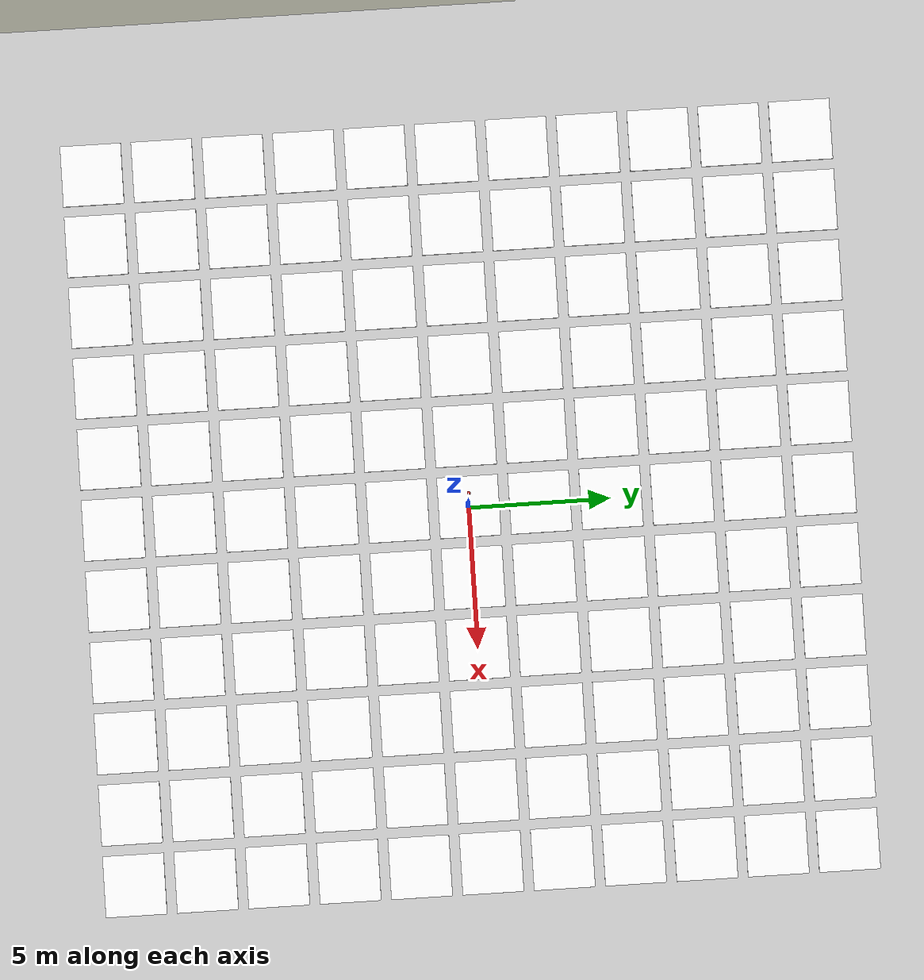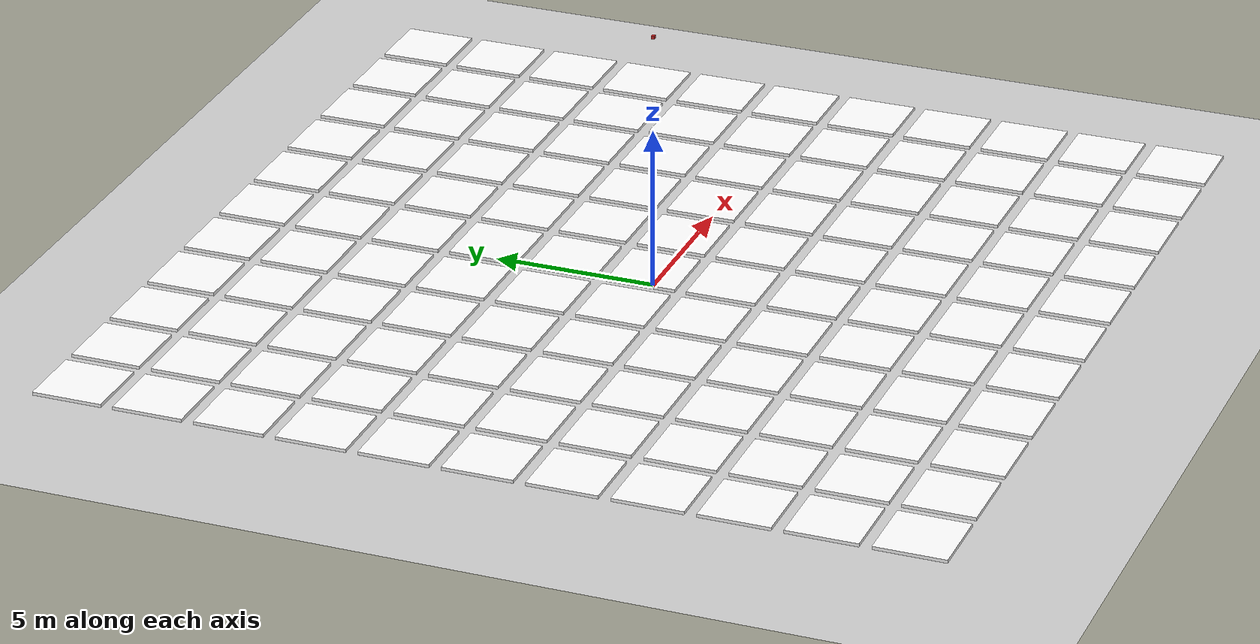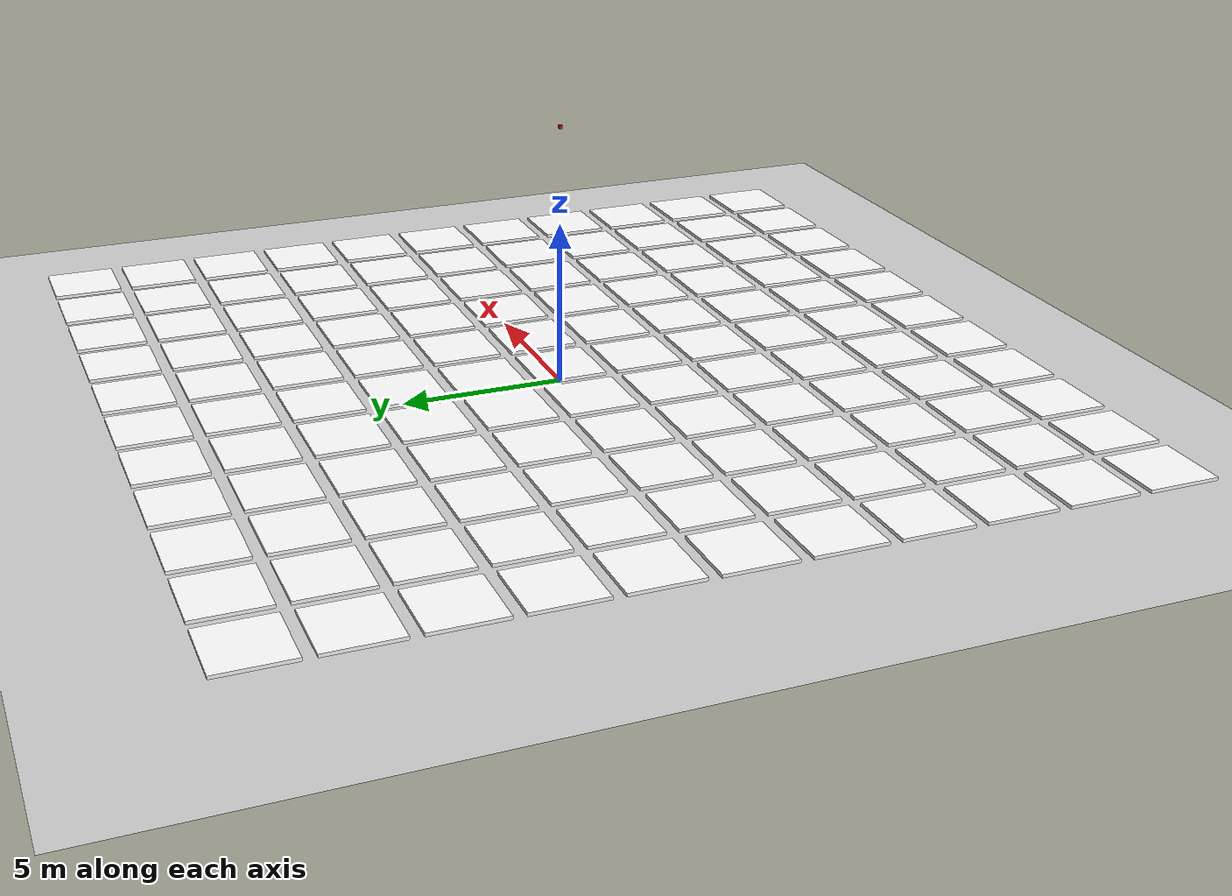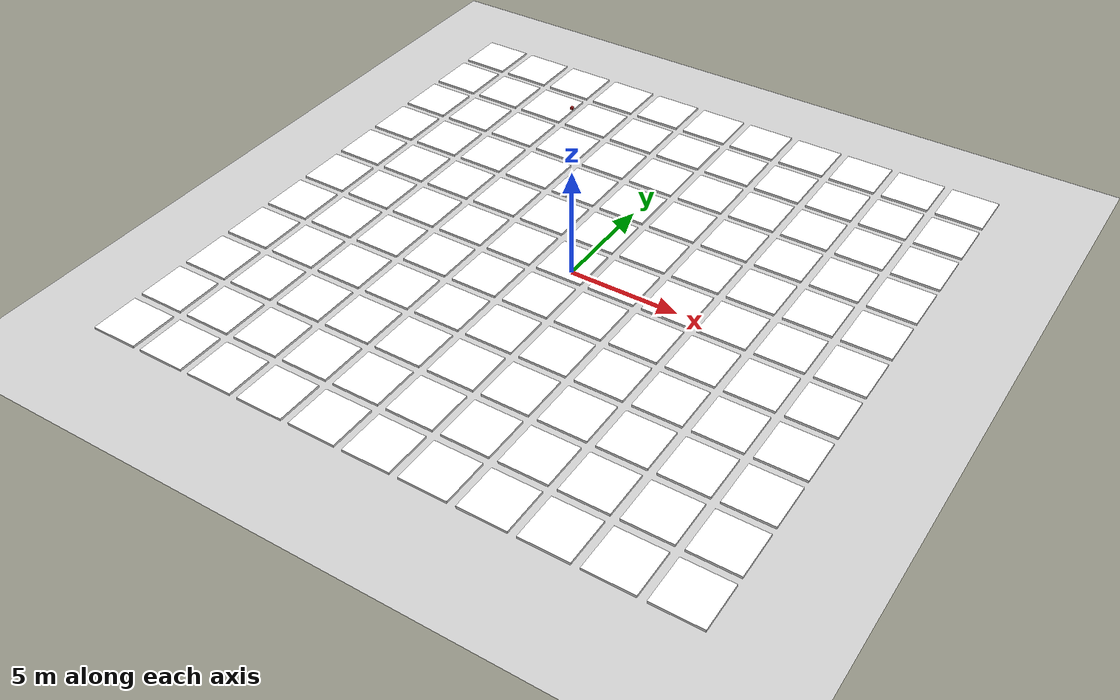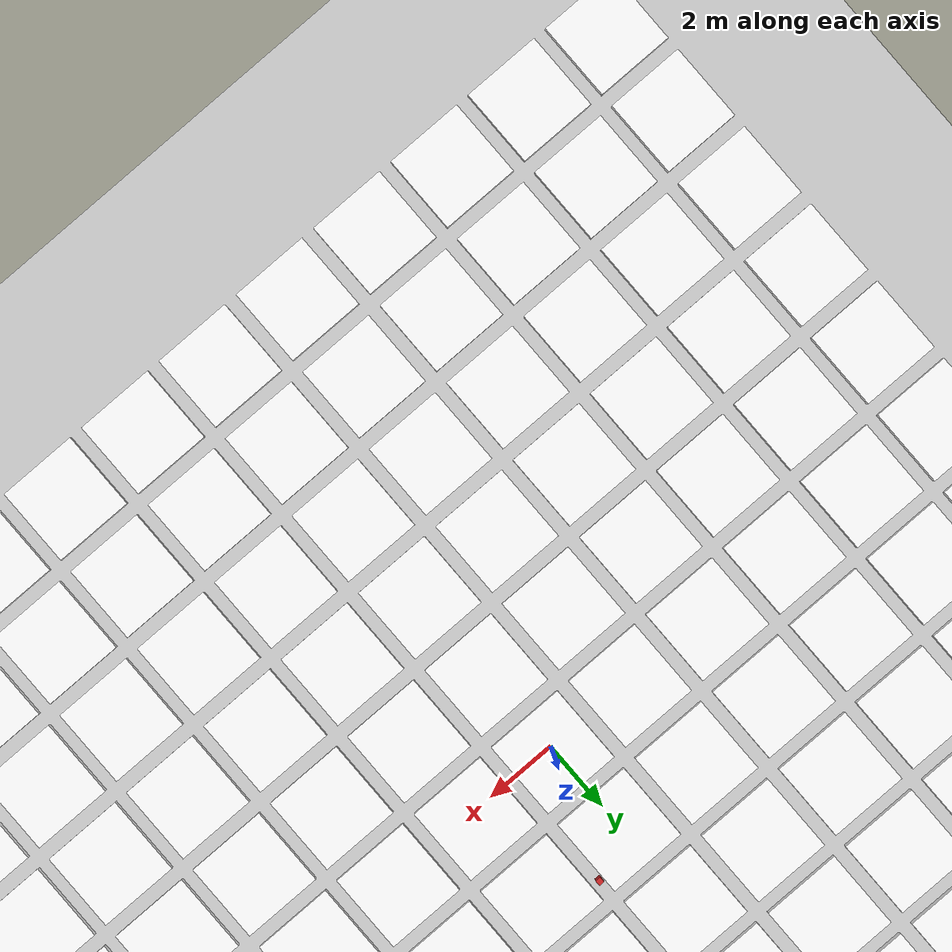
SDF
<sdf version="1.7">
 <world name="default">
  <light name="sun" type="directional">
   <pose>0 0 10 0 -0 0</pose>
   <diffuse>0.8 0.8 0.8 1</diffuse>
   <specular>0.2 0.2 0.2 1</specular>
   <attenuation>
    <range>1000</range>
    <constant>0.9</constant>
    <linear>0.01</linear>
    <quadratic>0.001</quadratic>
   </attenuation>
   <direction>-0.5 0.1 -0.9</direction>
   <spot><inner_angle>0</inner_angle><outer_angle>0</outer_angle><falloff>0</falloff></spot>
  </light>
  <model name="ground_plane">
   <static>1</static>
   <link name="link">
    <collision name="collision">
     <geometry><plane><normal>0 0 1</normal><size>100 100</size></plane></geometry>
     <surface>
      <contact><collide_bitmask>65535</collide_bitmask></contact>
      <friction><ode><mu>100</mu><mu2>50</mu2></ode></friction>
     </surface>
    </collision>
    <visual name="visual">
     <cast_shadows>0</cast_shadows>
     <geometry><plane><normal>0 0 1</normal><size>100 100</size></plane></geometry>
     <material>
      <script><uri>file://media/materials/scripts/gazebo.material</uri><name>Gazebo/Grey</name></script>
     </material>
    </visual>
   </link>
  </model>
  <gravity>0 0 -9.8</gravity>
  <magnetic_field>6e-06 2.3e-05 -4.2e-05</magnetic_field>
  <atmosphere type="adiabatic"/>
  <physics type="ode">
   <max_step_size>0.001</max_step_size>
   <real_time_factor>1</real_time_factor>
   <real_time_update_rate>1000</real_time_update_rate>
  </physics>
  <scene><ambient>0.4 0.4 0.4 1</ambient><background>0.7 0.7 0.7 1</background><shadows>1</shadows></scene>
  <audio><device>default</device></audio>
  <spherical_coordinates>
   <surface_model>EARTH_WGS84</surface_model>
   <latitude_deg>0</latitude_deg>
   <longitude_deg>0</longitude_deg>
   <elevation>0</elevation>
   <heading_deg>0</heading_deg>
  </spherical_coordinates>
  <model name="top_view_fuel_cluster_0_0">
   <link name="link">
    <inertial>
     <mass>0.489843</mass>
     <inertia>
      <ixx>0.0410659</ixx>
      <ixy>0</ixy>
      <ixz>0</ixz>
      <iyy>0.0410658</iyy>
      <iyz>0</iyz>
      <izz>0.0816405</izz>
     </inertia>
    </inertial>
    <visual name="visual">
     <geometry><box><size>2.14 2.14 0.099999</size></box></geometry>
     <material>
      <script>
       <uri>model://top_view_fuel_cluster/materials/scripts</uri>
       <uri>model://top_view_fuel_cluster/materials/textures</uri>
       <name>snf/Diffuse</name>
      </script>
      <shader type="pixel"><normal_map>__default__</normal_map></shader>
      <ambient>0.3 0.3 0.3 1</ambient>
      <diffuse>1 1 1 1</diffuse>
      <specular>0.01 0.01 0.01 1</specular>
      <emissive>0 0 0 1</emissive>
     </material>
    </visual>
    <collision name="collision">
     <geometry><box><size>2.14 2.14 0.100001</size></box></geometry>
     <surface>
      <friction>
       <ode><mu>1</mu><mu2>1</mu2><fdir1>0 0 0</fdir1><slip1>0</slip1><slip2>0</slip2></ode>
       <torsional>
        <coefficient>1</coefficient>
        <patch_radius>0</patch_radius>
        <surface_radius>0</surface_radius>
        <use_patch_radius>1</use_patch_radius>
        <ode><slip>0</slip></ode>
       </torsional>
      </friction>
      <bounce><restitution_coefficient>0</restitution_coefficient><threshold>1e+06</threshold></bounce>
      <contact>
       <collide_without_contact>0</collide_without_contact>
       <collide_without_contact_bitmask>1</collide_without_contact_bitmask>
       <collide_bitmask>1</collide_bitmask>
       <ode>
        <soft_cfm>0</soft_cfm>
        <soft_erp>0.2</soft_erp>
        <kp>1e+13</kp>
        <kd>1</kd>
        <max_vel>0.01</max_vel>
        <min_depth>0</min_depth>
       </ode>
       <bullet>
        <split_impulse>1</split_impulse>
        <split_impulse_penetration_threshold>-0.01</split_impulse_penetration_threshold>
        <soft_cfm>0</soft_cfm>
        <soft_erp>0.2</soft_erp>
        <kp>1e+13</kp>
        <kd>1</kd>
       </bullet>
      </contact>
     </surface>
    </collision>
   </link>
   <static>0</static>
   <pose>0 0 0.5 0 0 0</pose>
  </model>
  <model name="top_view_fuel_cluster_0_1">
   <link name="link">
    <inertial>
     <mass>0.489843</mass>
     <inertia>
      <ixx>0.0410659</ixx>
      <ixy>0</ixy>
      <ixz>0</ixz>
      <iyy>0.0410658</iyy>
      <iyz>0</iyz>
      <izz>0.0816405</izz>
     </inertia>
    </inertial>
    <visual name="visual">
     <geometry><box><size>2.14 2.14 0.099999</size></box></geometry>
     <material>
      <script>
       <uri>model://top_view_fuel_cluster/materials/scripts</uri>
       <uri>model://top_view_fuel_cluster/materials/textures</uri>
       <name>snf/Diffuse</name>
      </script>
      <shader type="pixel"><normal_map>__default__</normal_map></shader>
      <ambient>0.3 0.3 0.3 1</ambient>
      <diffuse>1 1 1 1</diffuse>
      <specular>0.01 0.01 0.01 1</specular>
      <emissive>0 0 0 1</emissive>
     </material>
    </visual>
    <collision name="collision">
     <geometry><box><size>2.14 2.14 0.100001</size></box></geometry>
     <surface>
      <friction>
       <ode><mu>1</mu><mu2>1</mu2><fdir1>0 0 0</fdir1><slip1>0</slip1><slip2>0</slip2></ode>
       <torsional>
        <coefficient>1</coefficient>
        <patch_radius>0</patch_radius>
        <surface_radius>0</surface_radius>
        <use_patch_radius>1</use_patch_radius>
        <ode><slip>0</slip></ode>
       </torsional>
      </friction>
      <bounce><restitution_coefficient>0</restitution_coefficient><threshold>1e+06</threshold></bounce>
      <contact>
       <collide_without_contact>0</collide_without_contact>
       <collide_without_contact_bitmask>1</collide_without_contact_bitmask>
       <collide_bitmask>1</collide_bitmask>
       <ode>
        <soft_cfm>0</soft_cfm>
        <soft_erp>0.2</soft_erp>
        <kp>1e+13</kp>
        <kd>1</kd>
        <max_vel>0.01</max_vel>
        <min_depth>0</min_depth>
       </ode>
       <bullet>
        <split_impulse>1</split_impulse>
        <split_impulse_penetration_threshold>-0.01</split_impulse_penetration_threshold>
        <soft_cfm>0</soft_cfm>
        <soft_erp>0.2</soft_erp>
        <kp>1e+13</kp>
        <kd>1</kd>
       </bullet>
      </contact>
     </surface>
    </collision>
   </link>
   <static>0</static>
   <pose>-12.5 0 0.5 0 -0 0</pose>
  </model>
  <model name="top_view_fuel_cluster_0_2">
   <link name="link">
    <inertial>
     <mass>0.489843</mass>
     <inertia>
      <ixx>0.0410659</ixx>
      <ixy>0</ixy>
      <ixz>0</ixz>
      <iyy>0.0410658</iyy>
      <iyz>0</iyz>
      <izz>0.0816405</izz>
     </inertia>
    </inertial>
    <visual name="visual">
     <geometry><box><size>2.14 2.14 0.099999</size></box></geometry>
     <material>
      <script>
       <uri>model://top_view_fuel_cluster/materials/scripts</uri>
       <uri>model://top_view_fuel_cluster/materials/textures</uri>
       <name>snf/Diffuse</name>
      </script>
      <shader type="pixel"><normal_map>__default__</normal_map></shader>
      <ambient>0.3 0.3 0.3 1</ambient>
      <diffuse>1 1 1 1</diffuse>
      <specular>0.01 0.01 0.01 1</specular>
      <emissive>0 0 0 1</emissive>
     </material>
    </visual>
    <collision name="collision">
     <geometry><box><size>2.14 2.14 0.100001</size></box></geometry>
     <surface>
      <friction>
       <ode><mu>1</mu><mu2>1</mu2><fdir1>0 0 0</fdir1><slip1>0</slip1><slip2>0</slip2></ode>
       <torsional>
        <coefficient>1</coefficient>
        <patch_radius>0</patch_radius>
        <surface_radius>0</surface_radius>
        <use_patch_radius>1</use_patch_radius>
        <ode><slip>0</slip></ode>
       </torsional>
      </friction>
      <bounce><restitution_coefficient>0</restitution_coefficient><threshold>1e+06</threshold></bounce>
      <contact>
       <collide_without_contact>0</collide_without_contact>
       <collide_without_contact_bitmask>1</collide_without_contact_bitmask>
       <collide_bitmask>1</collide_bitmask>
       <ode>
        <soft_cfm>0</soft_cfm>
        <soft_erp>0.2</soft_erp>
        <kp>1e+13</kp>
        <kd>1</kd>
        <max_vel>0.01</max_vel>
        <min_depth>0</min_depth>
       </ode>
       <bullet>
        <split_impulse>1</split_impulse>
        <split_impulse_penetration_threshold>-0.01</split_impulse_penetration_threshold>
        <soft_cfm>0</soft_cfm>
        <soft_erp>0.2</soft_erp>
        <kp>1e+13</kp>
        <kd>1</kd>
       </bullet>
      </contact>
     </surface>
    </collision>
   </link>
   <static>0</static>
   <pose>-10 0 0.5 0 -0 0</pose>
  </model>
  <model name="top_view_fuel_cluster_0_3">
   <link name="link">
    <inertial>
     <mass>0.489843</mass>
     <inertia>
      <ixx>0.0410659</ixx>
      <ixy>0</ixy>
      <ixz>0</ixz>
      <iyy>0.0410658</iyy>
      <iyz>0</iyz>
      <izz>0.0816405</izz>
     </inertia>
    </inertial>
    <visual name="visual">
     <geometry><box><size>2.14 2.14 0.099999</size></box></geometry>
     <material>
      <script>
       <uri>model://top_view_fuel_cluster/materials/scripts</uri>
       <uri>model://top_view_fuel_cluster/materials/textures</uri>
       <name>snf/Diffuse</name>
      </script>
      <shader type="pixel"><normal_map>__default__</normal_map></shader>
      <ambient>0.3 0.3 0.3 1</ambient>
      <diffuse>1 1 1 1</diffuse>
      <specular>0.01 0.01 0.01 1</specular>
      <emissive>0 0 0 1</emissive>
     </material>
    </visual>
    <collision name="collision">
     <geometry><box><size>2.14 2.14 0.100001</size></box></geometry>
     <surface>
      <friction>
       <ode><mu>1</mu><mu2>1</mu2><fdir1>0 0 0</fdir1><slip1>0</slip1><slip2>0</slip2></ode>
       <torsional>
        <coefficient>1</coefficient>
        <patch_radius>0</patch_radius>
        <surface_radius>0</surface_radius>
        <use_patch_radius>1</use_patch_radius>
        <ode><slip>0</slip></ode>
       </torsional>
      </friction>
      <bounce><restitution_coefficient>0</restitution_coefficient><threshold>1e+06</threshold></bounce>
      <contact>
       <collide_without_contact>0</collide_without_contact>
       <collide_without_contact_bitmask>1</collide_without_contact_bitmask>
       <collide_bitmask>1</collide_bitmask>
       <ode>
        <soft_cfm>0</soft_cfm>
        <soft_erp>0.2</soft_erp>
        <kp>1e+13</kp>
        <kd>1</kd>
        <max_vel>0.01</max_vel>
        <min_depth>0</min_depth>
       </ode>
       <bullet>
        <split_impulse>1</split_impulse>
        <split_impulse_penetration_threshold>-0.01</split_impulse_penetration_threshold>
        <soft_cfm>0</soft_cfm>
        <soft_erp>0.2</soft_erp>
        <kp>1e+13</kp>
        <kd>1</kd>
       </bullet>
      </contact>
     </surface>
    </collision>
   </link>
   <static>0</static>
   <pose>-7.5 0 0.5 0 -0 0</pose>
  </model>
  <model name="top_view_fuel_cluster_0_4">
   <link name="link">
    <inertial>
     <mass>0.489843</mass>
     <inertia>
      <ixx>0.0410659</ixx>
      <ixy>0</ixy>
      <ixz>0</ixz>
      <iyy>0.0410658</iyy>
      <iyz>0</iyz>
      <izz>0.0816405</izz>
     </inertia>
    </inertial>
    <visual name="visual">
     <geometry><box><size>2.14 2.14 0.099999</size></box></geometry>
     <material>
      <script>
       <uri>model://top_view_fuel_cluster/materials/scripts</uri>
       <uri>model://top_view_fuel_cluster/materials/textures</uri>
       <name>snf/Diffuse</name>
      </script>
      <shader type="pixel"><normal_map>__default__</normal_map></shader>
      <ambient>0.3 0.3 0.3 1</ambient>
      <diffuse>1 1 1 1</diffuse>
      <specular>0.01 0.01 0.01 1</specular>
      <emissive>0 0 0 1</emissive>
     </material>
    </visual>
    <collision name="collision">
     <geometry><box><size>2.14 2.14 0.100001</size></box></geometry>
     <surface>
      <friction>
       <ode><mu>1</mu><mu2>1</mu2><fdir1>0 0 0</fdir1><slip1>0</slip1><slip2>0</slip2></ode>
       <torsional>
        <coefficient>1</coefficient>
        <patch_radius>0</patch_radius>
        <surface_radius>0</surface_radius>
        <use_patch_radius>1</use_patch_radius>
        <ode><slip>0</slip></ode>
       </torsional>
      </friction>
      <bounce><restitution_coefficient>0</restitution_coefficient><threshold>1e+06</threshold></bounce>
      <contact>
       <collide_without_contact>0</collide_without_contact>
       <collide_without_contact_bitmask>1</collide_without_contact_bitmask>
       <collide_bitmask>1</collide_bitmask>
       <ode>
        <soft_cfm>0</soft_cfm>
        <soft_erp>0.2</soft_erp>
        <kp>1e+13</kp>
        <kd>1</kd>
        <max_vel>0.01</max_vel>
        <min_depth>0</min_depth>
       </ode>
       <bullet>
        <split_impulse>1</split_impulse>
        <split_impulse_penetration_threshold>-0.01</split_impulse_penetration_threshold>
        <soft_cfm>0</soft_cfm>
        <soft_erp>0.2</soft_erp>
        <kp>1e+13</kp>
        <kd>1</kd>
       </bullet>
      </contact>
     </surface>
    </collision>
   </link>
   <static>0</static>
   <pose>-5 0 0.5 0 -0 0</pose>
  </model>
  <model name="top_view_fuel_cluster_0_5">
   <link name="link">
    <inertial>
     <mass>0.489843</mass>
     <inertia>
      <ixx>0.0410659</ixx>
      <ixy>0</ixy>
      <ixz>0</ixz>
      <iyy>0.0410658</iyy>
      <iyz>0</iyz>
      <izz>0.0816405</izz>
     </inertia>
    </inertial>
    <visual name="visual">
     <geometry><box><size>2.14 2.14 0.099999</size></box></geometry>
     <material>
      <script>
       <uri>model://top_view_fuel_cluster/materials/scripts</uri>
       <uri>model://top_view_fuel_cluster/materials/textures</uri>
       <name>snf/Diffuse</name>
      </script>
      <shader type="pixel"><normal_map>__default__</normal_map></shader>
      <ambient>0.3 0.3 0.3 1</ambient>
      <diffuse>1 1 1 1</diffuse>
      <specular>0.01 0.01 0.01 1</specular>
      <emissive>0 0 0 1</emissive>
     </material>
    </visual>
    <collision name="collision">
     <geometry><box><size>2.14 2.14 0.100001</size></box></geometry>
     <surface>
      <friction>
       <ode><mu>1</mu><mu2>1</mu2><fdir1>0 0 0</fdir1><slip1>0</slip1><slip2>0</slip2></ode>
       <torsional>
        <coefficient>1</coefficient>
        <patch_radius>0</patch_radius>
        <surface_radius>0</surface_radius>
        <use_patch_radius>1</use_patch_radius>
        <ode><slip>0</slip></ode>
       </torsional>
      </friction>
      <bounce><restitution_coefficient>0</restitution_coefficient><threshold>1e+06</threshold></bounce>
      <contact>
       <collide_without_contact>0</collide_without_contact>
       <collide_without_contact_bitmask>1</collide_without_contact_bitmask>
       <collide_bitmask>1</collide_bitmask>
       <ode>
        <soft_cfm>0</soft_cfm>
        <soft_erp>0.2</soft_erp>
        <kp>1e+13</kp>
        <kd>1</kd>
        <max_vel>0.01</max_vel>
        <min_depth>0</min_depth>
       </ode>
       <bullet>
        <split_impulse>1</split_impulse>
        <split_impulse_penetration_threshold>-0.01</split_impulse_penetration_threshold>
        <soft_cfm>0</soft_cfm>
        <soft_erp>0.2</soft_erp>
        <kp>1e+13</kp>
        <kd>1</kd>
       </bullet>
      </contact>
     </surface>
    </collision>
   </link>
   <static>0</static>
   <pose>-2.5 0 0.5 0 -0 0</pose>
  </model>
  <model name="top_view_fuel_cluster_0_6">
   <link name="link">
    <inertial>
     <mass>0.489843</mass>
     <inertia>
      <ixx>0.0410659</ixx>
      <ixy>0</ixy>
      <ixz>0</ixz>
      <iyy>0.0410658</iyy>
      <iyz>0</iyz>
      <izz>0.0816405</izz>
     </inertia>
    </inertial>
    <visual name="visual">
     <geometry><box><size>2.14 2.14 0.099999</size></box></geometry>
     <material>
      <script>
       <uri>model://top_view_fuel_cluster/materials/scripts</uri>
       <uri>model://top_view_fuel_cluster/materials/textures</uri>
       <name>snf/Diffuse</name>
      </script>
      <shader type="pixel"><normal_map>__default__</normal_map></shader>
      <ambient>0.3 0.3 0.3 1</ambient>
      <diffuse>1 1 1 1</diffuse>
      <specular>0.01 0.01 0.01 1</specular>
      <emissive>0 0 0 1</emissive>
     </material>
    </visual>
    <collision name="collision">
     <geometry><box><size>2.14 2.14 0.100001</size></box></geometry>
     <surface>
      <friction>
       <ode><mu>1</mu><mu2>1</mu2><fdir1>0 0 0</fdir1><slip1>0</slip1><slip2>0</slip2></ode>
       <torsional>
        <coefficient>1</coefficient>
        <patch_radius>0</patch_radius>
        <surface_radius>0</surface_radius>
        <use_patch_radius>1</use_patch_radius>
        <ode><slip>0</slip></ode>
       </torsional>
      </friction>
      <bounce><restitution_coefficient>0</restitution_coefficient><threshold>1e+06</threshold></bounce>
      <contact>
       <collide_without_contact>0</collide_without_contact>
       <collide_without_contact_bitmask>1</collide_without_contact_bitmask>
       <collide_bitmask>1</collide_bitmask>
       <ode>
        <soft_cfm>0</soft_cfm>
        <soft_erp>0.2</soft_erp>
        <kp>1e+13</kp>
        <kd>1</kd>
        <max_vel>0.01</max_vel>
        <min_depth>0</min_depth>
       </ode>
       <bullet>
        <split_impulse>1</split_impulse>
        <split_impulse_penetration_threshold>-0.01</split_impulse_penetration_threshold>
        <soft_cfm>0</soft_cfm>
        <soft_erp>0.2</soft_erp>
        <kp>1e+13</kp>
        <kd>1</kd>
       </bullet>
      </contact>
     </surface>
    </collision>
   </link>
   <static>0</static>
   <pose>2.5 0 0.5 0 -0 0</pose>
  </model>
  <model name="top_view_fuel_cluster_0_7">
   <link name="link">
    <inertial>
     <mass>0.489843</mass>
     <inertia>
      <ixx>0.0410659</ixx>
      <ixy>0</ixy>
      <ixz>0</ixz>
      <iyy>0.0410658</iyy>
      <iyz>0</iyz>
      <izz>0.0816405</izz>
     </inertia>
    </inertial>
    <visual name="visual">
     <geometry><box><size>2.14 2.14 0.099999</size></box></geometry>
     <material>
      <script>
       <uri>model://top_view_fuel_cluster/materials/scripts</uri>
       <uri>model://top_view_fuel_cluster/materials/textures</uri>
       <name>snf/Diffuse</name>
      </script>
      <shader type="pixel"><normal_map>__default__</normal_map></shader>
      <ambient>0.3 0.3 0.3 1</ambient>
      <diffuse>1 1 1 1</diffuse>
      <specular>0.01 0.01 0.01 1</specular>
      <emissive>0 0 0 1</emissive>
     </material>
    </visual>
    <collision name="collision">
     <geometry><box><size>2.14 2.14 0.100001</size></box></geometry>
     <surface>
      <friction>
       <ode><mu>1</mu><mu2>1</mu2><fdir1>0 0 0</fdir1><slip1>0</slip1><slip2>0</slip2></ode>
       <torsional>
        <coefficient>1</coefficient>
        <patch_radius>0</patch_radius>
        <surface_radius>0</surface_radius>
        <use_patch_radius>1</use_patch_radius>
        <ode><slip>0</slip></ode>
       </torsional>
      </friction>
      <bounce><restitution_coefficient>0</restitution_coefficient><threshold>1e+06</threshold></bounce>
      <contact>
       <collide_without_contact>0</collide_without_contact>
       <collide_without_contact_bitmask>1</collide_without_contact_bitmask>
       <collide_bitmask>1</collide_bitmask>
       <ode>
        <soft_cfm>0</soft_cfm>
        <soft_erp>0.2</soft_erp>
        <kp>1e+13</kp>
        <kd>1</kd>
        <max_vel>0.01</max_vel>
        <min_depth>0</min_depth>
       </ode>
       <bullet>
        <split_impulse>1</split_impulse>
        <split_impulse_penetration_threshold>-0.01</split_impulse_penetration_threshold>
        <soft_cfm>0</soft_cfm>
        <soft_erp>0.2</soft_erp>
        <kp>1e+13</kp>
        <kd>1</kd>
       </bullet>
      </contact>
     </surface>
    </collision>
   </link>
   <static>0</static>
   <pose>5 0 0.5 0 -0 0</pose>
  </model>
  <model name="top_view_fuel_cluster_0_8">
   <link name="link">
    <inertial>
     <mass>0.489843</mass>
     <inertia>
      <ixx>0.0410659</ixx>
      <ixy>0</ixy>
      <ixz>0</ixz>
      <iyy>0.0410658</iyy>
      <iyz>0</iyz>
      <izz>0.0816405</izz>
     </inertia>
    </inertial>
    <visual name="visual">
     <geometry><box><size>2.14 2.14 0.099999</size></box></geometry>
     <material>
      <script>
       <uri>model://top_view_fuel_cluster/materials/scripts</uri>
       <uri>model://top_view_fuel_cluster/materials/textures</uri>
       <name>snf/Diffuse</name>
      </script>
      <shader type="pixel"><normal_map>__default__</normal_map></shader>
      <ambient>0.3 0.3 0.3 1</ambient>
      <diffuse>1 1 1 1</diffuse>
      <specular>0.01 0.01 0.01 1</specular>
      <emissive>0 0 0 1</emissive>
     </material>
    </visual>
    <collision name="collision">
     <geometry><box><size>2.14 2.14 0.100001</size></box></geometry>
     <surface>
      <friction>
       <ode><mu>1</mu><mu2>1</mu2><fdir1>0 0 0</fdir1><slip1>0</slip1><slip2>0</slip2></ode>
       <torsional>
        <coefficient>1</coefficient>
        <patch_radius>0</patch_radius>
        <surface_radius>0</surface_radius>
        <use_patch_radius>1</use_patch_radius>
        <ode><slip>0</slip></ode>
       </torsional>
      </friction>
      <bounce><restitution_coefficient>0</restitution_coefficient><threshold>1e+06</threshold></bounce>
      <contact>
       <collide_without_contact>0</collide_without_contact>
       <collide_without_contact_bitmask>1</collide_without_contact_bitmask>
       <collide_bitmask>1</collide_bitmask>
       <ode>
        <soft_cfm>0</soft_cfm>
        <soft_erp>0.2</soft_erp>
        <kp>1e+13</kp>
        <kd>1</kd>
        <max_vel>0.01</max_vel>
        <min_depth>0</min_depth>
       </ode>
       <bullet>
        <split_impulse>1</split_impulse>
        <split_impulse_penetration_threshold>-0.01</split_impulse_penetration_threshold>
        <soft_cfm>0</soft_cfm>
        <soft_erp>0.2</soft_erp>
        <kp>1e+13</kp>
        <kd>1</kd>
       </bullet>
      </contact>
     </surface>
    </collision>
   </link>
   <static>0</static>
   <pose>7.5 0 0.5 0 -0 0</pose>
  </model>
  <model name="top_view_fuel_cluster_0_9">
   <link name="link">
    <inertial>
     <mass>0.489843</mass>
     <inertia>
      <ixx>0.0410659</ixx>
      <ixy>0</ixy>
      <ixz>0</ixz>
      <iyy>0.0410658</iyy>
      <iyz>0</iyz>
      <izz>0.0816405</izz>
     </inertia>
    </inertial>
    <visual name="visual">
     <geometry><box><size>2.14 2.14 0.099999</size></box></geometry>
     <material>
      <script>
       <uri>model://top_view_fuel_cluster/materials/scripts</uri>
       <uri>model://top_view_fuel_cluster/materials/textures</uri>
       <name>snf/Diffuse</name>
      </script>
      <shader type="pixel"><normal_map>__default__</normal_map></shader>
      <ambient>0.3 0.3 0.3 1</ambient>
      <diffuse>1 1 1 1</diffuse>
      <specular>0.01 0.01 0.01 1</specular>
      <emissive>0 0 0 1</emissive>
     </material>
    </visual>
    <collision name="collision">
     <geometry><box><size>2.14 2.14 0.100001</size></box></geometry>
     <surface>
      <friction>
       <ode><mu>1</mu><mu2>1</mu2><fdir1>0 0 0</fdir1><slip1>0</slip1><slip2>0</slip2></ode>
       <torsional>
        <coefficient>1</coefficient>
        <patch_radius>0</patch_radius>
        <surface_radius>0</surface_radius>
        <use_patch_radius>1</use_patch_radius>
        <ode><slip>0</slip></ode>
       </torsional>
      </friction>
      <bounce><restitution_coefficient>0</restitution_coefficient><threshold>1e+06</threshold></bounce>
      <contact>
       <collide_without_contact>0</collide_without_contact>
       <collide_without_contact_bitmask>1</collide_without_contact_bitmask>
       <collide_bitmask>1</collide_bitmask>
       <ode>
        <soft_cfm>0</soft_cfm>
        <soft_erp>0.2</soft_erp>
        <kp>1e+13</kp>
        <kd>1</kd>
        <max_vel>0.01</max_vel>
        <min_depth>0</min_depth>
       </ode>
       <bullet>
        <split_impulse>1</split_impulse>
        <split_impulse_penetration_threshold>-0.01</split_impulse_penetration_threshold>
        <soft_cfm>0</soft_cfm>
        <soft_erp>0.2</soft_erp>
        <kp>1e+13</kp>
        <kd>1</kd>
       </bullet>
      </contact>
     </surface>
    </collision>
   </link>
   <static>0</static>
   <pose>10 0 0.5 0 -0 0</pose>
  </model>
  <model name="top_view_fuel_cluster_0_10">
   <link name="link">
    <inertial>
     <mass>0.489843</mass>
     <inertia>
      <ixx>0.0410659</ixx>
      <ixy>0</ixy>
      <ixz>0</ixz>
      <iyy>0.0410658</iyy>
      <iyz>0</iyz>
      <izz>0.0816405</izz>
     </inertia>
    </inertial>
    <visual name="visual">
     <geometry><box><size>2.14 2.14 0.099999</size></box></geometry>
     <material>
      <script>
       <uri>model://top_view_fuel_cluster/materials/scripts</uri>
       <uri>model://top_view_fuel_cluster/materials/textures</uri>
       <name>snf/Diffuse</name>
      </script>
      <shader type="pixel"><normal_map>__default__</normal_map></shader>
      <ambient>0.3 0.3 0.3 1</ambient>
      <diffuse>1 1 1 1</diffuse>
      <specular>0.01 0.01 0.01 1</specular>
      <emissive>0 0 0 1</emissive>
     </material>
    </visual>
    <collision name="collision">
     <geometry><box><size>2.14 2.14 0.100001</size></box></geometry>
     <surface>
      <friction>
       <ode><mu>1</mu><mu2>1</mu2><fdir1>0 0 0</fdir1><slip1>0</slip1><slip2>0</slip2></ode>
       <torsional>
        <coefficient>1</coefficient>
        <patch_radius>0</patch_radius>
        <surface_radius>0</surface_radius>
        <use_patch_radius>1</use_patch_radius>
        <ode><slip>0</slip></ode>
       </torsional>
      </friction>
      <bounce><restitution_coefficient>0</restitution_coefficient><threshold>1e+06</threshold></bounce>
      <contact>
       <collide_without_contact>0</collide_without_contact>
       <collide_without_contact_bitmask>1</collide_without_contact_bitmask>
       <collide_bitmask>1</collide_bitmask>
       <ode>
        <soft_cfm>0</soft_cfm>
        <soft_erp>0.2</soft_erp>
        <kp>1e+13</kp>
        <kd>1</kd>
        <max_vel>0.01</max_vel>
        <min_depth>0</min_depth>
       </ode>
       <bullet>
        <split_impulse>1</split_impulse>
        <split_impulse_penetration_threshold>-0.01</split_impulse_penetration_threshold>
        <soft_cfm>0</soft_cfm>
        <soft_erp>0.2</soft_erp>
        <kp>1e+13</kp>
        <kd>1</kd>
       </bullet>
      </contact>
     </surface>
    </collision>
   </link>
   <static>0</static>
   <pose>12.5 0 0.5 0 -0 0</pose>
  </model>
  <model name="top_view_fuel_cluster_1_0">
   <link name="link">
    <inertial>
     <mass>0.489843</mass>
     <inertia>
      <ixx>0.0410659</ixx>
      <ixy>0</ixy>
      <ixz>0</ixz>
      <iyy>0.0410658</iyy>
      <iyz>0</iyz>
      <izz>0.0816405</izz>
     </inertia>
    </inertial>
    <visual name="visual">
     <geometry><box><size>2.14 2.14 0.099999</size></box></geometry>
     <material>
      <script>
       <uri>model://top_view_fuel_cluster/materials/scripts</uri>
       <uri>model://top_view_fuel_cluster/materials/textures</uri>
       <name>snf/Diffuse</name>
      </script>
      <shader type="pixel"><normal_map>__default__</normal_map></shader>
      <ambient>0.3 0.3 0.3 1</ambient>
      <diffuse>1 1 1 1</diffuse>
      <specular>0.01 0.01 0.01 1</specular>
      <emissive>0 0 0 1</emissive>
     </material>
    </visual>
    <collision name="collision">
     <geometry><box><size>2.14 2.14 0.100001</size></box></geometry>
     <surface>
      <friction>
       <ode><mu>1</mu><mu2>1</mu2><fdir1>0 0 0</fdir1><slip1>0</slip1><slip2>0</slip2></ode>
       <torsional>
        <coefficient>1</coefficient>
        <patch_radius>0</patch_radius>
        <surface_radius>0</surface_radius>
        <use_patch_radius>1</use_patch_radius>
        <ode><slip>0</slip></ode>
       </torsional>
      </friction>
      <bounce><restitution_coefficient>0</restitution_coefficient><threshold>1e+06</threshold></bounce>
      <contact>
       <collide_without_contact>0</collide_without_contact>
       <collide_without_contact_bitmask>1</collide_without_contact_bitmask>
       <collide_bitmask>1</collide_bitmask>
       <ode>
        <soft_cfm>0</soft_cfm>
        <soft_erp>0.2</soft_erp>
        <kp>1e+13</kp>
        <kd>1</kd>
        <max_vel>0.01</max_vel>
        <min_depth>0</min_depth>
       </ode>
       <bullet>
        <split_impulse>1</split_impulse>
        <split_impulse_penetration_threshold>-0.01</split_impulse_penetration_threshold>
        <soft_cfm>0</soft_cfm>
        <soft_erp>0.2</soft_erp>
        <kp>1e+13</kp>
        <kd>1</kd>
       </bullet>
      </contact>
     </surface>
    </collision>
   </link>
   <static>0</static>
   <pose>0 -12.5 0.5 0 0 0</pose>
  </model>
  <model name="top_view_fuel_cluster_1_1">
   <link name="link">
    <inertial>
     <mass>0.489843</mass>
     <inertia>
      <ixx>0.0410659</ixx>
      <ixy>0</ixy>
      <ixz>0</ixz>
      <iyy>0.0410658</iyy>
      <iyz>0</iyz>
      <izz>0.0816405</izz>
     </inertia>
    </inertial>
    <visual name="visual">
     <geometry><box><size>2.14 2.14 0.099999</size></box></geometry>
     <material>
      <script>
       <uri>model://top_view_fuel_cluster/materials/scripts</uri>
       <uri>model://top_view_fuel_cluster/materials/textures</uri>
       <name>snf/Diffuse</name>
      </script>
      <shader type="pixel"><normal_map>__default__</normal_map></shader>
      <ambient>0.3 0.3 0.3 1</ambient>
      <diffuse>1 1 1 1</diffuse>
      <specular>0.01 0.01 0.01 1</specular>
      <emissive>0 0 0 1</emissive>
     </material>
    </visual>
    <collision name="collision">
     <geometry><box><size>2.14 2.14 0.100001</size></box></geometry>
     <surface>
      <friction>
       <ode><mu>1</mu><mu2>1</mu2><fdir1>0 0 0</fdir1><slip1>0</slip1><slip2>0</slip2></ode>
       <torsional>
        <coefficient>1</coefficient>
        <patch_radius>0</patch_radius>
        <surface_radius>0</surface_radius>
        <use_patch_radius>1</use_patch_radius>
        <ode><slip>0</slip></ode>
       </torsional>
      </friction>
      <bounce><restitution_coefficient>0</restitution_coefficient><threshold>1e+06</threshold></bounce>
      <contact>
       <collide_without_contact>0</collide_without_contact>
       <collide_without_contact_bitmask>1</collide_without_contact_bitmask>
       <collide_bitmask>1</collide_bitmask>
       <ode>
        <soft_cfm>0</soft_cfm>
        <soft_erp>0.2</soft_erp>
        <kp>1e+13</kp>
        <kd>1</kd>
        <max_vel>0.01</max_vel>
        <min_depth>0</min_depth>
       </ode>
       <bullet>
        <split_impulse>1</split_impulse>
        <split_impulse_penetration_threshold>-0.01</split_impulse_penetration_threshold>
        <soft_cfm>0</soft_cfm>
        <soft_erp>0.2</soft_erp>
        <kp>1e+13</kp>
        <kd>1</kd>
       </bullet>
      </contact>
     </surface>
    </collision>
   </link>
   <static>0</static>
   <pose>-12.5 -12.5 0.5 0 -0 0</pose>
  </model>
  <model name="top_view_fuel_cluster_1_2">
   <link name="link">
    <inertial>
     <mass>0.489843</mass>
     <inertia>
      <ixx>0.0410659</ixx>
      <ixy>0</ixy>
      <ixz>0</ixz>
      <iyy>0.0410658</iyy>
      <iyz>0</iyz>
      <izz>0.0816405</izz>
     </inertia>
    </inertial>
    <visual name="visual">
     <geometry><box><size>2.14 2.14 0.099999</size></box></geometry>
     <material>
      <script>
       <uri>model://top_view_fuel_cluster/materials/scripts</uri>
       <uri>model://top_view_fuel_cluster/materials/textures</uri>
       <name>snf/Diffuse</name>
      </script>
      <shader type="pixel"><normal_map>__default__</normal_map></shader>
      <ambient>0.3 0.3 0.3 1</ambient>
      <diffuse>1 1 1 1</diffuse>
      <specular>0.01 0.01 0.01 1</specular>
      <emissive>0 0 0 1</emissive>
     </material>
    </visual>
    <collision name="collision">
     <geometry><box><size>2.14 2.14 0.100001</size></box></geometry>
     <surface>
      <friction>
       <ode><mu>1</mu><mu2>1</mu2><fdir1>0 0 0</fdir1><slip1>0</slip1><slip2>0</slip2></ode>
       <torsional>
        <coefficient>1</coefficient>
        <patch_radius>0</patch_radius>
        <surface_radius>0</surface_radius>
        <use_patch_radius>1</use_patch_radius>
        <ode><slip>0</slip></ode>
       </torsional>
      </friction>
      <bounce><restitution_coefficient>0</restitution_coefficient><threshold>1e+06</threshold></bounce>
      <contact>
       <collide_without_contact>0</collide_without_contact>
       <collide_without_contact_bitmask>1</collide_without_contact_bitmask>
       <collide_bitmask>1</collide_bitmask>
       <ode>
        <soft_cfm>0</soft_cfm>
        <soft_erp>0.2</soft_erp>
        <kp>1e+13</kp>
        <kd>1</kd>
        <max_vel>0.01</max_vel>
        <min_depth>0</min_depth>
       </ode>
       <bullet>
        <split_impulse>1</split_impulse>
        <split_impulse_penetration_threshold>-0.01</split_impulse_penetration_threshold>
        <soft_cfm>0</soft_cfm>
        <soft_erp>0.2</soft_erp>
        <kp>1e+13</kp>
        <kd>1</kd>
       </bullet>
      </contact>
     </surface>
    </collision>
   </link>
   <static>0</static>
   <pose>-10 -12.5 0.5 0 -0 0</pose>
  </model>
  <model name="top_view_fuel_cluster_1_3">
   <link name="link">
    <inertial>
     <mass>0.489843</mass>
     <inertia>
      <ixx>0.0410659</ixx>
      <ixy>0</ixy>
      <ixz>0</ixz>
      <iyy>0.0410658</iyy>
      <iyz>0</iyz>
      <izz>0.0816405</izz>
     </inertia>
    </inertial>
    <visual name="visual">
     <geometry><box><size>2.14 2.14 0.099999</size></box></geometry>
     <material>
      <script>
       <uri>model://top_view_fuel_cluster/materials/scripts</uri>
       <uri>model://top_view_fuel_cluster/materials/textures</uri>
       <name>snf/Diffuse</name>
      </script>
      <shader type="pixel"><normal_map>__default__</normal_map></shader>
      <ambient>0.3 0.3 0.3 1</ambient>
      <diffuse>1 1 1 1</diffuse>
      <specular>0.01 0.01 0.01 1</specular>
      <emissive>0 0 0 1</emissive>
     </material>
    </visual>
    <collision name="collision">
     <geometry><box><size>2.14 2.14 0.100001</size></box></geometry>
     <surface>
      <friction>
       <ode><mu>1</mu><mu2>1</mu2><fdir1>0 0 0</fdir1><slip1>0</slip1><slip2>0</slip2></ode>
       <torsional>
        <coefficient>1</coefficient>
        <patch_radius>0</patch_radius>
        <surface_radius>0</surface_radius>
        <use_patch_radius>1</use_patch_radius>
        <ode><slip>0</slip></ode>
       </torsional>
      </friction>
      <bounce><restitution_coefficient>0</restitution_coefficient><threshold>1e+06</threshold></bounce>
      <contact>
       <collide_without_contact>0</collide_without_contact>
       <collide_without_contact_bitmask>1</collide_without_contact_bitmask>
       <collide_bitmask>1</collide_bitmask>
       <ode>
        <soft_cfm>0</soft_cfm>
        <soft_erp>0.2</soft_erp>
        <kp>1e+13</kp>
        <kd>1</kd>
        <max_vel>0.01</max_vel>
        <min_depth>0</min_depth>
       </ode>
       <bullet>
        <split_impulse>1</split_impulse>
        <split_impulse_penetration_threshold>-0.01</split_impulse_penetration_threshold>
        <soft_cfm>0</soft_cfm>
        <soft_erp>0.2</soft_erp>
        <kp>1e+13</kp>
        <kd>1</kd>
       </bullet>
      </contact>
     </surface>
    </collision>
   </link>
   <static>0</static>
   <pose>-7.5 -12.5 0.5 0 -0 0</pose>
  </model>
  <model name="top_view_fuel_cluster_1_4">
   <link name="link">
    <inertial>
     <mass>0.489843</mass>
     <inertia>
      <ixx>0.0410659</ixx>
      <ixy>0</ixy>
      <ixz>0</ixz>
      <iyy>0.0410658</iyy>
      <iyz>0</iyz>
      <izz>0.0816405</izz>
     </inertia>
    </inertial>
    <visual name="visual">
     <geometry><box><size>2.14 2.14 0.099999</size></box></geometry>
     <material>
      <script>
       <uri>model://top_view_fuel_cluster/materials/scripts</uri>
       <uri>model://top_view_fuel_cluster/materials/textures</uri>
       <name>snf/Diffuse</name>
      </script>
      <shader type="pixel"><normal_map>__default__</normal_map></shader>
      <ambient>0.3 0.3 0.3 1</ambient>
      <diffuse>1 1 1 1</diffuse>
      <specular>0.01 0.01 0.01 1</specular>
      <emissive>0 0 0 1</emissive>
     </material>
    </visual>
    <collision name="collision">
     <geometry><box><size>2.14 2.14 0.100001</size></box></geometry>
     <surface>
      <friction>
       <ode><mu>1</mu><mu2>1</mu2><fdir1>0 0 0</fdir1><slip1>0</slip1><slip2>0</slip2></ode>
       <torsional>
        <coefficient>1</coefficient>
        <patch_radius>0</patch_radius>
        <surface_radius>0</surface_radius>
        <use_patch_radius>1</use_patch_radius>
        <ode><slip>0</slip></ode>
       </torsional>
      </friction>
      <bounce><restitution_coefficient>0</restitution_coefficient><threshold>1e+06</threshold></bounce>
      <contact>
       <collide_without_contact>0</collide_without_contact>
       <collide_without_contact_bitmask>1</collide_without_contact_bitmask>
       <collide_bitmask>1</collide_bitmask>
       <ode>
        <soft_cfm>0</soft_cfm>
        <soft_erp>0.2</soft_erp>
        <kp>1e+13</kp>
        <kd>1</kd>
        <max_vel>0.01</max_vel>
        <min_depth>0</min_depth>
       </ode>
       <bullet>
        <split_impulse>1</split_impulse>
        <split_impulse_penetration_threshold>-0.01</split_impulse_penetration_threshold>
        <soft_cfm>0</soft_cfm>
        <soft_erp>0.2</soft_erp>
        <kp>1e+13</kp>
        <kd>1</kd>
       </bullet>
      </contact>
     </surface>
    </collision>
   </link>
   <static>0</static>
   <pose>-5 -12.5 0.5 0 -0 0</pose>
  </model>
  <model name="top_view_fuel_cluster_1_5">
   <link name="link">
    <inertial>
     <mass>0.489843</mass>
     <inertia>
      <ixx>0.0410659</ixx>
      <ixy>0</ixy>
      <ixz>0</ixz>
      <iyy>0.0410658</iyy>
      <iyz>0</iyz>
      <izz>0.0816405</izz>
     </inertia>
    </inertial>
    <visual name="visual">
     <geometry><box><size>2.14 2.14 0.099999</size></box></geometry>
     <material>
      <script>
       <uri>model://top_view_fuel_cluster/materials/scripts</uri>
       <uri>model://top_view_fuel_cluster/materials/textures</uri>
       <name>snf/Diffuse</name>
      </script>
      <shader type="pixel"><normal_map>__default__</normal_map></shader>
      <ambient>0.3 0.3 0.3 1</ambient>
      <diffuse>1 1 1 1</diffuse>
      <specular>0.01 0.01 0.01 1</specular>
      <emissive>0 0 0 1</emissive>
     </material>
    </visual>
    <collision name="collision">
     <geometry><box><size>2.14 2.14 0.100001</size></box></geometry>
     <surface>
      <friction>
       <ode><mu>1</mu><mu2>1</mu2><fdir1>0 0 0</fdir1><slip1>0</slip1><slip2>0</slip2></ode>
       <torsional>
        <coefficient>1</coefficient>
        <patch_radius>0</patch_radius>
        <surface_radius>0</surface_radius>
        <use_patch_radius>1</use_patch_radius>
        <ode><slip>0</slip></ode>
       </torsional>
      </friction>
      <bounce><restitution_coefficient>0</restitution_coefficient><threshold>1e+06</threshold></bounce>
      <contact>
       <collide_without_contact>0</collide_without_contact>
       <collide_without_contact_bitmask>1</collide_without_contact_bitmask>
       <collide_bitmask>1</collide_bitmask>
       <ode>
        <soft_cfm>0</soft_cfm>
        <soft_erp>0.2</soft_erp>
        <kp>1e+13</kp>
        <kd>1</kd>
        <max_vel>0.01</max_vel>
        <min_depth>0</min_depth>
       </ode>
       <bullet>
        <split_impulse>1</split_impulse>
        <split_impulse_penetration_threshold>-0.01</split_impulse_penetration_threshold>
        <soft_cfm>0</soft_cfm>
        <soft_erp>0.2</soft_erp>
        <kp>1e+13</kp>
        <kd>1</kd>
       </bullet>
      </contact>
     </surface>
    </collision>
   </link>
   <static>0</static>
   <pose>-2.5 -12.5 0.5 0 -0 0</pose>
  </model>
  <model name="top_view_fuel_cluster_1_6">
   <link name="link">
    <inertial>
     <mass>0.489843</mass>
     <inertia>
      <ixx>0.0410659</ixx>
      <ixy>0</ixy>
      <ixz>0</ixz>
      <iyy>0.0410658</iyy>
      <iyz>0</iyz>
      <izz>0.0816405</izz>
     </inertia>
    </inertial>
    <visual name="visual">
     <geometry><box><size>2.14 2.14 0.099999</size></box></geometry>
     <material>
      <script>
       <uri>model://top_view_fuel_cluster/materials/scripts</uri>
       <uri>model://top_view_fuel_cluster/materials/textures</uri>
       <name>snf/Diffuse</name>
      </script>
      <shader type="pixel"><normal_map>__default__</normal_map></shader>
      <ambient>0.3 0.3 0.3 1</ambient>
      <diffuse>1 1 1 1</diffuse>
      <specular>0.01 0.01 0.01 1</specular>
      <emissive>0 0 0 1</emissive>
     </material>
    </visual>
    <collision name="collision">
     <geometry><box><size>2.14 2.14 0.100001</size></box></geometry>
     <surface>
      <friction>
       <ode><mu>1</mu><mu2>1</mu2><fdir1>0 0 0</fdir1><slip1>0</slip1><slip2>0</slip2></ode>
       <torsional>
        <coefficient>1</coefficient>
        <patch_radius>0</patch_radius>
        <surface_radius>0</surface_radius>
        <use_patch_radius>1</use_patch_radius>
        <ode><slip>0</slip></ode>
       </torsional>
      </friction>
      <bounce><restitution_coefficient>0</restitution_coefficient><threshold>1e+06</threshold></bounce>
      <contact>
       <collide_without_contact>0</collide_without_contact>
       <collide_without_contact_bitmask>1</collide_without_contact_bitmask>
       <collide_bitmask>1</collide_bitmask>
       <ode>
        <soft_cfm>0</soft_cfm>
        <soft_erp>0.2</soft_erp>
        <kp>1e+13</kp>
        <kd>1</kd>
        <max_vel>0.01</max_vel>
        <min_depth>0</min_depth>
       </ode>
       <bullet>
        <split_impulse>1</split_impulse>
        <split_impulse_penetration_threshold>-0.01</split_impulse_penetration_threshold>
        <soft_cfm>0</soft_cfm>
        <soft_erp>0.2</soft_erp>
        <kp>1e+13</kp>
        <kd>1</kd>
       </bullet>
      </contact>
     </surface>
    </collision>
   </link>
   <static>0</static>
   <pose>2.5 -12.5 0.5 0 -0 0</pose>
  </model>
  <model name="top_view_fuel_cluster_1_7">
   <link name="link">
    <inertial>
     <mass>0.489843</mass>
     <inertia>
      <ixx>0.0410659</ixx>
      <ixy>0</ixy>
      <ixz>0</ixz>
      <iyy>0.0410658</iyy>
      <iyz>0</iyz>
      <izz>0.0816405</izz>
     </inertia>
    </inertial>
    <visual name="visual">
     <geometry><box><size>2.14 2.14 0.099999</size></box></geometry>
     <material>
      <script>
       <uri>model://top_view_fuel_cluster/materials/scripts</uri>
       <uri>model://top_view_fuel_cluster/materials/textures</uri>
       <name>snf/Diffuse</name>
      </script>
      <shader type="pixel"><normal_map>__default__</normal_map></shader>
      <ambient>0.3 0.3 0.3 1</ambient>
      <diffuse>1 1 1 1</diffuse>
      <specular>0.01 0.01 0.01 1</specular>
      <emissive>0 0 0 1</emissive>
     </material>
    </visual>
    <collision name="collision">
     <geometry><box><size>2.14 2.14 0.100001</size></box></geometry>
     <surface>
      <friction>
       <ode><mu>1</mu><mu2>1</mu2><fdir1>0 0 0</fdir1><slip1>0</slip1><slip2>0</slip2></ode>
       <torsional>
        <coefficient>1</coefficient>
        <patch_radius>0</patch_radius>
        <surface_radius>0</surface_radius>
        <use_patch_radius>1</use_patch_radius>
        <ode><slip>0</slip></ode>
       </torsional>
      </friction>
      <bounce><restitution_coefficient>0</restitution_coefficient><threshold>1e+06</threshold></bounce>
      <contact>
       <collide_without_contact>0</collide_without_contact>
       <collide_without_contact_bitmask>1</collide_without_contact_bitmask>
       <collide_bitmask>1</collide_bitmask>
       <ode>
        <soft_cfm>0</soft_cfm>
        <soft_erp>0.2</soft_erp>
        <kp>1e+13</kp>
        <kd>1</kd>
        <max_vel>0.01</max_vel>
        <min_depth>0</min_depth>
       </ode>
       <bullet>
        <split_impulse>1</split_impulse>
        <split_impulse_penetration_threshold>-0.01</split_impulse_penetration_threshold>
        <soft_cfm>0</soft_cfm>
        <soft_erp>0.2</soft_erp>
        <kp>1e+13</kp>
        <kd>1</kd>
       </bullet>
      </contact>
     </surface>
    </collision>
   </link>
   <static>0</static>
   <pose>5 -12.5 0.5 0 -0 0</pose>
  </model>
  <model name="top_view_fuel_cluster_1_8">
   <link name="link">
    <inertial>
     <mass>0.489843</mass>
     <inertia>
      <ixx>0.0410659</ixx>
      <ixy>0</ixy>
      <ixz>0</ixz>
      <iyy>0.0410658</iyy>
      <iyz>0</iyz>
      <izz>0.0816405</izz>
     </inertia>
    </inertial>
    <visual name="visual">
     <geometry><box><size>2.14 2.14 0.099999</size></box></geometry>
     <material>
      <script>
       <uri>model://top_view_fuel_cluster/materials/scripts</uri>
       <uri>model://top_view_fuel_cluster/materials/textures</uri>
       <name>snf/Diffuse</name>
      </script>
      <shader type="pixel"><normal_map>__default__</normal_map></shader>
      <ambient>0.3 0.3 0.3 1</ambient>
      <diffuse>1 1 1 1</diffuse>
      <specular>0.01 0.01 0.01 1</specular>
      <emissive>0 0 0 1</emissive>
     </material>
    </visual>
    <collision name="collision">
     <geometry><box><size>2.14 2.14 0.100001</size></box></geometry>
     <surface>
      <friction>
       <ode><mu>1</mu><mu2>1</mu2><fdir1>0 0 0</fdir1><slip1>0</slip1><slip2>0</slip2></ode>
       <torsional>
        <coefficient>1</coefficient>
        <patch_radius>0</patch_radius>
        <surface_radius>0</surface_radius>
        <use_patch_radius>1</use_patch_radius>
        <ode><slip>0</slip></ode>
       </torsional>
      </friction>
      <bounce><restitution_coefficient>0</restitution_coefficient><threshold>1e+06</threshold></bounce>
      <contact>
       <collide_without_contact>0</collide_without_contact>
       <collide_without_contact_bitmask>1</collide_without_contact_bitmask>
       <collide_bitmask>1</collide_bitmask>
       <ode>
        <soft_cfm>0</soft_cfm>
        <soft_erp>0.2</soft_erp>
        <kp>1e+13</kp>
        <kd>1</kd>
        <max_vel>0.01</max_vel>
        <min_depth>0</min_depth>
       </ode>
       <bullet>
        <split_impulse>1</split_impulse>
        <split_impulse_penetration_threshold>-0.01</split_impulse_penetration_threshold>
        <soft_cfm>0</soft_cfm>
        <soft_erp>0.2</soft_erp>
        <kp>1e+13</kp>
        <kd>1</kd>
       </bullet>
      </contact>
     </surface>
    </collision>
   </link>
   <static>0</static>
   <pose>7.5 -12.5 0.5 0 -0 0</pose>
  </model>
  <model name="top_view_fuel_cluster_1_9">
   <link name="link">
    <inertial>
     <mass>0.489843</mass>
     <inertia>
      <ixx>0.0410659</ixx>
      <ixy>0</ixy>
      <ixz>0</ixz>
      <iyy>0.0410658</iyy>
      <iyz>0</iyz>
      <izz>0.0816405</izz>
     </inertia>
    </inertial>
    <visual name="visual">
     <geometry><box><size>2.14 2.14 0.099999</size></box></geometry>
     <material>
      <script>
       <uri>model://top_view_fuel_cluster/materials/scripts</uri>
       <uri>model://top_view_fuel_cluster/materials/textures</uri>
       <name>snf/Diffuse</name>
      </script>
      <shader type="pixel"><normal_map>__default__</normal_map></shader>
      <ambient>0.3 0.3 0.3 1</ambient>
      <diffuse>1 1 1 1</diffuse>
      <specular>0.01 0.01 0.01 1</specular>
      <emissive>0 0 0 1</emissive>
     </material>
    </visual>
    <collision name="collision">
     <geometry><box><size>2.14 2.14 0.100001</size></box></geometry>
     <surface>
      <friction>
       <ode><mu>1</mu><mu2>1</mu2><fdir1>0 0 0</fdir1><slip1>0</slip1><slip2>0</slip2></ode>
       <torsional>
        <coefficient>1</coefficient>
        <patch_radius>0</patch_radius>
        <surface_radius>0</surface_radius>
        <use_patch_radius>1</use_patch_radius>
        <ode><slip>0</slip></ode>
       </torsional>
      </friction>
      <bounce><restitution_coefficient>0</restitution_coefficient><threshold>1e+06</threshold></bounce>
      <contact>
       <collide_without_contact>0</collide_without_contact>
       <collide_without_contact_bitmask>1</collide_without_contact_bitmask>
       <collide_bitmask>1</collide_bitmask>
       <ode>
        <soft_cfm>0</soft_cfm>
        <soft_erp>0.2</soft_erp>
        <kp>1e+13</kp>
        <kd>1</kd>
        <max_vel>0.01</max_vel>
        <min_depth>0</min_depth>
       </ode>
       <bullet>
        <split_impulse>1</split_impulse>
        <split_impulse_penetration_threshold>-0.01</split_impulse_penetration_threshold>
        <soft_cfm>0</soft_cfm>
        <soft_erp>0.2</soft_erp>
        <kp>1e+13</kp>
        <kd>1</kd>
       </bullet>
      </contact>
     </surface>
    </collision>
   </link>
   <static>0</static>
   <pose>10 -12.5 0.5 0 -0 0</pose>
  </model>
  <model name="top_view_fuel_cluster_1_10">
   <link name="link">
    <inertial>
     <mass>0.489843</mass>
     <inertia>
      <ixx>0.0410659</ixx>
      <ixy>0</ixy>
      <ixz>0</ixz>
      <iyy>0.0410658</iyy>
      <iyz>0</iyz>
      <izz>0.0816405</izz>
     </inertia>
    </inertial>
    <visual name="visual">
     <geometry><box><size>2.14 2.14 0.099999</size></box></geometry>
     <material>
      <script>
       <uri>model://top_view_fuel_cluster/materials/scripts</uri>
       <uri>model://top_view_fuel_cluster/materials/textures</uri>
       <name>snf/Diffuse</name>
      </script>
      <shader type="pixel"><normal_map>__default__</normal_map></shader>
      <ambient>0.3 0.3 0.3 1</ambient>
      <diffuse>1 1 1 1</diffuse>
      <specular>0.01 0.01 0.01 1</specular>
      <emissive>0 0 0 1</emissive>
     </material>
    </visual>
    <collision name="collision">
     <geometry><box><size>2.14 2.14 0.100001</size></box></geometry>
     <surface>
      <friction>
       <ode><mu>1</mu><mu2>1</mu2><fdir1>0 0 0</fdir1><slip1>0</slip1><slip2>0</slip2></ode>
       <torsional>
        <coefficient>1</coefficient>
        <patch_radius>0</patch_radius>
        <surface_radius>0</surface_radius>
        <use_patch_radius>1</use_patch_radius>
        <ode><slip>0</slip></ode>
       </torsional>
      </friction>
      <bounce><restitution_coefficient>0</restitution_coefficient><threshold>1e+06</threshold></bounce>
      <contact>
       <collide_without_contact>0</collide_without_contact>
       <collide_without_contact_bitmask>1</collide_without_contact_bitmask>
       <collide_bitmask>1</collide_bitmask>
       <ode>
        <soft_cfm>0</soft_cfm>
        <soft_erp>0.2</soft_erp>
        <kp>1e+13</kp>
        <kd>1</kd>
        <max_vel>0.01</max_vel>
        <min_depth>0</min_depth>
       </ode>
       <bullet>
        <split_impulse>1</split_impulse>
        <split_impulse_penetration_threshold>-0.01</split_impulse_penetration_threshold>
        <soft_cfm>0</soft_cfm>
        <soft_erp>0.2</soft_erp>
        <kp>1e+13</kp>
        <kd>1</kd>
       </bullet>
      </contact>
     </surface>
    </collision>
   </link>
   <static>0</static>
   <pose>12.5 -12.5 0.5 0 -0 0</pose>
  </model>
  <model name="top_view_fuel_cluster_2_0">
   <link name="link">
    <inertial>
     <mass>0.489843</mass>
     <inertia>
      <ixx>0.0410659</ixx>
      <ixy>0</ixy>
      <ixz>0</ixz>
      <iyy>0.0410658</iyy>
      <iyz>0</iyz>
      <izz>0.0816405</izz>
     </inertia>
    </inertial>
    <visual name="visual">
     <geometry><box><size>2.14 2.14 0.099999</size></box></geometry>
     <material>
      <script>
       <uri>model://top_view_fuel_cluster/materials/scripts</uri>
       <uri>model://top_view_fuel_cluster/materials/textures</uri>
       <name>snf/Diffuse</name>
      </script>
      <shader type="pixel"><normal_map>__default__</normal_map></shader>
      <ambient>0.3 0.3 0.3 1</ambient>
      <diffuse>1 1 1 1</diffuse>
      <specular>0.01 0.01 0.01 1</specular>
      <emissive>0 0 0 1</emissive>
     </material>
    </visual>
    <collision name="collision">
     <geometry><box><size>2.14 2.14 0.100001</size></box></geometry>
     <surface>
      <friction>
       <ode><mu>1</mu><mu2>1</mu2><fdir1>0 0 0</fdir1><slip1>0</slip1><slip2>0</slip2></ode>
       <torsional>
        <coefficient>1</coefficient>
        <patch_radius>0</patch_radius>
        <surface_radius>0</surface_radius>
        <use_patch_radius>1</use_patch_radius>
        <ode><slip>0</slip></ode>
       </torsional>
      </friction>
      <bounce><restitution_coefficient>0</restitution_coefficient><threshold>1e+06</threshold></bounce>
      <contact>
       <collide_without_contact>0</collide_without_contact>
       <collide_without_contact_bitmask>1</collide_without_contact_bitmask>
       <collide_bitmask>1</collide_bitmask>
       <ode>
        <soft_cfm>0</soft_cfm>
        <soft_erp>0.2</soft_erp>
        <kp>1e+13</kp>
        <kd>1</kd>
        <max_vel>0.01</max_vel>
        <min_depth>0</min_depth>
       </ode>
       <bullet>
        <split_impulse>1</split_impulse>
        <split_impulse_penetration_threshold>-0.01</split_impulse_penetration_threshold>
        <soft_cfm>0</soft_cfm>
        <soft_erp>0.2</soft_erp>
        <kp>1e+13</kp>
        <kd>1</kd>
       </bullet>
      </contact>
     </surface>
    </collision>
   </link>
   <static>0</static>
   <pose>0 -10 0.5 0 0 0</pose>
  </model>
  <model name="top_view_fuel_cluster_2_1">
   <link name="link">
    <inertial>
     <mass>0.489843</mass>
     <inertia>
      <ixx>0.0410659</ixx>
      <ixy>0</ixy>
      <ixz>0</ixz>
      <iyy>0.0410658</iyy>
      <iyz>0</iyz>
      <izz>0.0816405</izz>
     </inertia>
    </inertial>
    <visual name="visual">
     <geometry><box><size>2.14 2.14 0.099999</size></box></geometry>
     <material>
      <script>
       <uri>model://top_view_fuel_cluster/materials/scripts</uri>
       <uri>model://top_view_fuel_cluster/materials/textures</uri>
       <name>snf/Diffuse</name>
      </script>
      <shader type="pixel"><normal_map>__default__</normal_map></shader>
      <ambient>0.3 0.3 0.3 1</ambient>
      <diffuse>1 1 1 1</diffuse>
      <specular>0.01 0.01 0.01 1</specular>
      <emissive>0 0 0 1</emissive>
     </material>
    </visual>
    <collision name="collision">
     <geometry><box><size>2.14 2.14 0.100001</size></box></geometry>
     <surface>
      <friction>
       <ode><mu>1</mu><mu2>1</mu2><fdir1>0 0 0</fdir1><slip1>0</slip1><slip2>0</slip2></ode>
       <torsional>
        <coefficient>1</coefficient>
        <patch_radius>0</patch_radius>
        <surface_radius>0</surface_radius>
        <use_patch_radius>1</use_patch_radius>
        <ode><slip>0</slip></ode>
       </torsional>
      </friction>
      <bounce><restitution_coefficient>0</restitution_coefficient><threshold>1e+06</threshold></bounce>
      <contact>
       <collide_without_contact>0</collide_without_contact>
       <collide_without_contact_bitmask>1</collide_without_contact_bitmask>
       <collide_bitmask>1</collide_bitmask>
       <ode>
        <soft_cfm>0</soft_cfm>
        <soft_erp>0.2</soft_erp>
        <kp>1e+13</kp>
        <kd>1</kd>
        <max_vel>0.01</max_vel>
        <min_depth>0</min_depth>
       </ode>
       <bullet>
        <split_impulse>1</split_impulse>
        <split_impulse_penetration_threshold>-0.01</split_impulse_penetration_threshold>
        <soft_cfm>0</soft_cfm>
        <soft_erp>0.2</soft_erp>
        <kp>1e+13</kp>
        <kd>1</kd>
       </bullet>
      </contact>
     </surface>
    </collision>
   </link>
   <static>0</static>
   <pose>-12.5 -10 0.5 0 -0 0</pose>
  </model>
  <model name="top_view_fuel_cluster_2_2">
   <link name="link">
    <inertial>
     <mass>0.489843</mass>
     <inertia>
      <ixx>0.0410659</ixx>
      <ixy>0</ixy>
      <ixz>0</ixz>
      <iyy>0.0410658</iyy>
      <iyz>0</iyz>
      <izz>0.0816405</izz>
     </inertia>
    </inertial>
    <visual name="visual">
     <geometry><box><size>2.14 2.14 0.099999</size></box></geometry>
     <material>
      <script>
       <uri>model://top_view_fuel_cluster/materials/scripts</uri>
       <uri>model://top_view_fuel_cluster/materials/textures</uri>
       <name>snf/Diffuse</name>
      </script>
      <shader type="pixel"><normal_map>__default__</normal_map></shader>
      <ambient>0.3 0.3 0.3 1</ambient>
      <diffuse>1 1 1 1</diffuse>
      <specular>0.01 0.01 0.01 1</specular>
      <emissive>0 0 0 1</emissive>
     </material>
    </visual>
    <collision name="collision">
     <geometry><box><size>2.14 2.14 0.100001</size></box></geometry>
     <surface>
      <friction>
       <ode><mu>1</mu><mu2>1</mu2><fdir1>0 0 0</fdir1><slip1>0</slip1><slip2>0</slip2></ode>
       <torsional>
        <coefficient>1</coefficient>
        <patch_radius>0</patch_radius>
        <surface_radius>0</surface_radius>
        <use_patch_radius>1</use_patch_radius>
        <ode><slip>0</slip></ode>
       </torsional>
      </friction>
      <bounce><restitution_coefficient>0</restitution_coefficient><threshold>1e+06</threshold></bounce>
      <contact>
       <collide_without_contact>0</collide_without_contact>
       <collide_without_contact_bitmask>1</collide_without_contact_bitmask>
       <collide_bitmask>1</collide_bitmask>
       <ode>
        <soft_cfm>0</soft_cfm>
        <soft_erp>0.2</soft_erp>
        <kp>1e+13</kp>
        <kd>1</kd>
        <max_vel>0.01</max_vel>
        <min_depth>0</min_depth>
       </ode>
       <bullet>
        <split_impulse>1</split_impulse>
        <split_impulse_penetration_threshold>-0.01</split_impulse_penetration_threshold>
        <soft_cfm>0</soft_cfm>
        <soft_erp>0.2</soft_erp>
        <kp>1e+13</kp>
        <kd>1</kd>
       </bullet>
      </contact>
     </surface>
    </collision>
   </link>
   <static>0</static>
   <pose>-10 -10 0.5 0 -0 0</pose>
  </model>
  <model name="top_view_fuel_cluster_2_3">
   <link name="link">
    <inertial>
     <mass>0.489843</mass>
     <inertia>
      <ixx>0.0410659</ixx>
      <ixy>0</ixy>
      <ixz>0</ixz>
      <iyy>0.0410658</iyy>
      <iyz>0</iyz>
      <izz>0.0816405</izz>
     </inertia>
    </inertial>
    <visual name="visual">
     <geometry><box><size>2.14 2.14 0.099999</size></box></geometry>
     <material>
      <script>
       <uri>model://top_view_fuel_cluster/materials/scripts</uri>
       <uri>model://top_view_fuel_cluster/materials/textures</uri>
       <name>snf/Diffuse</name>
      </script>
      <shader type="pixel"><normal_map>__default__</normal_map></shader>
      <ambient>0.3 0.3 0.3 1</ambient>
      <diffuse>1 1 1 1</diffuse>
      <specular>0.01 0.01 0.01 1</specular>
      <emissive>0 0 0 1</emissive>
     </material>
    </visual>
    <collision name="collision">
     <geometry><box><size>2.14 2.14 0.100001</size></box></geometry>
     <surface>
      <friction>
       <ode><mu>1</mu><mu2>1</mu2><fdir1>0 0 0</fdir1><slip1>0</slip1><slip2>0</slip2></ode>
       <torsional>
        <coefficient>1</coefficient>
        <patch_radius>0</patch_radius>
        <surface_radius>0</surface_radius>
        <use_patch_radius>1</use_patch_radius>
        <ode><slip>0</slip></ode>
       </torsional>
      </friction>
      <bounce><restitution_coefficient>0</restitution_coefficient><threshold>1e+06</threshold></bounce>
      <contact>
       <collide_without_contact>0</collide_without_contact>
       <collide_without_contact_bitmask>1</collide_without_contact_bitmask>
       <collide_bitmask>1</collide_bitmask>
       <ode>
        <soft_cfm>0</soft_cfm>
        <soft_erp>0.2</soft_erp>
        <kp>1e+13</kp>
        <kd>1</kd>
        <max_vel>0.01</max_vel>
        <min_depth>0</min_depth>
       </ode>
       <bullet>
        <split_impulse>1</split_impulse>
        <split_impulse_penetration_threshold>-0.01</split_impulse_penetration_threshold>
        <soft_cfm>0</soft_cfm>
        <soft_erp>0.2</soft_erp>
        <kp>1e+13</kp>
        <kd>1</kd>
       </bullet>
      </contact>
     </surface>
    </collision>
   </link>
   <static>0</static>
   <pose>-7.5 -10 0.5 0 -0 0</pose>
  </model>
  <model name="top_view_fuel_cluster_2_4">
   <link name="link">
    <inertial>
     <mass>0.489843</mass>
     <inertia>
      <ixx>0.0410659</ixx>
      <ixy>0</ixy>
      <ixz>0</ixz>
      <iyy>0.0410658</iyy>
      <iyz>0</iyz>
      <izz>0.0816405</izz>
     </inertia>
    </inertial>
    <visual name="visual">
     <geometry><box><size>2.14 2.14 0.099999</size></box></geometry>
     <material>
      <script>
       <uri>model://top_view_fuel_cluster/materials/scripts</uri>
       <uri>model://top_view_fuel_cluster/materials/textures</uri>
       <name>snf/Diffuse</name>
      </script>
      <shader type="pixel"><normal_map>__default__</normal_map></shader>
      <ambient>0.3 0.3 0.3 1</ambient>
      <diffuse>1 1 1 1</diffuse>
      <specular>0.01 0.01 0.01 1</specular>
      <emissive>0 0 0 1</emissive>
     </material>
    </visual>
    <collision name="collision">
     <geometry><box><size>2.14 2.14 0.100001</size></box></geometry>
     <surface>
      <friction>
       <ode><mu>1</mu><mu2>1</mu2><fdir1>0 0 0</fdir1><slip1>0</slip1><slip2>0</slip2></ode>
       <torsional>
        <coefficient>1</coefficient>
        <patch_radius>0</patch_radius>
        <surface_radius>0</surface_radius>
        <use_patch_radius>1</use_patch_radius>
        <ode><slip>0</slip></ode>
       </torsional>
      </friction>
      <bounce><restitution_coefficient>0</restitution_coefficient><threshold>1e+06</threshold></bounce>
      <contact>
       <collide_without_contact>0</collide_without_contact>
       <collide_without_contact_bitmask>1</collide_without_contact_bitmask>
       <collide_bitmask>1</collide_bitmask>
       <ode>
        <soft_cfm>0</soft_cfm>
        <soft_erp>0.2</soft_erp>
        <kp>1e+13</kp>
        <kd>1</kd>
        <max_vel>0.01</max_vel>
        <min_depth>0</min_depth>
       </ode>
       <bullet>
        <split_impulse>1</split_impulse>
        <split_impulse_penetration_threshold>-0.01</split_impulse_penetration_threshold>
        <soft_cfm>0</soft_cfm>
        <soft_erp>0.2</soft_erp>
        <kp>1e+13</kp>
        <kd>1</kd>
       </bullet>
      </contact>
     </surface>
    </collision>
   </link>
   <static>0</static>
   <pose>-5 -10 0.5 0 -0 0</pose>
  </model>
  <model name="top_view_fuel_cluster_2_5">
   <link name="link">
    <inertial>
     <mass>0.489843</mass>
     <inertia>
      <ixx>0.0410659</ixx>
      <ixy>0</ixy>
      <ixz>0</ixz>
      <iyy>0.0410658</iyy>
      <iyz>0</iyz>
      <izz>0.0816405</izz>
     </inertia>
    </inertial>
    <visual name="visual">
     <geometry><box><size>2.14 2.14 0.099999</size></box></geometry>
     <material>
      <script>
       <uri>model://top_view_fuel_cluster/materials/scripts</uri>
       <uri>model://top_view_fuel_cluster/materials/textures</uri>
       <name>snf/Diffuse</name>
      </script>
      <shader type="pixel"><normal_map>__default__</normal_map></shader>
      <ambient>0.3 0.3 0.3 1</ambient>
      <diffuse>1 1 1 1</diffuse>
      <specular>0.01 0.01 0.01 1</specular>
      <emissive>0 0 0 1</emissive>
     </material>
    </visual>
    <collision name="collision">
     <geometry><box><size>2.14 2.14 0.100001</size></box></geometry>
     <surface>
      <friction>
       <ode><mu>1</mu><mu2>1</mu2><fdir1>0 0 0</fdir1><slip1>0</slip1><slip2>0</slip2></ode>
       <torsional>
        <coefficient>1</coefficient>
        <patch_radius>0</patch_radius>
        <surface_radius>0</surface_radius>
        <use_patch_radius>1</use_patch_radius>
        <ode><slip>0</slip></ode>
       </torsional>
      </friction>
      <bounce><restitution_coefficient>0</restitution_coefficient><threshold>1e+06</threshold></bounce>
      <contact>
       <collide_without_contact>0</collide_without_contact>
       <collide_without_contact_bitmask>1</collide_without_contact_bitmask>
       <collide_bitmask>1</collide_bitmask>
       <ode>
        <soft_cfm>0</soft_cfm>
        <soft_erp>0.2</soft_erp>
        <kp>1e+13</kp>
        <kd>1</kd>
        <max_vel>0.01</max_vel>
        <min_depth>0</min_depth>
       </ode>
       <bullet>
        <split_impulse>1</split_impulse>
        <split_impulse_penetration_threshold>-0.01</split_impulse_penetration_threshold>
        <soft_cfm>0</soft_cfm>
        <soft_erp>0.2</soft_erp>
        <kp>1e+13</kp>
        <kd>1</kd>
       </bullet>
      </contact>
     </surface>
    </collision>
   </link>
   <static>0</static>
   <pose>-2.5 -10 0.5 0 -0 0</pose>
  </model>
  <model name="top_view_fuel_cluster_2_6">
   <link name="link">
    <inertial>
     <mass>0.489843</mass>
     <inertia>
      <ixx>0.0410659</ixx>
      <ixy>0</ixy>
      <ixz>0</ixz>
      <iyy>0.0410658</iyy>
      <iyz>0</iyz>
      <izz>0.0816405</izz>
     </inertia>
    </inertial>
    <visual name="visual">
     <geometry><box><size>2.14 2.14 0.099999</size></box></geometry>
     <material>
      <script>
       <uri>model://top_view_fuel_cluster/materials/scripts</uri>
       <uri>model://top_view_fuel_cluster/materials/textures</uri>
       <name>snf/Diffuse</name>
      </script>
      <shader type="pixel"><normal_map>__default__</normal_map></shader>
      <ambient>0.3 0.3 0.3 1</ambient>
      <diffuse>1 1 1 1</diffuse>
      <specular>0.01 0.01 0.01 1</specular>
      <emissive>0 0 0 1</emissive>
     </material>
    </visual>
    <collision name="collision">
     <geometry><box><size>2.14 2.14 0.100001</size></box></geometry>
     <surface>
      <friction>
       <ode><mu>1</mu><mu2>1</mu2><fdir1>0 0 0</fdir1><slip1>0</slip1><slip2>0</slip2></ode>
       <torsional>
        <coefficient>1</coefficient>
        <patch_radius>0</patch_radius>
        <surface_radius>0</surface_radius>
        <use_patch_radius>1</use_patch_radius>
        <ode><slip>0</slip></ode>
       </torsional>
      </friction>
      <bounce><restitution_coefficient>0</restitution_coefficient><threshold>1e+06</threshold></bounce>
      <contact>
       <collide_without_contact>0</collide_without_contact>
       <collide_without_contact_bitmask>1</collide_without_contact_bitmask>
       <collide_bitmask>1</collide_bitmask>
       <ode>
        <soft_cfm>0</soft_cfm>
        <soft_erp>0.2</soft_erp>
        <kp>1e+13</kp>
        <kd>1</kd>
        <max_vel>0.01</max_vel>
        <min_depth>0</min_depth>
       </ode>
       <bullet>
        <split_impulse>1</split_impulse>
        <split_impulse_penetration_threshold>-0.01</split_impulse_penetration_threshold>
        <soft_cfm>0</soft_cfm>
        <soft_erp>0.2</soft_erp>
        <kp>1e+13</kp>
        <kd>1</kd>
       </bullet>
      </contact>
     </surface>
    </collision>
   </link>
   <static>0</static>
   <pose>2.5 -10 0.5 0 -0 0</pose>
  </model>
  <model name="top_view_fuel_cluster_2_7">
   <link name="link">
    <inertial>
     <mass>0.489843</mass>
     <inertia>
      <ixx>0.0410659</ixx>
      <ixy>0</ixy>
      <ixz>0</ixz>
      <iyy>0.0410658</iyy>
      <iyz>0</iyz>
      <izz>0.0816405</izz>
     </inertia>
    </inertial>
    <visual name="visual">
     <geometry><box><size>2.14 2.14 0.099999</size></box></geometry>
     <material>
      <script>
       <uri>model://top_view_fuel_cluster/materials/scripts</uri>
       <uri>model://top_view_fuel_cluster/materials/textures</uri>
       <name>snf/Diffuse</name>
      </script>
      <shader type="pixel"><normal_map>__default__</normal_map></shader>
      <ambient>0.3 0.3 0.3 1</ambient>
      <diffuse>1 1 1 1</diffuse>
      <specular>0.01 0.01 0.01 1</specular>
      <emissive>0 0 0 1</emissive>
     </material>
    </visual>
    <collision name="collision">
     <geometry><box><size>2.14 2.14 0.100001</size></box></geometry>
     <surface>
      <friction>
       <ode><mu>1</mu><mu2>1</mu2><fdir1>0 0 0</fdir1><slip1>0</slip1><slip2>0</slip2></ode>
       <torsional>
        <coefficient>1</coefficient>
        <patch_radius>0</patch_radius>
        <surface_radius>0</surface_radius>
        <use_patch_radius>1</use_patch_radius>
        <ode><slip>0</slip></ode>
       </torsional>
      </friction>
      <bounce><restitution_coefficient>0</restitution_coefficient><threshold>1e+06</threshold></bounce>
      <contact>
       <collide_without_contact>0</collide_without_contact>
       <collide_without_contact_bitmask>1</collide_without_contact_bitmask>
       <collide_bitmask>1</collide_bitmask>
       <ode>
        <soft_cfm>0</soft_cfm>
        <soft_erp>0.2</soft_erp>
        <kp>1e+13</kp>
        <kd>1</kd>
        <max_vel>0.01</max_vel>
        <min_depth>0</min_depth>
       </ode>
       <bullet>
        <split_impulse>1</split_impulse>
        <split_impulse_penetration_threshold>-0.01</split_impulse_penetration_threshold>
        <soft_cfm>0</soft_cfm>
        <soft_erp>0.2</soft_erp>
        <kp>1e+13</kp>
        <kd>1</kd>
       </bullet>
      </contact>
     </surface>
    </collision>
   </link>
   <static>0</static>
   <pose>5 -10 0.5 0 -0 0</pose>
  </model>
  <model name="top_view_fuel_cluster_2_8">
   <link name="link">
    <inertial>
     <mass>0.489843</mass>
     <inertia>
      <ixx>0.0410659</ixx>
      <ixy>0</ixy>
      <ixz>0</ixz>
      <iyy>0.0410658</iyy>
      <iyz>0</iyz>
      <izz>0.0816405</izz>
     </inertia>
    </inertial>
    <visual name="visual">
     <geometry><box><size>2.14 2.14 0.099999</size></box></geometry>
     <material>
      <script>
       <uri>model://top_view_fuel_cluster/materials/scripts</uri>
       <uri>model://top_view_fuel_cluster/materials/textures</uri>
       <name>snf/Diffuse</name>
      </script>
      <shader type="pixel"><normal_map>__default__</normal_map></shader>
      <ambient>0.3 0.3 0.3 1</ambient>
      <diffuse>1 1 1 1</diffuse>
      <specular>0.01 0.01 0.01 1</specular>
      <emissive>0 0 0 1</emissive>
     </material>
    </visual>
    <collision name="collision">
     <geometry><box><size>2.14 2.14 0.100001</size></box></geometry>
     <surface>
      <friction>
       <ode><mu>1</mu><mu2>1</mu2><fdir1>0 0 0</fdir1><slip1>0</slip1><slip2>0</slip2></ode>
       <torsional>
        <coefficient>1</coefficient>
        <patch_radius>0</patch_radius>
        <surface_radius>0</surface_radius>
        <use_patch_radius>1</use_patch_radius>
        <ode><slip>0</slip></ode>
       </torsional>
      </friction>
      <bounce><restitution_coefficient>0</restitution_coefficient><threshold>1e+06</threshold></bounce>
      <contact>
       <collide_without_contact>0</collide_without_contact>
       <collide_without_contact_bitmask>1</collide_without_contact_bitmask>
       <collide_bitmask>1</collide_bitmask>
       <ode>
        <soft_cfm>0</soft_cfm>
        <soft_erp>0.2</soft_erp>
        <kp>1e+13</kp>
        <kd>1</kd>
        <max_vel>0.01</max_vel>
        <min_depth>0</min_depth>
       </ode>
       <bullet>
        <split_impulse>1</split_impulse>
        <split_impulse_penetration_threshold>-0.01</split_impulse_penetration_threshold>
        <soft_cfm>0</soft_cfm>
        <soft_erp>0.2</soft_erp>
        <kp>1e+13</kp>
        <kd>1</kd>
       </bullet>
      </contact>
     </surface>
    </collision>
   </link>
   <static>0</static>
   <pose>7.5 -10 0.5 0 -0 0</pose>
  </model>
  <model name="top_view_fuel_cluster_2_9">
   <link name="link">
    <inertial>
     <mass>0.489843</mass>
     <inertia>
      <ixx>0.0410659</ixx>
      <ixy>0</ixy>
      <ixz>0</ixz>
      <iyy>0.0410658</iyy>
      <iyz>0</iyz>
      <izz>0.0816405</izz>
     </inertia>
    </inertial>
    <visual name="visual">
     <geometry><box><size>2.14 2.14 0.099999</size></box></geometry>
     <material>
      <script>
       <uri>model://top_view_fuel_cluster/materials/scripts</uri>
       <uri>model://top_view_fuel_cluster/materials/textures</uri>
       <name>snf/Diffuse</name>
      </script>
      <shader type="pixel"><normal_map>__default__</normal_map></shader>
      <ambient>0.3 0.3 0.3 1</ambient>
      <diffuse>1 1 1 1</diffuse>
      <specular>0.01 0.01 0.01 1</specular>
      <emissive>0 0 0 1</emissive>
     </material>
    </visual>
    <collision name="collision">
     <geometry><box><size>2.14 2.14 0.100001</size></box></geometry>
     <surface>
      <friction>
       <ode><mu>1</mu><mu2>1</mu2><fdir1>0 0 0</fdir1><slip1>0</slip1><slip2>0</slip2></ode>
       <torsional>
        <coefficient>1</coefficient>
        <patch_radius>0</patch_radius>
        <surface_radius>0</surface_radius>
        <use_patch_radius>1</use_patch_radius>
        <ode><slip>0</slip></ode>
       </torsional>
      </friction>
      <bounce><restitution_coefficient>0</restitution_coefficient><threshold>1e+06</threshold></bounce>
      <contact>
       <collide_without_contact>0</collide_without_contact>
       <collide_without_contact_bitmask>1</collide_without_contact_bitmask>
       <collide_bitmask>1</collide_bitmask>
       <ode>
        <soft_cfm>0</soft_cfm>
        <soft_erp>0.2</soft_erp>
        <kp>1e+13</kp>
        <kd>1</kd>
        <max_vel>0.01</max_vel>
        <min_depth>0</min_depth>
       </ode>
       <bullet>
        <split_impulse>1</split_impulse>
        <split_impulse_penetration_threshold>-0.01</split_impulse_penetration_threshold>
        <soft_cfm>0</soft_cfm>
        <soft_erp>0.2</soft_erp>
        <kp>1e+13</kp>
        <kd>1</kd>
       </bullet>
      </contact>
     </surface>
    </collision>
   </link>
   <static>0</static>
   <pose>10 -10 0.5 0 -0 0</pose>
  </model>
  <model name="top_view_fuel_cluster_2_10">
   <link name="link">
    <inertial>
     <mass>0.489843</mass>
     <inertia>
      <ixx>0.0410659</ixx>
      <ixy>0</ixy>
      <ixz>0</ixz>
      <iyy>0.0410658</iyy>
      <iyz>0</iyz>
      <izz>0.0816405</izz>
     </inertia>
    </inertial>
    <visual name="visual">
     <geometry><box><size>2.14 2.14 0.099999</size></box></geometry>
     <material>
      <script>
       <uri>model://top_view_fuel_cluster/materials/scripts</uri>
       <uri>model://top_view_fuel_cluster/materials/textures</uri>
       <name>snf/Diffuse</name>
      </script>
      <shader type="pixel"><normal_map>__default__</normal_map></shader>
      <ambient>0.3 0.3 0.3 1</ambient>
      <diffuse>1 1 1 1</diffuse>
      <specular>0.01 0.01 0.01 1</specular>
      <emissive>0 0 0 1</emissive>
     </material>
    </visual>
    <collision name="collision">
     <geometry><box><size>2.14 2.14 0.100001</size></box></geometry>
     <surface>
      <friction>
       <ode><mu>1</mu><mu2>1</mu2><fdir1>0 0 0</fdir1><slip1>0</slip1><slip2>0</slip2></ode>
       <torsional>
        <coefficient>1</coefficient>
        <patch_radius>0</patch_radius>
        <surface_radius>0</surface_radius>
        <use_patch_radius>1</use_patch_radius>
        <ode><slip>0</slip></ode>
       </torsional>
      </friction>
      <bounce><restitution_coefficient>0</restitution_coefficient><threshold>1e+06</threshold></bounce>
      <contact>
       <collide_without_contact>0</collide_without_contact>
       <collide_without_contact_bitmask>1</collide_without_contact_bitmask>
       <collide_bitmask>1</collide_bitmask>
       <ode>
        <soft_cfm>0</soft_cfm>
        <soft_erp>0.2</soft_erp>
        <kp>1e+13</kp>
        <kd>1</kd>
        <max_vel>0.01</max_vel>
        <min_depth>0</min_depth>
       </ode>
       <bullet>
        <split_impulse>1</split_impulse>
        <split_impulse_penetration_threshold>-0.01</split_impulse_penetration_threshold>
        <soft_cfm>0</soft_cfm>
        <soft_erp>0.2</soft_erp>
        <kp>1e+13</kp>
        <kd>1</kd>
       </bullet>
      </contact>
     </surface>
    </collision>
   </link>
   <static>0</static>
   <pose>12.5 -10 0.5 0 -0 0</pose>
  </model>
  <model name="top_view_fuel_cluster_3_0">
   <link name="link">
    <inertial>
     <mass>0.489843</mass>
     <inertia>
      <ixx>0.0410659</ixx>
      <ixy>0</ixy>
      <ixz>0</ixz>
      <iyy>0.0410658</iyy>
      <iyz>0</iyz>
      <izz>0.0816405</izz>
     </inertia>
    </inertial>
    <visual name="visual">
     <geometry><box><size>2.14 2.14 0.099999</size></box></geometry>
     <material>
      <script>
       <uri>model://top_view_fuel_cluster/materials/scripts</uri>
       <uri>model://top_view_fuel_cluster/materials/textures</uri>
       <name>snf/Diffuse</name>
      </script>
      <shader type="pixel"><normal_map>__default__</normal_map></shader>
      <ambient>0.3 0.3 0.3 1</ambient>
      <diffuse>1 1 1 1</diffuse>
      <specular>0.01 0.01 0.01 1</specular>
      <emissive>0 0 0 1</emissive>
     </material>
    </visual>
    <collision name="collision">
     <geometry><box><size>2.14 2.14 0.100001</size></box></geometry>
     <surface>
      <friction>
       <ode><mu>1</mu><mu2>1</mu2><fdir1>0 0 0</fdir1><slip1>0</slip1><slip2>0</slip2></ode>
       <torsional>
        <coefficient>1</coefficient>
        <patch_radius>0</patch_radius>
        <surface_radius>0</surface_radius>
        <use_patch_radius>1</use_patch_radius>
        <ode><slip>0</slip></ode>
       </torsional>
      </friction>
      <bounce><restitution_coefficient>0</restitution_coefficient><threshold>1e+06</threshold></bounce>
      <contact>
       <collide_without_contact>0</collide_without_contact>
       <collide_without_contact_bitmask>1</collide_without_contact_bitmask>
       <collide_bitmask>1</collide_bitmask>
       <ode>
        <soft_cfm>0</soft_cfm>
        <soft_erp>0.2</soft_erp>
        <kp>1e+13</kp>
        <kd>1</kd>
        <max_vel>0.01</max_vel>
        <min_depth>0</min_depth>
       </ode>
       <bullet>
        <split_impulse>1</split_impulse>
        <split_impulse_penetration_threshold>-0.01</split_impulse_penetration_threshold>
        <soft_cfm>0</soft_cfm>
        <soft_erp>0.2</soft_erp>
        <kp>1e+13</kp>
        <kd>1</kd>
       </bullet>
      </contact>
     </surface>
    </collision>
   </link>
   <static>0</static>
   <pose>0 -7.5 0.5 0 0 0</pose>
  </model>
  <model name="top_view_fuel_cluster_3_1">
   <link name="link">
    <inertial>
     <mass>0.489843</mass>
     <inertia>
      <ixx>0.0410659</ixx>
      <ixy>0</ixy>
      <ixz>0</ixz>
      <iyy>0.0410658</iyy>
      <iyz>0</iyz>
      <izz>0.0816405</izz>
     </inertia>
    </inertial>
    <visual name="visual">
     <geometry><box><size>2.14 2.14 0.099999</size></box></geometry>
     <material>
      <script>
       <uri>model://top_view_fuel_cluster/materials/scripts</uri>
       <uri>model://top_view_fuel_cluster/materials/textures</uri>
       <name>snf/Diffuse</name>
      </script>
      <shader type="pixel"><normal_map>__default__</normal_map></shader>
      <ambient>0.3 0.3 0.3 1</ambient>
      <diffuse>1 1 1 1</diffuse>
      <specular>0.01 0.01 0.01 1</specular>
      <emissive>0 0 0 1</emissive>
     </material>
    </visual>
    <collision name="collision">
     <geometry><box><size>2.14 2.14 0.100001</size></box></geometry>
     <surface>
      <friction>
       <ode><mu>1</mu><mu2>1</mu2><fdir1>0 0 0</fdir1><slip1>0</slip1><slip2>0</slip2></ode>
       <torsional>
        <coefficient>1</coefficient>
        <patch_radius>0</patch_radius>
        <surface_radius>0</surface_radius>
        <use_patch_radius>1</use_patch_radius>
        <ode><slip>0</slip></ode>
       </torsional>
      </friction>
      <bounce><restitution_coefficient>0</restitution_coefficient><threshold>1e+06</threshold></bounce>
      <contact>
       <collide_without_contact>0</collide_without_contact>
       <collide_without_contact_bitmask>1</collide_without_contact_bitmask>
       <collide_bitmask>1</collide_bitmask>
       <ode>
        <soft_cfm>0</soft_cfm>
        <soft_erp>0.2</soft_erp>
        <kp>1e+13</kp>
        <kd>1</kd>
        <max_vel>0.01</max_vel>
        <min_depth>0</min_depth>
       </ode>
       <bullet>
        <split_impulse>1</split_impulse>
        <split_impulse_penetration_threshold>-0.01</split_impulse_penetration_threshold>
        <soft_cfm>0</soft_cfm>
        <soft_erp>0.2</soft_erp>
        <kp>1e+13</kp>
        <kd>1</kd>
       </bullet>
      </contact>
     </surface>
    </collision>
   </link>
   <static>0</static>
   <pose>-12.5 -7.5 0.5 0 -0 0</pose>
  </model>
  <model name="top_view_fuel_cluster_3_2">
   <link name="link">
    <inertial>
     <mass>0.489843</mass>
     <inertia>
      <ixx>0.0410659</ixx>
      <ixy>0</ixy>
      <ixz>0</ixz>
      <iyy>0.0410658</iyy>
      <iyz>0</iyz>
      <izz>0.0816405</izz>
     </inertia>
    </inertial>
    <visual name="visual">
     <geometry><box><size>2.14 2.14 0.099999</size></box></geometry>
     <material>
      <script>
       <uri>model://top_view_fuel_cluster/materials/scripts</uri>
       <uri>model://top_view_fuel_cluster/materials/textures</uri>
       <name>snf/Diffuse</name>
      </script>
      <shader type="pixel"><normal_map>__default__</normal_map></shader>
      <ambient>0.3 0.3 0.3 1</ambient>
      <diffuse>1 1 1 1</diffuse>
      <specular>0.01 0.01 0.01 1</specular>
      <emissive>0 0 0 1</emissive>
     </material>
    </visual>
    <collision name="collision">
     <geometry><box><size>2.14 2.14 0.100001</size></box></geometry>
     <surface>
      <friction>
       <ode><mu>1</mu><mu2>1</mu2><fdir1>0 0 0</fdir1><slip1>0</slip1><slip2>0</slip2></ode>
       <torsional>
        <coefficient>1</coefficient>
        <patch_radius>0</patch_radius>
        <surface_radius>0</surface_radius>
        <use_patch_radius>1</use_patch_radius>
        <ode><slip>0</slip></ode>
       </torsional>
      </friction>
      <bounce><restitution_coefficient>0</restitution_coefficient><threshold>1e+06</threshold></bounce>
      <contact>
       <collide_without_contact>0</collide_without_contact>
       <collide_without_contact_bitmask>1</collide_without_contact_bitmask>
       <collide_bitmask>1</collide_bitmask>
       <ode>
        <soft_cfm>0</soft_cfm>
        <soft_erp>0.2</soft_erp>
        <kp>1e+13</kp>
        <kd>1</kd>
        <max_vel>0.01</max_vel>
        <min_depth>0</min_depth>
       </ode>
       <bullet>
        <split_impulse>1</split_impulse>
        <split_impulse_penetration_threshold>-0.01</split_impulse_penetration_threshold>
        <soft_cfm>0</soft_cfm>
        <soft_erp>0.2</soft_erp>
        <kp>1e+13</kp>
        <kd>1</kd>
       </bullet>
      </contact>
     </surface>
    </collision>
   </link>
   <static>0</static>
   <pose>-10 -7.5 0.5 0 -0 0</pose>
  </model>
  <model name="top_view_fuel_cluster_3_3">
   <link name="link">
    <inertial>
     <mass>0.489843</mass>
     <inertia>
      <ixx>0.0410659</ixx>
      <ixy>0</ixy>
      <ixz>0</ixz>
      <iyy>0.0410658</iyy>
      <iyz>0</iyz>
      <izz>0.0816405</izz>
     </inertia>
    </inertial>
    <visual name="visual">
     <geometry><box><size>2.14 2.14 0.099999</size></box></geometry>
     <material>
      <script>
       <uri>model://top_view_fuel_cluster/materials/scripts</uri>
       <uri>model://top_view_fuel_cluster/materials/textures</uri>
       <name>snf/Diffuse</name>
      </script>
      <shader type="pixel"><normal_map>__default__</normal_map></shader>
      <ambient>0.3 0.3 0.3 1</ambient>
      <diffuse>1 1 1 1</diffuse>
      <specular>0.01 0.01 0.01 1</specular>
      <emissive>0 0 0 1</emissive>
     </material>
    </visual>
    <collision name="collision">
     <geometry><box><size>2.14 2.14 0.100001</size></box></geometry>
     <surface>
      <friction>
       <ode><mu>1</mu><mu2>1</mu2><fdir1>0 0 0</fdir1><slip1>0</slip1><slip2>0</slip2></ode>
       <torsional>
        <coefficient>1</coefficient>
        <patch_radius>0</patch_radius>
        <surface_radius>0</surface_radius>
        <use_patch_radius>1</use_patch_radius>
        <ode><slip>0</slip></ode>
       </torsional>
      </friction>
      <bounce><restitution_coefficient>0</restitution_coefficient><threshold>1e+06</threshold></bounce>
      <contact>
       <collide_without_contact>0</collide_without_contact>
       <collide_without_contact_bitmask>1</collide_without_contact_bitmask>
       <collide_bitmask>1</collide_bitmask>
       <ode>
        <soft_cfm>0</soft_cfm>
        <soft_erp>0.2</soft_erp>
        <kp>1e+13</kp>
        <kd>1</kd>
        <max_vel>0.01</max_vel>
        <min_depth>0</min_depth>
       </ode>
       <bullet>
        <split_impulse>1</split_impulse>
        <split_impulse_penetration_threshold>-0.01</split_impulse_penetration_threshold>
        <soft_cfm>0</soft_cfm>
        <soft_erp>0.2</soft_erp>
        <kp>1e+13</kp>
        <kd>1</kd>
       </bullet>
      </contact>
     </surface>
    </collision>
   </link>
   <static>0</static>
   <pose>-7.5 -7.5 0.5 0 -0 0</pose>
  </model>
  <model name="top_view_fuel_cluster_3_4">
   <link name="link">
    <inertial>
     <mass>0.489843</mass>
     <inertia>
      <ixx>0.0410659</ixx>
      <ixy>0</ixy>
      <ixz>0</ixz>
      <iyy>0.0410658</iyy>
      <iyz>0</iyz>
      <izz>0.0816405</izz>
     </inertia>
    </inertial>
    <visual name="visual">
     <geometry><box><size>2.14 2.14 0.099999</size></box></geometry>
     <material>
      <script>
       <uri>model://top_view_fuel_cluster/materials/scripts</uri>
       <uri>model://top_view_fuel_cluster/materials/textures</uri>
       <name>snf/Diffuse</name>
      </script>
      <shader type="pixel"><normal_map>__default__</normal_map></shader>
      <ambient>0.3 0.3 0.3 1</ambient>
      <diffuse>1 1 1 1</diffuse>
      <specular>0.01 0.01 0.01 1</specular>
      <emissive>0 0 0 1</emissive>
     </material>
    </visual>
    <collision name="collision">
     <geometry><box><size>2.14 2.14 0.100001</size></box></geometry>
     <surface>
      <friction>
       <ode><mu>1</mu><mu2>1</mu2><fdir1>0 0 0</fdir1><slip1>0</slip1><slip2>0</slip2></ode>
       <torsional>
        <coefficient>1</coefficient>
        <patch_radius>0</patch_radius>
        <surface_radius>0</surface_radius>
        <use_patch_radius>1</use_patch_radius>
        <ode><slip>0</slip></ode>
       </torsional>
      </friction>
      <bounce><restitution_coefficient>0</restitution_coefficient><threshold>1e+06</threshold></bounce>
      <contact>
       <collide_without_contact>0</collide_without_contact>
       <collide_without_contact_bitmask>1</collide_without_contact_bitmask>
       <collide_bitmask>1</collide_bitmask>
       <ode>
        <soft_cfm>0</soft_cfm>
        <soft_erp>0.2</soft_erp>
        <kp>1e+13</kp>
        <kd>1</kd>
        <max_vel>0.01</max_vel>
        <min_depth>0</min_depth>
       </ode>
       <bullet>
        <split_impulse>1</split_impulse>
        <split_impulse_penetration_threshold>-0.01</split_impulse_penetration_threshold>
        <soft_cfm>0</soft_cfm>
        <soft_erp>0.2</soft_erp>
        <kp>1e+13</kp>
        <kd>1</kd>
       </bullet>
      </contact>
     </surface>
    </collision>
   </link>
   <static>0</static>
   <pose>-5 -7.5 0.5 0 -0 0</pose>
  </model>
  <model name="top_view_fuel_cluster_3_5">
   <link name="link">
    <inertial>
     <mass>0.489843</mass>
     <inertia>
      <ixx>0.0410659</ixx>
      <ixy>0</ixy>
      <ixz>0</ixz>
      <iyy>0.0410658</iyy>
      <iyz>0</iyz>
      <izz>0.0816405</izz>
     </inertia>
    </inertial>
    <visual name="visual">
     <geometry><box><size>2.14 2.14 0.099999</size></box></geometry>
     <material>
      <script>
       <uri>model://top_view_fuel_cluster/materials/scripts</uri>
       <uri>model://top_view_fuel_cluster/materials/textures</uri>
       <name>snf/Diffuse</name>
      </script>
      <shader type="pixel"><normal_map>__default__</normal_map></shader>
      <ambient>0.3 0.3 0.3 1</ambient>
      <diffuse>1 1 1 1</diffuse>
      <specular>0.01 0.01 0.01 1</specular>
      <emissive>0 0 0 1</emissive>
     </material>
    </visual>
    <collision name="collision">
     <geometry><box><size>2.14 2.14 0.100001</size></box></geometry>
     <surface>
      <friction>
       <ode><mu>1</mu><mu2>1</mu2><fdir1>0 0 0</fdir1><slip1>0</slip1><slip2>0</slip2></ode>
       <torsional>
        <coefficient>1</coefficient>
        <patch_radius>0</patch_radius>
        <surface_radius>0</surface_radius>
        <use_patch_radius>1</use_patch_radius>
        <ode><slip>0</slip></ode>
       </torsional>
      </friction>
      <bounce><restitution_coefficient>0</restitution_coefficient><threshold>1e+06</threshold></bounce>
      <contact>
       <collide_without_contact>0</collide_without_contact>
       <collide_without_contact_bitmask>1</collide_without_contact_bitmask>
       <collide_bitmask>1</collide_bitmask>
       <ode>
        <soft_cfm>0</soft_cfm>
        <soft_erp>0.2</soft_erp>
        <kp>1e+13</kp>
        <kd>1</kd>
        <max_vel>0.01</max_vel>
        <min_depth>0</min_depth>
       </ode>
       <bullet>
        <split_impulse>1</split_impulse>
        <split_impulse_penetration_threshold>-0.01</split_impulse_penetration_threshold>
        <soft_cfm>0</soft_cfm>
        <soft_erp>0.2</soft_erp>
        <kp>1e+13</kp>
        <kd>1</kd>
       </bullet>
      </contact>
     </surface>
    </collision>
   </link>
   <static>0</static>
   <pose>-2.5 -7.5 0.5 0 -0 0</pose>
  </model>
  <model name="top_view_fuel_cluster_3_6">
   <link name="link">
    <inertial>
     <mass>0.489843</mass>
     <inertia>
      <ixx>0.0410659</ixx>
      <ixy>0</ixy>
      <ixz>0</ixz>
      <iyy>0.0410658</iyy>
      <iyz>0</iyz>
      <izz>0.0816405</izz>
     </inertia>
    </inertial>
    <visual name="visual">
     <geometry><box><size>2.14 2.14 0.099999</size></box></geometry>
     <material>
      <script>
       <uri>model://top_view_fuel_cluster/materials/scripts</uri>
       <uri>model://top_view_fuel_cluster/materials/textures</uri>
       <name>snf/Diffuse</name>
      </script>
      <shader type="pixel"><normal_map>__default__</normal_map></shader>
      <ambient>0.3 0.3 0.3 1</ambient>
      <diffuse>1 1 1 1</diffuse>
      <specular>0.01 0.01 0.01 1</specular>
      <emissive>0 0 0 1</emissive>
     </material>
    </visual>
    <collision name="collision">
     <geometry><box><size>2.14 2.14 0.100001</size></box></geometry>
     <surface>
      <friction>
       <ode><mu>1</mu><mu2>1</mu2><fdir1>0 0 0</fdir1><slip1>0</slip1><slip2>0</slip2></ode>
       <torsional>
        <coefficient>1</coefficient>
        <patch_radius>0</patch_radius>
        <surface_radius>0</surface_radius>
        <use_patch_radius>1</use_patch_radius>
        <ode><slip>0</slip></ode>
       </torsional>
      </friction>
      <bounce><restitution_coefficient>0</restitution_coefficient><threshold>1e+06</threshold></bounce>
      <contact>
       <collide_without_contact>0</collide_without_contact>
       <collide_without_contact_bitmask>1</collide_without_contact_bitmask>
       <collide_bitmask>1</collide_bitmask>
       <ode>
        <soft_cfm>0</soft_cfm>
        <soft_erp>0.2</soft_erp>
        <kp>1e+13</kp>
        <kd>1</kd>
        <max_vel>0.01</max_vel>
        <min_depth>0</min_depth>
       </ode>
       <bullet>
        <split_impulse>1</split_impulse>
        <split_impulse_penetration_threshold>-0.01</split_impulse_penetration_threshold>
        <soft_cfm>0</soft_cfm>
        <soft_erp>0.2</soft_erp>
        <kp>1e+13</kp>
        <kd>1</kd>
       </bullet>
      </contact>
     </surface>
    </collision>
   </link>
   <static>0</static>
   <pose>2.5 -7.5 0.5 0 -0 0</pose>
  </model>
  <model name="top_view_fuel_cluster_3_7">
   <link name="link">
    <inertial>
     <mass>0.489843</mass>
     <inertia>
      <ixx>0.0410659</ixx>
      <ixy>0</ixy>
      <ixz>0</ixz>
      <iyy>0.0410658</iyy>
      <iyz>0</iyz>
      <izz>0.0816405</izz>
     </inertia>
    </inertial>
    <visual name="visual">
     <geometry><box><size>2.14 2.14 0.099999</size></box></geometry>
     <material>
      <script>
       <uri>model://top_view_fuel_cluster/materials/scripts</uri>
       <uri>model://top_view_fuel_cluster/materials/textures</uri>
       <name>snf/Diffuse</name>
      </script>
      <shader type="pixel"><normal_map>__default__</normal_map></shader>
      <ambient>0.3 0.3 0.3 1</ambient>
      <diffuse>1 1 1 1</diffuse>
      <specular>0.01 0.01 0.01 1</specular>
      <emissive>0 0 0 1</emissive>
     </material>
    </visual>
    <collision name="collision">
     <geometry><box><size>2.14 2.14 0.100001</size></box></geometry>
     <surface>
      <friction>
       <ode><mu>1</mu><mu2>1</mu2><fdir1>0 0 0</fdir1><slip1>0</slip1><slip2>0</slip2></ode>
       <torsional>
        <coefficient>1</coefficient>
        <patch_radius>0</patch_radius>
        <surface_radius>0</surface_radius>
        <use_patch_radius>1</use_patch_radius>
        <ode><slip>0</slip></ode>
       </torsional>
      </friction>
      <bounce><restitution_coefficient>0</restitution_coefficient><threshold>1e+06</threshold></bounce>
      <contact>
       <collide_without_contact>0</collide_without_contact>
       <collide_without_contact_bitmask>1</collide_without_contact_bitmask>
       <collide_bitmask>1</collide_bitmask>
       <ode>
        <soft_cfm>0</soft_cfm>
        <soft_erp>0.2</soft_erp>
        <kp>1e+13</kp>
        <kd>1</kd>
        <max_vel>0.01</max_vel>
        <min_depth>0</min_depth>
       </ode>
       <bullet>
        <split_impulse>1</split_impulse>
        <split_impulse_penetration_threshold>-0.01</split_impulse_penetration_threshold>
        <soft_cfm>0</soft_cfm>
        <soft_erp>0.2</soft_erp>
        <kp>1e+13</kp>
        <kd>1</kd>
       </bullet>
      </contact>
     </surface>
    </collision>
   </link>
   <static>0</static>
   <pose>5 -7.5 0.5 0 -0 0</pose>
  </model>
  <model name="top_view_fuel_cluster_3_8">
   <link name="link">
    <inertial>
     <mass>0.489843</mass>
     <inertia>
      <ixx>0.0410659</ixx>
      <ixy>0</ixy>
      <ixz>0</ixz>
      <iyy>0.0410658</iyy>
      <iyz>0</iyz>
      <izz>0.0816405</izz>
     </inertia>
    </inertial>
    <visual name="visual">
     <geometry><box><size>2.14 2.14 0.099999</size></box></geometry>
     <material>
      <script>
       <uri>model://top_view_fuel_cluster/materials/scripts</uri>
       <uri>model://top_view_fuel_cluster/materials/textures</uri>
       <name>snf/Diffuse</name>
      </script>
      <shader type="pixel"><normal_map>__default__</normal_map></shader>
      <ambient>0.3 0.3 0.3 1</ambient>
      <diffuse>1 1 1 1</diffuse>
      <specular>0.01 0.01 0.01 1</specular>
      <emissive>0 0 0 1</emissive>
     </material>
    </visual>
    <collision name="collision">
     <geometry><box><size>2.14 2.14 0.100001</size></box></geometry>
     <surface>
      <friction>
       <ode><mu>1</mu><mu2>1</mu2><fdir1>0 0 0</fdir1><slip1>0</slip1><slip2>0</slip2></ode>
       <torsional>
        <coefficient>1</coefficient>
        <patch_radius>0</patch_radius>
        <surface_radius>0</surface_radius>
        <use_patch_radius>1</use_patch_radius>
        <ode><slip>0</slip></ode>
       </torsional>
      </friction>
      <bounce><restitution_coefficient>0</restitution_coefficient><threshold>1e+06</threshold></bounce>
      <contact>
       <collide_without_contact>0</collide_without_contact>
       <collide_without_contact_bitmask>1</collide_without_contact_bitmask>
       <collide_bitmask>1</collide_bitmask>
       <ode>
        <soft_cfm>0</soft_cfm>
        <soft_erp>0.2</soft_erp>
        <kp>1e+13</kp>
        <kd>1</kd>
        <max_vel>0.01</max_vel>
        <min_depth>0</min_depth>
       </ode>
       <bullet>
        <split_impulse>1</split_impulse>
        <split_impulse_penetration_threshold>-0.01</split_impulse_penetration_threshold>
        <soft_cfm>0</soft_cfm>
        <soft_erp>0.2</soft_erp>
        <kp>1e+13</kp>
        <kd>1</kd>
       </bullet>
      </contact>
     </surface>
    </collision>
   </link>
   <static>0</static>
   <pose>7.5 -7.5 0.5 0 -0 0</pose>
  </model>
  <model name="top_view_fuel_cluster_3_9">
   <link name="link">
    <inertial>
     <mass>0.489843</mass>
     <inertia>
      <ixx>0.0410659</ixx>
      <ixy>0</ixy>
      <ixz>0</ixz>
      <iyy>0.0410658</iyy>
      <iyz>0</iyz>
      <izz>0.0816405</izz>
     </inertia>
    </inertial>
    <visual name="visual">
     <geometry><box><size>2.14 2.14 0.099999</size></box></geometry>
     <material>
      <script>
       <uri>model://top_view_fuel_cluster/materials/scripts</uri>
       <uri>model://top_view_fuel_cluster/materials/textures</uri>
       <name>snf/Diffuse</name>
      </script>
      <shader type="pixel"><normal_map>__default__</normal_map></shader>
      <ambient>0.3 0.3 0.3 1</ambient>
      <diffuse>1 1 1 1</diffuse>
      <specular>0.01 0.01 0.01 1</specular>
      <emissive>0 0 0 1</emissive>
     </material>
    </visual>
    <collision name="collision">
     <geometry><box><size>2.14 2.14 0.100001</size></box></geometry>
     <surface>
      <friction>
       <ode><mu>1</mu><mu2>1</mu2><fdir1>0 0 0</fdir1><slip1>0</slip1><slip2>0</slip2></ode>
       <torsional>
        <coefficient>1</coefficient>
        <patch_radius>0</patch_radius>
        <surface_radius>0</surface_radius>
        <use_patch_radius>1</use_patch_radius>
        <ode><slip>0</slip></ode>
       </torsional>
      </friction>
      <bounce><restitution_coefficient>0</restitution_coefficient><threshold>1e+06</threshold></bounce>
      <contact>
       <collide_without_contact>0</collide_without_contact>
       <collide_without_contact_bitmask>1</collide_without_contact_bitmask>
       <collide_bitmask>1</collide_bitmask>
       <ode>
        <soft_cfm>0</soft_cfm>
        <soft_erp>0.2</soft_erp>
        <kp>1e+13</kp>
        <kd>1</kd>
        <max_vel>0.01</max_vel>
        <min_depth>0</min_depth>
       </ode>
       <bullet>
        <split_impulse>1</split_impulse>
        <split_impulse_penetration_threshold>-0.01</split_impulse_penetration_threshold>
        <soft_cfm>0</soft_cfm>
        <soft_erp>0.2</soft_erp>
        <kp>1e+13</kp>
        <kd>1</kd>
       </bullet>
      </contact>
     </surface>
    </collision>
   </link>
   <static>0</static>
   <pose>10 -7.5 0.5 0 -0 0</pose>
  </model>
  <model name="top_view_fuel_cluster_3_10">
   <link name="link">
    <inertial>
     <mass>0.489843</mass>
     <inertia>
      <ixx>0.0410659</ixx>
      <ixy>0</ixy>
      <ixz>0</ixz>
      <iyy>0.0410658</iyy>
      <iyz>0</iyz>
      <izz>0.0816405</izz>
     </inertia>
    </inertial>
    <visual name="visual">
     <geometry><box><size>2.14 2.14 0.099999</size></box></geometry>
     <material>
      <script>
       <uri>model://top_view_fuel_cluster/materials/scripts</uri>
       <uri>model://top_view_fuel_cluster/materials/textures</uri>
       <name>snf/Diffuse</name>
      </script>
      <shader type="pixel"><normal_map>__default__</normal_map></shader>
      <ambient>0.3 0.3 0.3 1</ambient>
      <diffuse>1 1 1 1</diffuse>
      <specular>0.01 0.01 0.01 1</specular>
      <emissive>0 0 0 1</emissive>
     </material>
    </visual>
    <collision name="collision">
     <geometry><box><size>2.14 2.14 0.100001</size></box></geometry>
     <surface>
      <friction>
       <ode><mu>1</mu><mu2>1</mu2><fdir1>0 0 0</fdir1><slip1>0</slip1><slip2>0</slip2></ode>
       <torsional>
        <coefficient>1</coefficient>
        <patch_radius>0</patch_radius>
        <surface_radius>0</surface_radius>
        <use_patch_radius>1</use_patch_radius>
        <ode><slip>0</slip></ode>
       </torsional>
      </friction>
      <bounce><restitution_coefficient>0</restitution_coefficient><threshold>1e+06</threshold></bounce>
      <contact>
       <collide_without_contact>0</collide_without_contact>
       <collide_without_contact_bitmask>1</collide_without_contact_bitmask>
       <collide_bitmask>1</collide_bitmask>
       <ode>
        <soft_cfm>0</soft_cfm>
        <soft_erp>0.2</soft_erp>
        <kp>1e+13</kp>
        <kd>1</kd>
        <max_vel>0.01</max_vel>
        <min_depth>0</min_depth>
       </ode>
       <bullet>
        <split_impulse>1</split_impulse>
        <split_impulse_penetration_threshold>-0.01</split_impulse_penetration_threshold>
        <soft_cfm>0</soft_cfm>
        <soft_erp>0.2</soft_erp>
        <kp>1e+13</kp>
        <kd>1</kd>
       </bullet>
      </contact>
     </surface>
    </collision>
   </link>
   <static>0</static>
   <pose>12.5 -7.5 0.5 0 -0 0</pose>
  </model>
  <model name="top_view_fuel_cluster_4_0">
   <link name="link">
    <inertial>
     <mass>0.489843</mass>
     <inertia>
      <ixx>0.0410659</ixx>
      <ixy>0</ixy>
      <ixz>0</ixz>
      <iyy>0.0410658</iyy>
      <iyz>0</iyz>
      <izz>0.0816405</izz>
     </inertia>
    </inertial>
    <visual name="visual">
     <geometry><box><size>2.14 2.14 0.099999</size></box></geometry>
     <material>
      <script>
       <uri>model://top_view_fuel_cluster/materials/scripts</uri>
       <uri>model://top_view_fuel_cluster/materials/textures</uri>
       <name>snf/Diffuse</name>
      </script>
      <shader type="pixel"><normal_map>__default__</normal_map></shader>
      <ambient>0.3 0.3 0.3 1</ambient>
      <diffuse>1 1 1 1</diffuse>
      <specular>0.01 0.01 0.01 1</specular>
      <emissive>0 0 0 1</emissive>
     </material>
    </visual>
    <collision name="collision">
     <geometry><box><size>2.14 2.14 0.100001</size></box></geometry>
     <surface>
      <friction>
       <ode><mu>1</mu><mu2>1</mu2><fdir1>0 0 0</fdir1><slip1>0</slip1><slip2>0</slip2></ode>
       <torsional>
        <coefficient>1</coefficient>
        <patch_radius>0</patch_radius>
        <surface_radius>0</surface_radius>
        <use_patch_radius>1</use_patch_radius>
        <ode><slip>0</slip></ode>
       </torsional>
      </friction>
      <bounce><restitution_coefficient>0</restitution_coefficient><threshold>1e+06</threshold></bounce>
      <contact>
       <collide_without_contact>0</collide_without_contact>
       <collide_without_contact_bitmask>1</collide_without_contact_bitmask>
       <collide_bitmask>1</collide_bitmask>
       <ode>
        <soft_cfm>0</soft_cfm>
        <soft_erp>0.2</soft_erp>
        <kp>1e+13</kp>
        <kd>1</kd>
        <max_vel>0.01</max_vel>
        <min_depth>0</min_depth>
       </ode>
       <bullet>
        <split_impulse>1</split_impulse>
        <split_impulse_penetration_threshold>-0.01</split_impulse_penetration_threshold>
        <soft_cfm>0</soft_cfm>
        <soft_erp>0.2</soft_erp>
        <kp>1e+13</kp>
        <kd>1</kd>
       </bullet>
      </contact>
     </surface>
    </collision>
   </link>
   <static>0</static>
   <pose>0 -5 0.5 0 0 0</pose>
  </model>
  <model name="top_view_fuel_cluster_4_1">
   <link name="link">
    <inertial>
     <mass>0.489843</mass>
     <inertia>
      <ixx>0.0410659</ixx>
      <ixy>0</ixy>
      <ixz>0</ixz>
      <iyy>0.0410658</iyy>
      <iyz>0</iyz>
      <izz>0.0816405</izz>
     </inertia>
    </inertial>
    <visual name="visual">
     <geometry><box><size>2.14 2.14 0.099999</size></box></geometry>
     <material>
      <script>
       <uri>model://top_view_fuel_cluster/materials/scripts</uri>
       <uri>model://top_view_fuel_cluster/materials/textures</uri>
       <name>snf/Diffuse</name>
      </script>
      <shader type="pixel"><normal_map>__default__</normal_map></shader>
      <ambient>0.3 0.3 0.3 1</ambient>
      <diffuse>1 1 1 1</diffuse>
      <specular>0.01 0.01 0.01 1</specular>
      <emissive>0 0 0 1</emissive>
     </material>
    </visual>
    <collision name="collision">
     <geometry><box><size>2.14 2.14 0.100001</size></box></geometry>
     <surface>
      <friction>
       <ode><mu>1</mu><mu2>1</mu2><fdir1>0 0 0</fdir1><slip1>0</slip1><slip2>0</slip2></ode>
       <torsional>
        <coefficient>1</coefficient>
        <patch_radius>0</patch_radius>
        <surface_radius>0</surface_radius>
        <use_patch_radius>1</use_patch_radius>
        <ode><slip>0</slip></ode>
       </torsional>
      </friction>
      <bounce><restitution_coefficient>0</restitution_coefficient><threshold>1e+06</threshold></bounce>
      <contact>
       <collide_without_contact>0</collide_without_contact>
       <collide_without_contact_bitmask>1</collide_without_contact_bitmask>
       <collide_bitmask>1</collide_bitmask>
       <ode>
        <soft_cfm>0</soft_cfm>
        <soft_erp>0.2</soft_erp>
        <kp>1e+13</kp>
        <kd>1</kd>
        <max_vel>0.01</max_vel>
        <min_depth>0</min_depth>
       </ode>
       <bullet>
        <split_impulse>1</split_impulse>
        <split_impulse_penetration_threshold>-0.01</split_impulse_penetration_threshold>
        <soft_cfm>0</soft_cfm>
        <soft_erp>0.2</soft_erp>
        <kp>1e+13</kp>
        <kd>1</kd>
       </bullet>
      </contact>
     </surface>
    </collision>
   </link>
   <static>0</static>
   <pose>-12.5 -5 0.5 0 -0 0</pose>
  </model>
  <model name="top_view_fuel_cluster_4_2">
   <link name="link">
    <inertial>
     <mass>0.489843</mass>
     <inertia>
      <ixx>0.0410659</ixx>
      <ixy>0</ixy>
      <ixz>0</ixz>
      <iyy>0.0410658</iyy>
      <iyz>0</iyz>
      <izz>0.0816405</izz>
     </inertia>
    </inertial>
    <visual name="visual">
     <geometry><box><size>2.14 2.14 0.099999</size></box></geometry>
     <material>
      <script>
       <uri>model://top_view_fuel_cluster/materials/scripts</uri>
       <uri>model://top_view_fuel_cluster/materials/textures</uri>
       <name>snf/Diffuse</name>
      </script>
      <shader type="pixel"><normal_map>__default__</normal_map></shader>
      <ambient>0.3 0.3 0.3 1</ambient>
      <diffuse>1 1 1 1</diffuse>
      <specular>0.01 0.01 0.01 1</specular>
      <emissive>0 0 0 1</emissive>
     </material>
    </visual>
    <collision name="collision">
     <geometry><box><size>2.14 2.14 0.100001</size></box></geometry>
     <surface>
      <friction>
       <ode><mu>1</mu><mu2>1</mu2><fdir1>0 0 0</fdir1><slip1>0</slip1><slip2>0</slip2></ode>
       <torsional>
        <coefficient>1</coefficient>
        <patch_radius>0</patch_radius>
        <surface_radius>0</surface_radius>
        <use_patch_radius>1</use_patch_radius>
        <ode><slip>0</slip></ode>
       </torsional>
      </friction>
      <bounce><restitution_coefficient>0</restitution_coefficient><threshold>1e+06</threshold></bounce>
      <contact>
       <collide_without_contact>0</collide_without_contact>
       <collide_without_contact_bitmask>1</collide_without_contact_bitmask>
       <collide_bitmask>1</collide_bitmask>
       <ode>
        <soft_cfm>0</soft_cfm>
        <soft_erp>0.2</soft_erp>
        <kp>1e+13</kp>
        <kd>1</kd>
        <max_vel>0.01</max_vel>
        <min_depth>0</min_depth>
       </ode>
       <bullet>
        <split_impulse>1</split_impulse>
        <split_impulse_penetration_threshold>-0.01</split_impulse_penetration_threshold>
        <soft_cfm>0</soft_cfm>
        <soft_erp>0.2</soft_erp>
        <kp>1e+13</kp>
        <kd>1</kd>
       </bullet>
      </contact>
     </surface>
    </collision>
   </link>
   <static>0</static>
   <pose>-10 -5 0.5 0 -0 0</pose>
  </model>
  <model name="top_view_fuel_cluster_4_3">
   <link name="link">
    <inertial>
     <mass>0.489843</mass>
     <inertia>
      <ixx>0.0410659</ixx>
      <ixy>0</ixy>
      <ixz>0</ixz>
      <iyy>0.0410658</iyy>
      <iyz>0</iyz>
      <izz>0.0816405</izz>
     </inertia>
    </inertial>
    <visual name="visual">
     <geometry><box><size>2.14 2.14 0.099999</size></box></geometry>
     <material>
      <script>
       <uri>model://top_view_fuel_cluster/materials/scripts</uri>
       <uri>model://top_view_fuel_cluster/materials/textures</uri>
       <name>snf/Diffuse</name>
      </script>
      <shader type="pixel"><normal_map>__default__</normal_map></shader>
      <ambient>0.3 0.3 0.3 1</ambient>
      <diffuse>1 1 1 1</diffuse>
      <specular>0.01 0.01 0.01 1</specular>
      <emissive>0 0 0 1</emissive>
     </material>
    </visual>
    <collision name="collision">
     <geometry><box><size>2.14 2.14 0.100001</size></box></geometry>
     <surface>
      <friction>
       <ode><mu>1</mu><mu2>1</mu2><fdir1>0 0 0</fdir1><slip1>0</slip1><slip2>0</slip2></ode>
       <torsional>
        <coefficient>1</coefficient>
        <patch_radius>0</patch_radius>
        <surface_radius>0</surface_radius>
        <use_patch_radius>1</use_patch_radius>
        <ode><slip>0</slip></ode>
       </torsional>
      </friction>
      <bounce><restitution_coefficient>0</restitution_coefficient><threshold>1e+06</threshold></bounce>
      <contact>
       <collide_without_contact>0</collide_without_contact>
       <collide_without_contact_bitmask>1</collide_without_contact_bitmask>
       <collide_bitmask>1</collide_bitmask>
       <ode>
        <soft_cfm>0</soft_cfm>
        <soft_erp>0.2</soft_erp>
        <kp>1e+13</kp>
        <kd>1</kd>
        <max_vel>0.01</max_vel>
        <min_depth>0</min_depth>
       </ode>
       <bullet>
        <split_impulse>1</split_impulse>
        <split_impulse_penetration_threshold>-0.01</split_impulse_penetration_threshold>
        <soft_cfm>0</soft_cfm>
        <soft_erp>0.2</soft_erp>
        <kp>1e+13</kp>
        <kd>1</kd>
       </bullet>
      </contact>
     </surface>
    </collision>
   </link>
   <static>0</static>
   <pose>-7.5 -5 0.5 0 -0 0</pose>
  </model>
  <model name="top_view_fuel_cluster_4_4">
   <link name="link">
    <inertial>
     <mass>0.489843</mass>
     <inertia>
      <ixx>0.0410659</ixx>
      <ixy>0</ixy>
      <ixz>0</ixz>
      <iyy>0.0410658</iyy>
      <iyz>0</iyz>
      <izz>0.0816405</izz>
     </inertia>
    </inertial>
    <visual name="visual">
     <geometry><box><size>2.14 2.14 0.099999</size></box></geometry>
     <material>
      <script>
       <uri>model://top_view_fuel_cluster/materials/scripts</uri>
       <uri>model://top_view_fuel_cluster/materials/textures</uri>
       <name>snf/Diffuse</name>
      </script>
      <shader type="pixel"><normal_map>__default__</normal_map></shader>
      <ambient>0.3 0.3 0.3 1</ambient>
      <diffuse>1 1 1 1</diffuse>
      <specular>0.01 0.01 0.01 1</specular>
      <emissive>0 0 0 1</emissive>
     </material>
    </visual>
    <collision name="collision">
     <geometry><box><size>2.14 2.14 0.100001</size></box></geometry>
     <surface>
      <friction>
       <ode><mu>1</mu><mu2>1</mu2><fdir1>0 0 0</fdir1><slip1>0</slip1><slip2>0</slip2></ode>
       <torsional>
        <coefficient>1</coefficient>
        <patch_radius>0</patch_radius>
        <surface_radius>0</surface_radius>
        <use_patch_radius>1</use_patch_radius>
        <ode><slip>0</slip></ode>
       </torsional>
      </friction>
      <bounce><restitution_coefficient>0</restitution_coefficient><threshold>1e+06</threshold></bounce>
      <contact>
       <collide_without_contact>0</collide_without_contact>
       <collide_without_contact_bitmask>1</collide_without_contact_bitmask>
       <collide_bitmask>1</collide_bitmask>
       <ode>
        <soft_cfm>0</soft_cfm>
        <soft_erp>0.2</soft_erp>
        <kp>1e+13</kp>
        <kd>1</kd>
        <max_vel>0.01</max_vel>
        <min_depth>0</min_depth>
       </ode>
       <bullet>
        <split_impulse>1</split_impulse>
        <split_impulse_penetration_threshold>-0.01</split_impulse_penetration_threshold>
        <soft_cfm>0</soft_cfm>
        <soft_erp>0.2</soft_erp>
        <kp>1e+13</kp>
        <kd>1</kd>
       </bullet>
      </contact>
     </surface>
    </collision>
   </link>
   <static>0</static>
   <pose>-5 -5 0.5 0 -0 0</pose>
  </model>
  <model name="top_view_fuel_cluster_4_5">
   <link name="link">
    <inertial>
     <mass>0.489843</mass>
     <inertia>
      <ixx>0.0410659</ixx>
      <ixy>0</ixy>
      <ixz>0</ixz>
      <iyy>0.0410658</iyy>
      <iyz>0</iyz>
      <izz>0.0816405</izz>
     </inertia>
    </inertial>
    <visual name="visual">
     <geometry><box><size>2.14 2.14 0.099999</size></box></geometry>
     <material>
      <script>
       <uri>model://top_view_fuel_cluster/materials/scripts</uri>
       <uri>model://top_view_fuel_cluster/materials/textures</uri>
       <name>snf/Diffuse</name>
      </script>
      <shader type="pixel"><normal_map>__default__</normal_map></shader>
      <ambient>0.3 0.3 0.3 1</ambient>
      <diffuse>1 1 1 1</diffuse>
      <specular>0.01 0.01 0.01 1</specular>
      <emissive>0 0 0 1</emissive>
     </material>
    </visual>
    <collision name="collision">
     <geometry><box><size>2.14 2.14 0.100001</size></box></geometry>
     <surface>
      <friction>
       <ode><mu>1</mu><mu2>1</mu2><fdir1>0 0 0</fdir1><slip1>0</slip1><slip2>0</slip2></ode>
       <torsional>
        <coefficient>1</coefficient>
        <patch_radius>0</patch_radius>
        <surface_radius>0</surface_radius>
        <use_patch_radius>1</use_patch_radius>
        <ode><slip>0</slip></ode>
       </torsional>
      </friction>
      <bounce><restitution_coefficient>0</restitution_coefficient><threshold>1e+06</threshold></bounce>
      <contact>
       <collide_without_contact>0</collide_without_contact>
       <collide_without_contact_bitmask>1</collide_without_contact_bitmask>
       <collide_bitmask>1</collide_bitmask>
       <ode>
        <soft_cfm>0</soft_cfm>
        <soft_erp>0.2</soft_erp>
        <kp>1e+13</kp>
        <kd>1</kd>
        <max_vel>0.01</max_vel>
        <min_depth>0</min_depth>
       </ode>
       <bullet>
        <split_impulse>1</split_impulse>
        <split_impulse_penetration_threshold>-0.01</split_impulse_penetration_threshold>
        <soft_cfm>0</soft_cfm>
        <soft_erp>0.2</soft_erp>
        <kp>1e+13</kp>
        <kd>1</kd>
       </bullet>
      </contact>
     </surface>
    </collision>
   </link>
   <static>0</static>
   <pose>-2.5 -5 0.5 0 -0 0</pose>
  </model>
  <model name="top_view_fuel_cluster_4_6">
   <link name="link">
    <inertial>
     <mass>0.489843</mass>
     <inertia>
      <ixx>0.0410659</ixx>
      <ixy>0</ixy>
      <ixz>0</ixz>
      <iyy>0.0410658</iyy>
      <iyz>0</iyz>
      <izz>0.0816405</izz>
     </inertia>
    </inertial>
    <visual name="visual">
     <geometry><box><size>2.14 2.14 0.099999</size></box></geometry>
     <material>
      <script>
       <uri>model://top_view_fuel_cluster/materials/scripts</uri>
       <uri>model://top_view_fuel_cluster/materials/textures</uri>
       <name>snf/Diffuse</name>
      </script>
      <shader type="pixel"><normal_map>__default__</normal_map></shader>
      <ambient>0.3 0.3 0.3 1</ambient>
      <diffuse>1 1 1 1</diffuse>
      <specular>0.01 0.01 0.01 1</specular>
      <emissive>0 0 0 1</emissive>
     </material>
    </visual>
    <collision name="collision">
     <geometry><box><size>2.14 2.14 0.100001</size></box></geometry>
     <surface>
      <friction>
       <ode><mu>1</mu><mu2>1</mu2><fdir1>0 0 0</fdir1><slip1>0</slip1><slip2>0</slip2></ode>
       <torsional>
        <coefficient>1</coefficient>
        <patch_radius>0</patch_radius>
        <surface_radius>0</surface_radius>
        <use_patch_radius>1</use_patch_radius>
        <ode><slip>0</slip></ode>
       </torsional>
      </friction>
      <bounce><restitution_coefficient>0</restitution_coefficient><threshold>1e+06</threshold></bounce>
      <contact>
       <collide_without_contact>0</collide_without_contact>
       <collide_without_contact_bitmask>1</collide_without_contact_bitmask>
       <collide_bitmask>1</collide_bitmask>
       <ode>
        <soft_cfm>0</soft_cfm>
        <soft_erp>0.2</soft_erp>
        <kp>1e+13</kp>
        <kd>1</kd>
        <max_vel>0.01</max_vel>
        <min_depth>0</min_depth>
       </ode>
       <bullet>
        <split_impulse>1</split_impulse>
        <split_impulse_penetration_threshold>-0.01</split_impulse_penetration_threshold>
        <soft_cfm>0</soft_cfm>
        <soft_erp>0.2</soft_erp>
        <kp>1e+13</kp>
        <kd>1</kd>
       </bullet>
      </contact>
     </surface>
    </collision>
   </link>
   <static>0</static>
   <pose>2.5 -5 0.5 0 -0 0</pose>
  </model>
  <model name="top_view_fuel_cluster_4_7">
   <link name="link">
    <inertial>
     <mass>0.489843</mass>
     <inertia>
      <ixx>0.0410659</ixx>
      <ixy>0</ixy>
      <ixz>0</ixz>
      <iyy>0.0410658</iyy>
      <iyz>0</iyz>
      <izz>0.0816405</izz>
     </inertia>
    </inertial>
    <visual name="visual">
     <geometry><box><size>2.14 2.14 0.099999</size></box></geometry>
     <material>
      <script>
       <uri>model://top_view_fuel_cluster/materials/scripts</uri>
       <uri>model://top_view_fuel_cluster/materials/textures</uri>
       <name>snf/Diffuse</name>
      </script>
      <shader type="pixel"><normal_map>__default__</normal_map></shader>
      <ambient>0.3 0.3 0.3 1</ambient>
      <diffuse>1 1 1 1</diffuse>
      <specular>0.01 0.01 0.01 1</specular>
      <emissive>0 0 0 1</emissive>
     </material>
    </visual>
    <collision name="collision">
     <geometry><box><size>2.14 2.14 0.100001</size></box></geometry>
     <surface>
      <friction>
       <ode><mu>1</mu><mu2>1</mu2><fdir1>0 0 0</fdir1><slip1>0</slip1><slip2>0</slip2></ode>
       <torsional>
        <coefficient>1</coefficient>
        <patch_radius>0</patch_radius>
        <surface_radius>0</surface_radius>
        <use_patch_radius>1</use_patch_radius>
        <ode><slip>0</slip></ode>
       </torsional>
      </friction>
      <bounce><restitution_coefficient>0</restitution_coefficient><threshold>1e+06</threshold></bounce>
      <contact>
       <collide_without_contact>0</collide_without_contact>
       <collide_without_contact_bitmask>1</collide_without_contact_bitmask>
       <collide_bitmask>1</collide_bitmask>
       <ode>
        <soft_cfm>0</soft_cfm>
        <soft_erp>0.2</soft_erp>
        <kp>1e+13</kp>
        <kd>1</kd>
        <max_vel>0.01</max_vel>
        <min_depth>0</min_depth>
       </ode>
       <bullet>
        <split_impulse>1</split_impulse>
        <split_impulse_penetration_threshold>-0.01</split_impulse_penetration_threshold>
        <soft_cfm>0</soft_cfm>
        <soft_erp>0.2</soft_erp>
        <kp>1e+13</kp>
        <kd>1</kd>
       </bullet>
      </contact>
     </surface>
    </collision>
   </link>
   <static>0</static>
   <pose>5 -5 0.5 0 -0 0</pose>
  </model>
  <model name="top_view_fuel_cluster_4_8">
   <link name="link">
    <inertial>
     <mass>0.489843</mass>
     <inertia>
      <ixx>0.0410659</ixx>
      <ixy>0</ixy>
      <ixz>0</ixz>
      <iyy>0.0410658</iyy>
      <iyz>0</iyz>
      <izz>0.0816405</izz>
     </inertia>
    </inertial>
    <visual name="visual">
     <geometry><box><size>2.14 2.14 0.099999</size></box></geometry>
     <material>
      <script>
       <uri>model://top_view_fuel_cluster/materials/scripts</uri>
       <uri>model://top_view_fuel_cluster/materials/textures</uri>
       <name>snf/Diffuse</name>
      </script>
      <shader type="pixel"><normal_map>__default__</normal_map></shader>
      <ambient>0.3 0.3 0.3 1</ambient>
      <diffuse>1 1 1 1</diffuse>
      <specular>0.01 0.01 0.01 1</specular>
      <emissive>0 0 0 1</emissive>
     </material>
    </visual>
    <collision name="collision">
     <geometry><box><size>2.14 2.14 0.100001</size></box></geometry>
     <surface>
      <friction>
       <ode><mu>1</mu><mu2>1</mu2><fdir1>0 0 0</fdir1><slip1>0</slip1><slip2>0</slip2></ode>
       <torsional>
        <coefficient>1</coefficient>
        <patch_radius>0</patch_radius>
        <surface_radius>0</surface_radius>
        <use_patch_radius>1</use_patch_radius>
        <ode><slip>0</slip></ode>
       </torsional>
      </friction>
      <bounce><restitution_coefficient>0</restitution_coefficient><threshold>1e+06</threshold></bounce>
      <contact>
       <collide_without_contact>0</collide_without_contact>
       <collide_without_contact_bitmask>1</collide_without_contact_bitmask>
       <collide_bitmask>1</collide_bitmask>
       <ode>
        <soft_cfm>0</soft_cfm>
        <soft_erp>0.2</soft_erp>
        <kp>1e+13</kp>
        <kd>1</kd>
        <max_vel>0.01</max_vel>
        <min_depth>0</min_depth>
       </ode>
       <bullet>
        <split_impulse>1</split_impulse>
        <split_impulse_penetration_threshold>-0.01</split_impulse_penetration_threshold>
        <soft_cfm>0</soft_cfm>
        <soft_erp>0.2</soft_erp>
        <kp>1e+13</kp>
        <kd>1</kd>
       </bullet>
      </contact>
     </surface>
    </collision>
   </link>
   <static>0</static>
   <pose>7.5 -5 0.5 0 -0 0</pose>
  </model>
  <model name="top_view_fuel_cluster_4_9">
   <link name="link">
    <inertial>
     <mass>0.489843</mass>
     <inertia>
      <ixx>0.0410659</ixx>
      <ixy>0</ixy>
      <ixz>0</ixz>
      <iyy>0.0410658</iyy>
      <iyz>0</iyz>
      <izz>0.0816405</izz>
     </inertia>
    </inertial>
    <visual name="visual">
     <geometry><box><size>2.14 2.14 0.099999</size></box></geometry>
     <material>
      <script>
       <uri>model://top_view_fuel_cluster/materials/scripts</uri>
       <uri>model://top_view_fuel_cluster/materials/textures</uri>
       <name>snf/Diffuse</name>
      </script>
      <shader type="pixel"><normal_map>__default__</normal_map></shader>
      <ambient>0.3 0.3 0.3 1</ambient>
      <diffuse>1 1 1 1</diffuse>
      <specular>0.01 0.01 0.01 1</specular>
      <emissive>0 0 0 1</emissive>
     </material>
    </visual>
    <collision name="collision">
     <geometry><box><size>2.14 2.14 0.100001</size></box></geometry>
     <surface>
      <friction>
       <ode><mu>1</mu><mu2>1</mu2><fdir1>0 0 0</fdir1><slip1>0</slip1><slip2>0</slip2></ode>
       <torsional>
        <coefficient>1</coefficient>
        <patch_radius>0</patch_radius>
        <surface_radius>0</surface_radius>
        <use_patch_radius>1</use_patch_radius>
        <ode><slip>0</slip></ode>
       </torsional>
      </friction>
      <bounce><restitution_coefficient>0</restitution_coefficient><threshold>1e+06</threshold></bounce>
      <contact>
       <collide_without_contact>0</collide_without_contact>
       <collide_without_contact_bitmask>1</collide_without_contact_bitmask>
       <collide_bitmask>1</collide_bitmask>
       <ode>
        <soft_cfm>0</soft_cfm>
        <soft_erp>0.2</soft_erp>
        <kp>1e+13</kp>
        <kd>1</kd>
        <max_vel>0.01</max_vel>
        <min_depth>0</min_depth>
       </ode>
       <bullet>
        <split_impulse>1</split_impulse>
        <split_impulse_penetration_threshold>-0.01</split_impulse_penetration_threshold>
        <soft_cfm>0</soft_cfm>
        <soft_erp>0.2</soft_erp>
        <kp>1e+13</kp>
        <kd>1</kd>
       </bullet>
      </contact>
     </surface>
    </collision>
   </link>
   <static>0</static>
   <pose>10 -5 0.5 0 -0 0</pose>
  </model>
  <model name="top_view_fuel_cluster_4_10">
   <link name="link">
    <inertial>
     <mass>0.489843</mass>
     <inertia>
      <ixx>0.0410659</ixx>
      <ixy>0</ixy>
      <ixz>0</ixz>
      <iyy>0.0410658</iyy>
      <iyz>0</iyz>
      <izz>0.0816405</izz>
     </inertia>
    </inertial>
    <visual name="visual">
     <geometry><box><size>2.14 2.14 0.099999</size></box></geometry>
     <material>
      <script>
       <uri>model://top_view_fuel_cluster/materials/scripts</uri>
       <uri>model://top_view_fuel_cluster/materials/textures</uri>
       <name>snf/Diffuse</name>
      </script>
      <shader type="pixel"><normal_map>__default__</normal_map></shader>
      <ambient>0.3 0.3 0.3 1</ambient>
      <diffuse>1 1 1 1</diffuse>
      <specular>0.01 0.01 0.01 1</specular>
      <emissive>0 0 0 1</emissive>
     </material>
    </visual>
    <collision name="collision">
     <geometry><box><size>2.14 2.14 0.100001</size></box></geometry>
     <surface>
      <friction>
       <ode><mu>1</mu><mu2>1</mu2><fdir1>0 0 0</fdir1><slip1>0</slip1><slip2>0</slip2></ode>
       <torsional>
        <coefficient>1</coefficient>
        <patch_radius>0</patch_radius>
        <surface_radius>0</surface_radius>
        <use_patch_radius>1</use_patch_radius>
        <ode><slip>0</slip></ode>
       </torsional>
      </friction>
      <bounce><restitution_coefficient>0</restitution_coefficient><threshold>1e+06</threshold></bounce>
      <contact>
       <collide_without_contact>0</collide_without_contact>
       <collide_without_contact_bitmask>1</collide_without_contact_bitmask>
       <collide_bitmask>1</collide_bitmask>
       <ode>
        <soft_cfm>0</soft_cfm>
        <soft_erp>0.2</soft_erp>
        <kp>1e+13</kp>
        <kd>1</kd>
        <max_vel>0.01</max_vel>
        <min_depth>0</min_depth>
       </ode>
       <bullet>
        <split_impulse>1</split_impulse>
        <split_impulse_penetration_threshold>-0.01</split_impulse_penetration_threshold>
        <soft_cfm>0</soft_cfm>
        <soft_erp>0.2</soft_erp>
        <kp>1e+13</kp>
        <kd>1</kd>
       </bullet>
      </contact>
     </surface>
    </collision>
   </link>
   <static>0</static>
   <pose>12.5 -5 0.5 0 -0 0</pose>
  </model>
  <model name="top_view_fuel_cluster_5_0">
   <link name="link">
    <inertial>
     <mass>0.489843</mass>
     <inertia>
      <ixx>0.0410659</ixx>
      <ixy>0</ixy>
      <ixz>0</ixz>
      <iyy>0.0410658</iyy>
      <iyz>0</iyz>
      <izz>0.0816405</izz>
     </inertia>
    </inertial>
    <visual name="visual">
     <geometry><box><size>2.14 2.14 0.099999</size></box></geometry>
     <material>
      <script>
       <uri>model://top_view_fuel_cluster/materials/scripts</uri>
       <uri>model://top_view_fuel_cluster/materials/textures</uri>
       <name>snf/Diffuse</name>
      </script>
      <shader type="pixel"><normal_map>__default__</normal_map></shader>
      <ambient>0.3 0.3 0.3 1</ambient>
      <diffuse>1 1 1 1</diffuse>
      <specular>0.01 0.01 0.01 1</specular>
      <emissive>0 0 0 1</emissive>
     </material>
    </visual>
    <collision name="collision">
     <geometry><box><size>2.14 2.14 0.100001</size></box></geometry>
     <surface>
      <friction>
       <ode><mu>1</mu><mu2>1</mu2><fdir1>0 0 0</fdir1><slip1>0</slip1><slip2>0</slip2></ode>
       <torsional>
        <coefficient>1</coefficient>
        <patch_radius>0</patch_radius>
        <surface_radius>0</surface_radius>
        <use_patch_radius>1</use_patch_radius>
        <ode><slip>0</slip></ode>
       </torsional>
      </friction>
      <bounce><restitution_coefficient>0</restitution_coefficient><threshold>1e+06</threshold></bounce>
      <contact>
       <collide_without_contact>0</collide_without_contact>
       <collide_without_contact_bitmask>1</collide_without_contact_bitmask>
       <collide_bitmask>1</collide_bitmask>
       <ode>
        <soft_cfm>0</soft_cfm>
        <soft_erp>0.2</soft_erp>
        <kp>1e+13</kp>
        <kd>1</kd>
        <max_vel>0.01</max_vel>
        <min_depth>0</min_depth>
       </ode>
       <bullet>
        <split_impulse>1</split_impulse>
        <split_impulse_penetration_threshold>-0.01</split_impulse_penetration_threshold>
        <soft_cfm>0</soft_cfm>
        <soft_erp>0.2</soft_erp>
        <kp>1e+13</kp>
        <kd>1</kd>
       </bullet>
      </contact>
     </surface>
    </collision>
   </link>
   <static>0</static>
   <pose>0 -2.5 0.5 0 0 0</pose>
  </model>
  <model name="top_view_fuel_cluster_5_1">
   <link name="link">
    <inertial>
     <mass>0.489843</mass>
     <inertia>
      <ixx>0.0410659</ixx>
      <ixy>0</ixy>
      <ixz>0</ixz>
      <iyy>0.0410658</iyy>
      <iyz>0</iyz>
      <izz>0.0816405</izz>
     </inertia>
    </inertial>
    <visual name="visual">
     <geometry><box><size>2.14 2.14 0.099999</size></box></geometry>
     <material>
      <script>
       <uri>model://top_view_fuel_cluster/materials/scripts</uri>
       <uri>model://top_view_fuel_cluster/materials/textures</uri>
       <name>snf/Diffuse</name>
      </script>
      <shader type="pixel"><normal_map>__default__</normal_map></shader>
      <ambient>0.3 0.3 0.3 1</ambient>
      <diffuse>1 1 1 1</diffuse>
      <specular>0.01 0.01 0.01 1</specular>
      <emissive>0 0 0 1</emissive>
     </material>
    </visual>
    <collision name="collision">
     <geometry><box><size>2.14 2.14 0.100001</size></box></geometry>
     <surface>
      <friction>
       <ode><mu>1</mu><mu2>1</mu2><fdir1>0 0 0</fdir1><slip1>0</slip1><slip2>0</slip2></ode>
       <torsional>
        <coefficient>1</coefficient>
        <patch_radius>0</patch_radius>
        <surface_radius>0</surface_radius>
        <use_patch_radius>1</use_patch_radius>
        <ode><slip>0</slip></ode>
       </torsional>
      </friction>
      <bounce><restitution_coefficient>0</restitution_coefficient><threshold>1e+06</threshold></bounce>
      <contact>
       <collide_without_contact>0</collide_without_contact>
       <collide_without_contact_bitmask>1</collide_without_contact_bitmask>
       <collide_bitmask>1</collide_bitmask>
       <ode>
        <soft_cfm>0</soft_cfm>
        <soft_erp>0.2</soft_erp>
        <kp>1e+13</kp>
        <kd>1</kd>
        <max_vel>0.01</max_vel>
        <min_depth>0</min_depth>
       </ode>
       <bullet>
        <split_impulse>1</split_impulse>
        <split_impulse_penetration_threshold>-0.01</split_impulse_penetration_threshold>
        <soft_cfm>0</soft_cfm>
        <soft_erp>0.2</soft_erp>
        <kp>1e+13</kp>
        <kd>1</kd>
       </bullet>
      </contact>
     </surface>
    </collision>
   </link>
   <static>0</static>
   <pose>-12.5 -2.5 0.5 0 -0 0</pose>
  </model>
  <model name="top_view_fuel_cluster_5_2">
   <link name="link">
    <inertial>
     <mass>0.489843</mass>
     <inertia>
      <ixx>0.0410659</ixx>
      <ixy>0</ixy>
      <ixz>0</ixz>
      <iyy>0.0410658</iyy>
      <iyz>0</iyz>
      <izz>0.0816405</izz>
     </inertia>
    </inertial>
    <visual name="visual">
     <geometry><box><size>2.14 2.14 0.099999</size></box></geometry>
     <material>
      <script>
       <uri>model://top_view_fuel_cluster/materials/scripts</uri>
       <uri>model://top_view_fuel_cluster/materials/textures</uri>
       <name>snf/Diffuse</name>
      </script>
      <shader type="pixel"><normal_map>__default__</normal_map></shader>
      <ambient>0.3 0.3 0.3 1</ambient>
      <diffuse>1 1 1 1</diffuse>
      <specular>0.01 0.01 0.01 1</specular>
      <emissive>0 0 0 1</emissive>
     </material>
    </visual>
    <collision name="collision">
     <geometry><box><size>2.14 2.14 0.100001</size></box></geometry>
     <surface>
      <friction>
       <ode><mu>1</mu><mu2>1</mu2><fdir1>0 0 0</fdir1><slip1>0</slip1><slip2>0</slip2></ode>
       <torsional>
        <coefficient>1</coefficient>
        <patch_radius>0</patch_radius>
        <surface_radius>0</surface_radius>
        <use_patch_radius>1</use_patch_radius>
        <ode><slip>0</slip></ode>
       </torsional>
      </friction>
      <bounce><restitution_coefficient>0</restitution_coefficient><threshold>1e+06</threshold></bounce>
      <contact>
       <collide_without_contact>0</collide_without_contact>
       <collide_without_contact_bitmask>1</collide_without_contact_bitmask>
       <collide_bitmask>1</collide_bitmask>
       <ode>
        <soft_cfm>0</soft_cfm>
        <soft_erp>0.2</soft_erp>
        <kp>1e+13</kp>
        <kd>1</kd>
        <max_vel>0.01</max_vel>
        <min_depth>0</min_depth>
       </ode>
       <bullet>
        <split_impulse>1</split_impulse>
        <split_impulse_penetration_threshold>-0.01</split_impulse_penetration_threshold>
        <soft_cfm>0</soft_cfm>
        <soft_erp>0.2</soft_erp>
        <kp>1e+13</kp>
        <kd>1</kd>
       </bullet>
      </contact>
     </surface>
    </collision>
   </link>
   <static>0</static>
   <pose>-10 -2.5 0.5 0 -0 0</pose>
  </model>
  <model name="top_view_fuel_cluster_5_3">
   <link name="link">
    <inertial>
     <mass>0.489843</mass>
     <inertia>
      <ixx>0.0410659</ixx>
      <ixy>0</ixy>
      <ixz>0</ixz>
      <iyy>0.0410658</iyy>
      <iyz>0</iyz>
      <izz>0.0816405</izz>
     </inertia>
    </inertial>
    <visual name="visual">
     <geometry><box><size>2.14 2.14 0.099999</size></box></geometry>
     <material>
      <script>
       <uri>model://top_view_fuel_cluster/materials/scripts</uri>
       <uri>model://top_view_fuel_cluster/materials/textures</uri>
       <name>snf/Diffuse</name>
      </script>
      <shader type="pixel"><normal_map>__default__</normal_map></shader>
      <ambient>0.3 0.3 0.3 1</ambient>
      <diffuse>1 1 1 1</diffuse>
      <specular>0.01 0.01 0.01 1</specular>
      <emissive>0 0 0 1</emissive>
     </material>
    </visual>
    <collision name="collision">
     <geometry><box><size>2.14 2.14 0.100001</size></box></geometry>
     <surface>
      <friction>
       <ode><mu>1</mu><mu2>1</mu2><fdir1>0 0 0</fdir1><slip1>0</slip1><slip2>0</slip2></ode>
       <torsional>
        <coefficient>1</coefficient>
        <patch_radius>0</patch_radius>
        <surface_radius>0</surface_radius>
        <use_patch_radius>1</use_patch_radius>
        <ode><slip>0</slip></ode>
       </torsional>
      </friction>
      <bounce><restitution_coefficient>0</restitution_coefficient><threshold>1e+06</threshold></bounce>
      <contact>
       <collide_without_contact>0</collide_without_contact>
       <collide_without_contact_bitmask>1</collide_without_contact_bitmask>
       <collide_bitmask>1</collide_bitmask>
       <ode>
        <soft_cfm>0</soft_cfm>
        <soft_erp>0.2</soft_erp>
        <kp>1e+13</kp>
        <kd>1</kd>
        <max_vel>0.01</max_vel>
        <min_depth>0</min_depth>
       </ode>
       <bullet>
        <split_impulse>1</split_impulse>
        <split_impulse_penetration_threshold>-0.01</split_impulse_penetration_threshold>
        <soft_cfm>0</soft_cfm>
        <soft_erp>0.2</soft_erp>
        <kp>1e+13</kp>
        <kd>1</kd>
       </bullet>
      </contact>
     </surface>
    </collision>
   </link>
   <static>0</static>
   <pose>-7.5 -2.5 0.5 0 -0 0</pose>
  </model>
  <model name="top_view_fuel_cluster_5_4">
   <link name="link">
    <inertial>
     <mass>0.489843</mass>
     <inertia>
      <ixx>0.0410659</ixx>
      <ixy>0</ixy>
      <ixz>0</ixz>
      <iyy>0.0410658</iyy>
      <iyz>0</iyz>
      <izz>0.0816405</izz>
     </inertia>
    </inertial>
    <visual name="visual">
     <geometry><box><size>2.14 2.14 0.099999</size></box></geometry>
     <material>
      <script>
       <uri>model://top_view_fuel_cluster/materials/scripts</uri>
       <uri>model://top_view_fuel_cluster/materials/textures</uri>
       <name>snf/Diffuse</name>
      </script>
      <shader type="pixel"><normal_map>__default__</normal_map></shader>
      <ambient>0.3 0.3 0.3 1</ambient>
      <diffuse>1 1 1 1</diffuse>
      <specular>0.01 0.01 0.01 1</specular>
      <emissive>0 0 0 1</emissive>
     </material>
    </visual>
    <collision name="collision">
     <geometry><box><size>2.14 2.14 0.100001</size></box></geometry>
     <surface>
      <friction>
       <ode><mu>1</mu><mu2>1</mu2><fdir1>0 0 0</fdir1><slip1>0</slip1><slip2>0</slip2></ode>
       <torsional>
        <coefficient>1</coefficient>
        <patch_radius>0</patch_radius>
        <surface_radius>0</surface_radius>
        <use_patch_radius>1</use_patch_radius>
        <ode><slip>0</slip></ode>
       </torsional>
      </friction>
      <bounce><restitution_coefficient>0</restitution_coefficient><threshold>1e+06</threshold></bounce>
      <contact>
       <collide_without_contact>0</collide_without_contact>
       <collide_without_contact_bitmask>1</collide_without_contact_bitmask>
       <collide_bitmask>1</collide_bitmask>
       <ode>
        <soft_cfm>0</soft_cfm>
        <soft_erp>0.2</soft_erp>
        <kp>1e+13</kp>
        <kd>1</kd>
        <max_vel>0.01</max_vel>
        <min_depth>0</min_depth>
       </ode>
       <bullet>
        <split_impulse>1</split_impulse>
        <split_impulse_penetration_threshold>-0.01</split_impulse_penetration_threshold>
        <soft_cfm>0</soft_cfm>
        <soft_erp>0.2</soft_erp>
        <kp>1e+13</kp>
        <kd>1</kd>
       </bullet>
      </contact>
     </surface>
    </collision>
   </link>
   <static>0</static>
   <pose>-5 -2.5 0.5 0 -0 0</pose>
  </model>
  <model name="top_view_fuel_cluster_5_5">
   <link name="link">
    <inertial>
     <mass>0.489843</mass>
     <inertia>
      <ixx>0.0410659</ixx>
      <ixy>0</ixy>
      <ixz>0</ixz>
      <iyy>0.0410658</iyy>
      <iyz>0</iyz>
      <izz>0.0816405</izz>
     </inertia>
    </inertial>
    <visual name="visual">
     <geometry><box><size>2.14 2.14 0.099999</size></box></geometry>
     <material>
      <script>
       <uri>model://top_view_fuel_cluster/materials/scripts</uri>
       <uri>model://top_view_fuel_cluster/materials/textures</uri>
       <name>snf/Diffuse</name>
      </script>
      <shader type="pixel"><normal_map>__default__</normal_map></shader>
      <ambient>0.3 0.3 0.3 1</ambient>
      <diffuse>1 1 1 1</diffuse>
      <specular>0.01 0.01 0.01 1</specular>
      <emissive>0 0 0 1</emissive>
     </material>
    </visual>
    <collision name="collision">
     <geometry><box><size>2.14 2.14 0.100001</size></box></geometry>
     <surface>
      <friction>
       <ode><mu>1</mu><mu2>1</mu2><fdir1>0 0 0</fdir1><slip1>0</slip1><slip2>0</slip2></ode>
       <torsional>
        <coefficient>1</coefficient>
        <patch_radius>0</patch_radius>
        <surface_radius>0</surface_radius>
        <use_patch_radius>1</use_patch_radius>
        <ode><slip>0</slip></ode>
       </torsional>
      </friction>
      <bounce><restitution_coefficient>0</restitution_coefficient><threshold>1e+06</threshold></bounce>
      <contact>
       <collide_without_contact>0</collide_without_contact>
       <collide_without_contact_bitmask>1</collide_without_contact_bitmask>
       <collide_bitmask>1</collide_bitmask>
       <ode>
        <soft_cfm>0</soft_cfm>
        <soft_erp>0.2</soft_erp>
        <kp>1e+13</kp>
        <kd>1</kd>
        <max_vel>0.01</max_vel>
        <min_depth>0</min_depth>
       </ode>
       <bullet>
        <split_impulse>1</split_impulse>
        <split_impulse_penetration_threshold>-0.01</split_impulse_penetration_threshold>
        <soft_cfm>0</soft_cfm>
        <soft_erp>0.2</soft_erp>
        <kp>1e+13</kp>
        <kd>1</kd>
       </bullet>
      </contact>
     </surface>
    </collision>
   </link>
   <static>0</static>
   <pose>-2.5 -2.5 0.5 0 -0 0</pose>
  </model>
  <model name="top_view_fuel_cluster_5_6">
   <link name="link">
    <inertial>
     <mass>0.489843</mass>
     <inertia>
      <ixx>0.0410659</ixx>
      <ixy>0</ixy>
      <ixz>0</ixz>
      <iyy>0.0410658</iyy>
      <iyz>0</iyz>
      <izz>0.0816405</izz>
     </inertia>
    </inertial>
    <visual name="visual">
     <geometry><box><size>2.14 2.14 0.099999</size></box></geometry>
     <material>
      <script>
       <uri>model://top_view_fuel_cluster/materials/scripts</uri>
       <uri>model://top_view_fuel_cluster/materials/textures</uri>
       <name>snf/Diffuse</name>
      </script>
      <shader type="pixel"><normal_map>__default__</normal_map></shader>
      <ambient>0.3 0.3 0.3 1</ambient>
      <diffuse>1 1 1 1</diffuse>
      <specular>0.01 0.01 0.01 1</specular>
      <emissive>0 0 0 1</emissive>
     </material>
    </visual>
    <collision name="collision">
     <geometry><box><size>2.14 2.14 0.100001</size></box></geometry>
     <surface>
      <friction>
       <ode><mu>1</mu><mu2>1</mu2><fdir1>0 0 0</fdir1><slip1>0</slip1><slip2>0</slip2></ode>
       <torsional>
        <coefficient>1</coefficient>
        <patch_radius>0</patch_radius>
        <surface_radius>0</surface_radius>
        <use_patch_radius>1</use_patch_radius>
        <ode><slip>0</slip></ode>
       </torsional>
      </friction>
      <bounce><restitution_coefficient>0</restitution_coefficient><threshold>1e+06</threshold></bounce>
      <contact>
       <collide_without_contact>0</collide_without_contact>
       <collide_without_contact_bitmask>1</collide_without_contact_bitmask>
       <collide_bitmask>1</collide_bitmask>
       <ode>
        <soft_cfm>0</soft_cfm>
        <soft_erp>0.2</soft_erp>
        <kp>1e+13</kp>
        <kd>1</kd>
        <max_vel>0.01</max_vel>
        <min_depth>0</min_depth>
       </ode>
       <bullet>
        <split_impulse>1</split_impulse>
        <split_impulse_penetration_threshold>-0.01</split_impulse_penetration_threshold>
        <soft_cfm>0</soft_cfm>
        <soft_erp>0.2</soft_erp>
        <kp>1e+13</kp>
        <kd>1</kd>
       </bullet>
      </contact>
     </surface>
    </collision>
   </link>
   <static>0</static>
   <pose>2.5 -2.5 0.5 0 -0 0</pose>
  </model>
  <model name="top_view_fuel_cluster_5_7">
   <link name="link">
    <inertial>
     <mass>0.489843</mass>
     <inertia>
      <ixx>0.0410659</ixx>
      <ixy>0</ixy>
      <ixz>0</ixz>
      <iyy>0.0410658</iyy>
      <iyz>0</iyz>
      <izz>0.0816405</izz>
     </inertia>
    </inertial>
    <visual name="visual">
     <geometry><box><size>2.14 2.14 0.099999</size></box></geometry>
     <material>
      <script>
       <uri>model://top_view_fuel_cluster/materials/scripts</uri>
       <uri>model://top_view_fuel_cluster/materials/textures</uri>
       <name>snf/Diffuse</name>
      </script>
      <shader type="pixel"><normal_map>__default__</normal_map></shader>
      <ambient>0.3 0.3 0.3 1</ambient>
      <diffuse>1 1 1 1</diffuse>
      <specular>0.01 0.01 0.01 1</specular>
      <emissive>0 0 0 1</emissive>
     </material>
    </visual>
    <collision name="collision">
     <geometry><box><size>2.14 2.14 0.100001</size></box></geometry>
     <surface>
      <friction>
       <ode><mu>1</mu><mu2>1</mu2><fdir1>0 0 0</fdir1><slip1>0</slip1><slip2>0</slip2></ode>
       <torsional>
        <coefficient>1</coefficient>
        <patch_radius>0</patch_radius>
        <surface_radius>0</surface_radius>
        <use_patch_radius>1</use_patch_radius>
        <ode><slip>0</slip></ode>
       </torsional>
      </friction>
      <bounce><restitution_coefficient>0</restitution_coefficient><threshold>1e+06</threshold></bounce>
      <contact>
       <collide_without_contact>0</collide_without_contact>
       <collide_without_contact_bitmask>1</collide_without_contact_bitmask>
       <collide_bitmask>1</collide_bitmask>
       <ode>
        <soft_cfm>0</soft_cfm>
        <soft_erp>0.2</soft_erp>
        <kp>1e+13</kp>
        <kd>1</kd>
        <max_vel>0.01</max_vel>
        <min_depth>0</min_depth>
       </ode>
       <bullet>
        <split_impulse>1</split_impulse>
        <split_impulse_penetration_threshold>-0.01</split_impulse_penetration_threshold>
        <soft_cfm>0</soft_cfm>
        <soft_erp>0.2</soft_erp>
        <kp>1e+13</kp>
        <kd>1</kd>
       </bullet>
      </contact>
     </surface>
    </collision>
   </link>
   <static>0</static>
   <pose>5 -2.5 0.5 0 -0 0</pose>
  </model>
  <model name="top_view_fuel_cluster_5_8">
   <link name="link">
    <inertial>
     <mass>0.489843</mass>
     <inertia>
      <ixx>0.0410659</ixx>
      <ixy>0</ixy>
      <ixz>0</ixz>
      <iyy>0.0410658</iyy>
      <iyz>0</iyz>
      <izz>0.0816405</izz>
     </inertia>
    </inertial>
    <visual name="visual">
     <geometry><box><size>2.14 2.14 0.099999</size></box></geometry>
     <material>
      <script>
       <uri>model://top_view_fuel_cluster/materials/scripts</uri>
       <uri>model://top_view_fuel_cluster/materials/textures</uri>
       <name>snf/Diffuse</name>
      </script>
      <shader type="pixel"><normal_map>__default__</normal_map></shader>
      <ambient>0.3 0.3 0.3 1</ambient>
      <diffuse>1 1 1 1</diffuse>
      <specular>0.01 0.01 0.01 1</specular>
      <emissive>0 0 0 1</emissive>
     </material>
    </visual>
    <collision name="collision">
     <geometry><box><size>2.14 2.14 0.100001</size></box></geometry>
     <surface>
      <friction>
       <ode><mu>1</mu><mu2>1</mu2><fdir1>0 0 0</fdir1><slip1>0</slip1><slip2>0</slip2></ode>
       <torsional>
        <coefficient>1</coefficient>
        <patch_radius>0</patch_radius>
        <surface_radius>0</surface_radius>
        <use_patch_radius>1</use_patch_radius>
        <ode><slip>0</slip></ode>
       </torsional>
      </friction>
      <bounce><restitution_coefficient>0</restitution_coefficient><threshold>1e+06</threshold></bounce>
      <contact>
       <collide_without_contact>0</collide_without_contact>
       <collide_without_contact_bitmask>1</collide_without_contact_bitmask>
       <collide_bitmask>1</collide_bitmask>
       <ode>
        <soft_cfm>0</soft_cfm>
        <soft_erp>0.2</soft_erp>
        <kp>1e+13</kp>
        <kd>1</kd>
        <max_vel>0.01</max_vel>
        <min_depth>0</min_depth>
       </ode>
       <bullet>
        <split_impulse>1</split_impulse>
        <split_impulse_penetration_threshold>-0.01</split_impulse_penetration_threshold>
        <soft_cfm>0</soft_cfm>
        <soft_erp>0.2</soft_erp>
        <kp>1e+13</kp>
        <kd>1</kd>
       </bullet>
      </contact>
     </surface>
    </collision>
   </link>
   <static>0</static>
   <pose>7.5 -2.5 0.5 0 -0 0</pose>
  </model>
  <model name="top_view_fuel_cluster_5_9">
   <link name="link">
    <inertial>
     <mass>0.489843</mass>
     <inertia>
      <ixx>0.0410659</ixx>
      <ixy>0</ixy>
      <ixz>0</ixz>
      <iyy>0.0410658</iyy>
      <iyz>0</iyz>
      <izz>0.0816405</izz>
     </inertia>
    </inertial>
    <visual name="visual">
     <geometry><box><size>2.14 2.14 0.099999</size></box></geometry>
     <material>
      <script>
       <uri>model://top_view_fuel_cluster/materials/scripts</uri>
       <uri>model://top_view_fuel_cluster/materials/textures</uri>
       <name>snf/Diffuse</name>
      </script>
      <shader type="pixel"><normal_map>__default__</normal_map></shader>
      <ambient>0.3 0.3 0.3 1</ambient>
      <diffuse>1 1 1 1</diffuse>
      <specular>0.01 0.01 0.01 1</specular>
      <emissive>0 0 0 1</emissive>
     </material>
    </visual>
    <collision name="collision">
     <geometry><box><size>2.14 2.14 0.100001</size></box></geometry>
     <surface>
      <friction>
       <ode><mu>1</mu><mu2>1</mu2><fdir1>0 0 0</fdir1><slip1>0</slip1><slip2>0</slip2></ode>
       <torsional>
        <coefficient>1</coefficient>
        <patch_radius>0</patch_radius>
        <surface_radius>0</surface_radius>
        <use_patch_radius>1</use_patch_radius>
        <ode><slip>0</slip></ode>
       </torsional>
      </friction>
      <bounce><restitution_coefficient>0</restitution_coefficient><threshold>1e+06</threshold></bounce>
      <contact>
       <collide_without_contact>0</collide_without_contact>
       <collide_without_contact_bitmask>1</collide_without_contact_bitmask>
       <collide_bitmask>1</collide_bitmask>
       <ode>
        <soft_cfm>0</soft_cfm>
        <soft_erp>0.2</soft_erp>
        <kp>1e+13</kp>
        <kd>1</kd>
        <max_vel>0.01</max_vel>
        <min_depth>0</min_depth>
       </ode>
       <bullet>
        <split_impulse>1</split_impulse>
        <split_impulse_penetration_threshold>-0.01</split_impulse_penetration_threshold>
        <soft_cfm>0</soft_cfm>
        <soft_erp>0.2</soft_erp>
        <kp>1e+13</kp>
        <kd>1</kd>
       </bullet>
      </contact>
     </surface>
    </collision>
   </link>
   <static>0</static>
   <pose>10 -2.5 0.5 0 -0 0</pose>
  </model>
  <model name="top_view_fuel_cluster_5_10">
   <link name="link">
    <inertial>
     <mass>0.489843</mass>
     <inertia>
      <ixx>0.0410659</ixx>
      <ixy>0</ixy>
      <ixz>0</ixz>
      <iyy>0.0410658</iyy>
      <iyz>0</iyz>
      <izz>0.0816405</izz>
     </inertia>
    </inertial>
    <visual name="visual">
     <geometry><box><size>2.14 2.14 0.099999</size></box></geometry>
     <material>
      <script>
       <uri>model://top_view_fuel_cluster/materials/scripts</uri>
       <uri>model://top_view_fuel_cluster/materials/textures</uri>
       <name>snf/Diffuse</name>
      </script>
      <shader type="pixel"><normal_map>__default__</normal_map></shader>
      <ambient>0.3 0.3 0.3 1</ambient>
      <diffuse>1 1 1 1</diffuse>
      <specular>0.01 0.01 0.01 1</specular>
      <emissive>0 0 0 1</emissive>
     </material>
    </visual>
    <collision name="collision">
     <geometry><box><size>2.14 2.14 0.100001</size></box></geometry>
     <surface>
      <friction>
       <ode><mu>1</mu><mu2>1</mu2><fdir1>0 0 0</fdir1><slip1>0</slip1><slip2>0</slip2></ode>
       <torsional>
        <coefficient>1</coefficient>
        <patch_radius>0</patch_radius>
        <surface_radius>0</surface_radius>
        <use_patch_radius>1</use_patch_radius>
        <ode><slip>0</slip></ode>
       </torsional>
      </friction>
      <bounce><restitution_coefficient>0</restitution_coefficient><threshold>1e+06</threshold></bounce>
      <contact>
       <collide_without_contact>0</collide_without_contact>
       <collide_without_contact_bitmask>1</collide_without_contact_bitmask>
       <collide_bitmask>1</collide_bitmask>
       <ode>
        <soft_cfm>0</soft_cfm>
        <soft_erp>0.2</soft_erp>
        <kp>1e+13</kp>
        <kd>1</kd>
        <max_vel>0.01</max_vel>
        <min_depth>0</min_depth>
       </ode>
       <bullet>
        <split_impulse>1</split_impulse>
        <split_impulse_penetration_threshold>-0.01</split_impulse_penetration_threshold>
        <soft_cfm>0</soft_cfm>
        <soft_erp>0.2</soft_erp>
        <kp>1e+13</kp>
        <kd>1</kd>
       </bullet>
      </contact>
     </surface>
    </collision>
   </link>
   <static>0</static>
   <pose>12.5 -2.5 0.5 0 -0 0</pose>
  </model>
  <model name="top_view_fuel_cluster_6_0">
   <link name="link">
    <inertial>
     <mass>0.489843</mass>
     <inertia>
      <ixx>0.0410659</ixx>
      <ixy>0</ixy>
      <ixz>0</ixz>
      <iyy>0.0410658</iyy>
      <iyz>0</iyz>
      <izz>0.0816405</izz>
     </inertia>
    </inertial>
    <visual name="visual">
     <geometry><box><size>2.14 2.14 0.099999</size></box></geometry>
     <material>
      <script>
       <uri>model://top_view_fuel_cluster/materials/scripts</uri>
       <uri>model://top_view_fuel_cluster/materials/textures</uri>
       <name>snf/Diffuse</name>
      </script>
      <shader type="pixel"><normal_map>__default__</normal_map></shader>
      <ambient>0.3 0.3 0.3 1</ambient>
      <diffuse>1 1 1 1</diffuse>
      <specular>0.01 0.01 0.01 1</specular>
      <emissive>0 0 0 1</emissive>
     </material>
    </visual>
    <collision name="collision">
     <geometry><box><size>2.14 2.14 0.100001</size></box></geometry>
     <surface>
      <friction>
       <ode><mu>1</mu><mu2>1</mu2><fdir1>0 0 0</fdir1><slip1>0</slip1><slip2>0</slip2></ode>
       <torsional>
        <coefficient>1</coefficient>
        <patch_radius>0</patch_radius>
        <surface_radius>0</surface_radius>
        <use_patch_radius>1</use_patch_radius>
        <ode><slip>0</slip></ode>
       </torsional>
      </friction>
      <bounce><restitution_coefficient>0</restitution_coefficient><threshold>1e+06</threshold></bounce>
      <contact>
       <collide_without_contact>0</collide_without_contact>
       <collide_without_contact_bitmask>1</collide_without_contact_bitmask>
       <collide_bitmask>1</collide_bitmask>
       <ode>
        <soft_cfm>0</soft_cfm>
        <soft_erp>0.2</soft_erp>
        <kp>1e+13</kp>
        <kd>1</kd>
        <max_vel>0.01</max_vel>
        <min_depth>0</min_depth>
       </ode>
       <bullet>
        <split_impulse>1</split_impulse>
        <split_impulse_penetration_threshold>-0.01</split_impulse_penetration_threshold>
        <soft_cfm>0</soft_cfm>
        <soft_erp>0.2</soft_erp>
        <kp>1e+13</kp>
        <kd>1</kd>
       </bullet>
      </contact>
     </surface>
    </collision>
   </link>
   <static>0</static>
   <pose>0 2.5 0.5 0 0 0</pose>
  </model>
  <model name="top_view_fuel_cluster_6_1">
   <link name="link">
    <inertial>
     <mass>0.489843</mass>
     <inertia>
      <ixx>0.0410659</ixx>
      <ixy>0</ixy>
      <ixz>0</ixz>
      <iyy>0.0410658</iyy>
      <iyz>0</iyz>
      <izz>0.0816405</izz>
     </inertia>
    </inertial>
    <visual name="visual">
     <geometry><box><size>2.14 2.14 0.099999</size></box></geometry>
     <material>
      <script>
       <uri>model://top_view_fuel_cluster/materials/scripts</uri>
       <uri>model://top_view_fuel_cluster/materials/textures</uri>
       <name>snf/Diffuse</name>
      </script>
      <shader type="pixel"><normal_map>__default__</normal_map></shader>
      <ambient>0.3 0.3 0.3 1</ambient>
      <diffuse>1 1 1 1</diffuse>
      <specular>0.01 0.01 0.01 1</specular>
      <emissive>0 0 0 1</emissive>
     </material>
    </visual>
    <collision name="collision">
     <geometry><box><size>2.14 2.14 0.100001</size></box></geometry>
     <surface>
      <friction>
       <ode><mu>1</mu><mu2>1</mu2><fdir1>0 0 0</fdir1><slip1>0</slip1><slip2>0</slip2></ode>
       <torsional>
        <coefficient>1</coefficient>
        <patch_radius>0</patch_radius>
        <surface_radius>0</surface_radius>
        <use_patch_radius>1</use_patch_radius>
        <ode><slip>0</slip></ode>
       </torsional>
      </friction>
      <bounce><restitution_coefficient>0</restitution_coefficient><threshold>1e+06</threshold></bounce>
      <contact>
       <collide_without_contact>0</collide_without_contact>
       <collide_without_contact_bitmask>1</collide_without_contact_bitmask>
       <collide_bitmask>1</collide_bitmask>
       <ode>
        <soft_cfm>0</soft_cfm>
        <soft_erp>0.2</soft_erp>
        <kp>1e+13</kp>
        <kd>1</kd>
        <max_vel>0.01</max_vel>
        <min_depth>0</min_depth>
       </ode>
       <bullet>
        <split_impulse>1</split_impulse>
        <split_impulse_penetration_threshold>-0.01</split_impulse_penetration_threshold>
        <soft_cfm>0</soft_cfm>
        <soft_erp>0.2</soft_erp>
        <kp>1e+13</kp>
        <kd>1</kd>
       </bullet>
      </contact>
     </surface>
    </collision>
   </link>
   <static>0</static>
   <pose>-12.5 2.5 0.5 0 -0 0</pose>
  </model>
  <model name="top_view_fuel_cluster_6_2">
   <link name="link">
    <inertial>
     <mass>0.489843</mass>
     <inertia>
      <ixx>0.0410659</ixx>
      <ixy>0</ixy>
      <ixz>0</ixz>
      <iyy>0.0410658</iyy>
      <iyz>0</iyz>
      <izz>0.0816405</izz>
     </inertia>
    </inertial>
    <visual name="visual">
     <geometry><box><size>2.14 2.14 0.099999</size></box></geometry>
     <material>
      <script>
       <uri>model://top_view_fuel_cluster/materials/scripts</uri>
       <uri>model://top_view_fuel_cluster/materials/textures</uri>
       <name>snf/Diffuse</name>
      </script>
      <shader type="pixel"><normal_map>__default__</normal_map></shader>
      <ambient>0.3 0.3 0.3 1</ambient>
      <diffuse>1 1 1 1</diffuse>
      <specular>0.01 0.01 0.01 1</specular>
      <emissive>0 0 0 1</emissive>
     </material>
    </visual>
    <collision name="collision">
     <geometry><box><size>2.14 2.14 0.100001</size></box></geometry>
     <surface>
      <friction>
       <ode><mu>1</mu><mu2>1</mu2><fdir1>0 0 0</fdir1><slip1>0</slip1><slip2>0</slip2></ode>
       <torsional>
        <coefficient>1</coefficient>
        <patch_radius>0</patch_radius>
        <surface_radius>0</surface_radius>
        <use_patch_radius>1</use_patch_radius>
        <ode><slip>0</slip></ode>
       </torsional>
      </friction>
      <bounce><restitution_coefficient>0</restitution_coefficient><threshold>1e+06</threshold></bounce>
      <contact>
       <collide_without_contact>0</collide_without_contact>
       <collide_without_contact_bitmask>1</collide_without_contact_bitmask>
       <collide_bitmask>1</collide_bitmask>
       <ode>
        <soft_cfm>0</soft_cfm>
        <soft_erp>0.2</soft_erp>
        <kp>1e+13</kp>
        <kd>1</kd>
        <max_vel>0.01</max_vel>
        <min_depth>0</min_depth>
       </ode>
       <bullet>
        <split_impulse>1</split_impulse>
        <split_impulse_penetration_threshold>-0.01</split_impulse_penetration_threshold>
        <soft_cfm>0</soft_cfm>
        <soft_erp>0.2</soft_erp>
        <kp>1e+13</kp>
        <kd>1</kd>
       </bullet>
      </contact>
     </surface>
    </collision>
   </link>
   <static>0</static>
   <pose>-10 2.5 0.5 0 -0 0</pose>
  </model>
  <model name="top_view_fuel_cluster_6_3">
   <link name="link">
    <inertial>
     <mass>0.489843</mass>
     <inertia>
      <ixx>0.0410659</ixx>
      <ixy>0</ixy>
      <ixz>0</ixz>
      <iyy>0.0410658</iyy>
      <iyz>0</iyz>
      <izz>0.0816405</izz>
     </inertia>
    </inertial>
    <visual name="visual">
     <geometry><box><size>2.14 2.14 0.099999</size></box></geometry>
     <material>
      <script>
       <uri>model://top_view_fuel_cluster/materials/scripts</uri>
       <uri>model://top_view_fuel_cluster/materials/textures</uri>
       <name>snf/Diffuse</name>
      </script>
      <shader type="pixel"><normal_map>__default__</normal_map></shader>
      <ambient>0.3 0.3 0.3 1</ambient>
      <diffuse>1 1 1 1</diffuse>
      <specular>0.01 0.01 0.01 1</specular>
      <emissive>0 0 0 1</emissive>
     </material>
    </visual>
    <collision name="collision">
     <geometry><box><size>2.14 2.14 0.100001</size></box></geometry>
     <surface>
      <friction>
       <ode><mu>1</mu><mu2>1</mu2><fdir1>0 0 0</fdir1><slip1>0</slip1><slip2>0</slip2></ode>
       <torsional>
        <coefficient>1</coefficient>
        <patch_radius>0</patch_radius>
        <surface_radius>0</surface_radius>
        <use_patch_radius>1</use_patch_radius>
        <ode><slip>0</slip></ode>
       </torsional>
      </friction>
      <bounce><restitution_coefficient>0</restitution_coefficient><threshold>1e+06</threshold></bounce>
      <contact>
       <collide_without_contact>0</collide_without_contact>
       <collide_without_contact_bitmask>1</collide_without_contact_bitmask>
       <collide_bitmask>1</collide_bitmask>
       <ode>
        <soft_cfm>0</soft_cfm>
        <soft_erp>0.2</soft_erp>
        <kp>1e+13</kp>
        <kd>1</kd>
        <max_vel>0.01</max_vel>
        <min_depth>0</min_depth>
       </ode>
       <bullet>
        <split_impulse>1</split_impulse>
        <split_impulse_penetration_threshold>-0.01</split_impulse_penetration_threshold>
        <soft_cfm>0</soft_cfm>
        <soft_erp>0.2</soft_erp>
        <kp>1e+13</kp>
        <kd>1</kd>
       </bullet>
      </contact>
     </surface>
    </collision>
   </link>
   <static>0</static>
   <pose>-7.5 2.5 0.5 0 -0 0</pose>
  </model>
  <model name="top_view_fuel_cluster_6_4">
   <link name="link">
    <inertial>
     <mass>0.489843</mass>
     <inertia>
      <ixx>0.0410659</ixx>
      <ixy>0</ixy>
      <ixz>0</ixz>
      <iyy>0.0410658</iyy>
      <iyz>0</iyz>
      <izz>0.0816405</izz>
     </inertia>
    </inertial>
    <visual name="visual">
     <geometry><box><size>2.14 2.14 0.099999</size></box></geometry>
     <material>
      <script>
       <uri>model://top_view_fuel_cluster/materials/scripts</uri>
       <uri>model://top_view_fuel_cluster/materials/textures</uri>
       <name>snf/Diffuse</name>
      </script>
      <shader type="pixel"><normal_map>__default__</normal_map></shader>
      <ambient>0.3 0.3 0.3 1</ambient>
      <diffuse>1 1 1 1</diffuse>
      <specular>0.01 0.01 0.01 1</specular>
      <emissive>0 0 0 1</emissive>
     </material>
    </visual>
    <collision name="collision">
     <geometry><box><size>2.14 2.14 0.100001</size></box></geometry>
     <surface>
      <friction>
       <ode><mu>1</mu><mu2>1</mu2><fdir1>0 0 0</fdir1><slip1>0</slip1><slip2>0</slip2></ode>
       <torsional>
        <coefficient>1</coefficient>
        <patch_radius>0</patch_radius>
        <surface_radius>0</surface_radius>
        <use_patch_radius>1</use_patch_radius>
        <ode><slip>0</slip></ode>
       </torsional>
      </friction>
      <bounce><restitution_coefficient>0</restitution_coefficient><threshold>1e+06</threshold></bounce>
      <contact>
       <collide_without_contact>0</collide_without_contact>
       <collide_without_contact_bitmask>1</collide_without_contact_bitmask>
       <collide_bitmask>1</collide_bitmask>
       <ode>
        <soft_cfm>0</soft_cfm>
        <soft_erp>0.2</soft_erp>
        <kp>1e+13</kp>
        <kd>1</kd>
        <max_vel>0.01</max_vel>
        <min_depth>0</min_depth>
       </ode>
       <bullet>
        <split_impulse>1</split_impulse>
        <split_impulse_penetration_threshold>-0.01</split_impulse_penetration_threshold>
        <soft_cfm>0</soft_cfm>
        <soft_erp>0.2</soft_erp>
        <kp>1e+13</kp>
        <kd>1</kd>
       </bullet>
      </contact>
     </surface>
    </collision>
   </link>
   <static>0</static>
   <pose>-5 2.5 0.5 0 -0 0</pose>
  </model>
  <model name="top_view_fuel_cluster_6_5">
   <link name="link">
    <inertial>
     <mass>0.489843</mass>
     <inertia>
      <ixx>0.0410659</ixx>
      <ixy>0</ixy>
      <ixz>0</ixz>
      <iyy>0.0410658</iyy>
      <iyz>0</iyz>
      <izz>0.0816405</izz>
     </inertia>
    </inertial>
    <visual name="visual">
     <geometry><box><size>2.14 2.14 0.099999</size></box></geometry>
     <material>
      <script>
       <uri>model://top_view_fuel_cluster/materials/scripts</uri>
       <uri>model://top_view_fuel_cluster/materials/textures</uri>
       <name>snf/Diffuse</name>
      </script>
      <shader type="pixel"><normal_map>__default__</normal_map></shader>
      <ambient>0.3 0.3 0.3 1</ambient>
      <diffuse>1 1 1 1</diffuse>
      <specular>0.01 0.01 0.01 1</specular>
      <emissive>0 0 0 1</emissive>
     </material>
    </visual>
    <collision name="collision">
     <geometry><box><size>2.14 2.14 0.100001</size></box></geometry>
     <surface>
      <friction>
       <ode><mu>1</mu><mu2>1</mu2><fdir1>0 0 0</fdir1><slip1>0</slip1><slip2>0</slip2></ode>
       <torsional>
        <coefficient>1</coefficient>
        <patch_radius>0</patch_radius>
        <surface_radius>0</surface_radius>
        <use_patch_radius>1</use_patch_radius>
        <ode><slip>0</slip></ode>
       </torsional>
      </friction>
      <bounce><restitution_coefficient>0</restitution_coefficient><threshold>1e+06</threshold></bounce>
      <contact>
       <collide_without_contact>0</collide_without_contact>
       <collide_without_contact_bitmask>1</collide_without_contact_bitmask>
       <collide_bitmask>1</collide_bitmask>
       <ode>
        <soft_cfm>0</soft_cfm>
        <soft_erp>0.2</soft_erp>
        <kp>1e+13</kp>
        <kd>1</kd>
        <max_vel>0.01</max_vel>
        <min_depth>0</min_depth>
       </ode>
       <bullet>
        <split_impulse>1</split_impulse>
        <split_impulse_penetration_threshold>-0.01</split_impulse_penetration_threshold>
        <soft_cfm>0</soft_cfm>
        <soft_erp>0.2</soft_erp>
        <kp>1e+13</kp>
        <kd>1</kd>
       </bullet>
      </contact>
     </surface>
    </collision>
   </link>
   <static>0</static>
   <pose>-2.5 2.5 0.5 0 -0 0</pose>
  </model>
  <model name="top_view_fuel_cluster_6_6">
   <link name="link">
    <inertial>
     <mass>0.489843</mass>
     <inertia>
      <ixx>0.0410659</ixx>
      <ixy>0</ixy>
      <ixz>0</ixz>
      <iyy>0.0410658</iyy>
      <iyz>0</iyz>
      <izz>0.0816405</izz>
     </inertia>
    </inertial>
    <visual name="visual">
     <geometry><box><size>2.14 2.14 0.099999</size></box></geometry>
     <material>
      <script>
       <uri>model://top_view_fuel_cluster/materials/scripts</uri>
       <uri>model://top_view_fuel_cluster/materials/textures</uri>
       <name>snf/Diffuse</name>
      </script>
      <shader type="pixel"><normal_map>__default__</normal_map></shader>
      <ambient>0.3 0.3 0.3 1</ambient>
      <diffuse>1 1 1 1</diffuse>
      <specular>0.01 0.01 0.01 1</specular>
      <emissive>0 0 0 1</emissive>
     </material>
    </visual>
    <collision name="collision">
     <geometry><box><size>2.14 2.14 0.100001</size></box></geometry>
     <surface>
      <friction>
       <ode><mu>1</mu><mu2>1</mu2><fdir1>0 0 0</fdir1><slip1>0</slip1><slip2>0</slip2></ode>
       <torsional>
        <coefficient>1</coefficient>
        <patch_radius>0</patch_radius>
        <surface_radius>0</surface_radius>
        <use_patch_radius>1</use_patch_radius>
        <ode><slip>0</slip></ode>
       </torsional>
      </friction>
      <bounce><restitution_coefficient>0</restitution_coefficient><threshold>1e+06</threshold></bounce>
      <contact>
       <collide_without_contact>0</collide_without_contact>
       <collide_without_contact_bitmask>1</collide_without_contact_bitmask>
       <collide_bitmask>1</collide_bitmask>
       <ode>
        <soft_cfm>0</soft_cfm>
        <soft_erp>0.2</soft_erp>
        <kp>1e+13</kp>
        <kd>1</kd>
        <max_vel>0.01</max_vel>
        <min_depth>0</min_depth>
       </ode>
       <bullet>
        <split_impulse>1</split_impulse>
        <split_impulse_penetration_threshold>-0.01</split_impulse_penetration_threshold>
        <soft_cfm>0</soft_cfm>
        <soft_erp>0.2</soft_erp>
        <kp>1e+13</kp>
        <kd>1</kd>
       </bullet>
      </contact>
     </surface>
    </collision>
   </link>
   <static>0</static>
   <pose>2.5 2.5 0.5 0 -0 0</pose>
  </model>
  <model name="top_view_fuel_cluster_6_7">
   <link name="link">
    <inertial>
     <mass>0.489843</mass>
     <inertia>
      <ixx>0.0410659</ixx>
      <ixy>0</ixy>
      <ixz>0</ixz>
      <iyy>0.0410658</iyy>
      <iyz>0</iyz>
      <izz>0.0816405</izz>
     </inertia>
    </inertial>
    <visual name="visual">
     <geometry><box><size>2.14 2.14 0.099999</size></box></geometry>
     <material>
      <script>
       <uri>model://top_view_fuel_cluster/materials/scripts</uri>
       <uri>model://top_view_fuel_cluster/materials/textures</uri>
       <name>snf/Diffuse</name>
      </script>
      <shader type="pixel"><normal_map>__default__</normal_map></shader>
      <ambient>0.3 0.3 0.3 1</ambient>
      <diffuse>1 1 1 1</diffuse>
      <specular>0.01 0.01 0.01 1</specular>
      <emissive>0 0 0 1</emissive>
     </material>
    </visual>
    <collision name="collision">
     <geometry><box><size>2.14 2.14 0.100001</size></box></geometry>
     <surface>
      <friction>
       <ode><mu>1</mu><mu2>1</mu2><fdir1>0 0 0</fdir1><slip1>0</slip1><slip2>0</slip2></ode>
       <torsional>
        <coefficient>1</coefficient>
        <patch_radius>0</patch_radius>
        <surface_radius>0</surface_radius>
        <use_patch_radius>1</use_patch_radius>
        <ode><slip>0</slip></ode>
       </torsional>
      </friction>
      <bounce><restitution_coefficient>0</restitution_coefficient><threshold>1e+06</threshold></bounce>
      <contact>
       <collide_without_contact>0</collide_without_contact>
       <collide_without_contact_bitmask>1</collide_without_contact_bitmask>
       <collide_bitmask>1</collide_bitmask>
       <ode>
        <soft_cfm>0</soft_cfm>
        <soft_erp>0.2</soft_erp>
        <kp>1e+13</kp>
        <kd>1</kd>
        <max_vel>0.01</max_vel>
        <min_depth>0</min_depth>
       </ode>
       <bullet>
        <split_impulse>1</split_impulse>
        <split_impulse_penetration_threshold>-0.01</split_impulse_penetration_threshold>
        <soft_cfm>0</soft_cfm>
        <soft_erp>0.2</soft_erp>
        <kp>1e+13</kp>
        <kd>1</kd>
       </bullet>
      </contact>
     </surface>
    </collision>
   </link>
   <static>0</static>
   <pose>5 2.5 0.5 0 -0 0</pose>
  </model>
  <model name="top_view_fuel_cluster_6_8">
   <link name="link">
    <inertial>
     <mass>0.489843</mass>
     <inertia>
      <ixx>0.0410659</ixx>
      <ixy>0</ixy>
      <ixz>0</ixz>
      <iyy>0.0410658</iyy>
      <iyz>0</iyz>
      <izz>0.0816405</izz>
     </inertia>
    </inertial>
    <visual name="visual">
     <geometry><box><size>2.14 2.14 0.099999</size></box></geometry>
     <material>
      <script>
       <uri>model://top_view_fuel_cluster/materials/scripts</uri>
       <uri>model://top_view_fuel_cluster/materials/textures</uri>
       <name>snf/Diffuse</name>
      </script>
      <shader type="pixel"><normal_map>__default__</normal_map></shader>
      <ambient>0.3 0.3 0.3 1</ambient>
      <diffuse>1 1 1 1</diffuse>
      <specular>0.01 0.01 0.01 1</specular>
      <emissive>0 0 0 1</emissive>
     </material>
    </visual>
    <collision name="collision">
     <geometry><box><size>2.14 2.14 0.100001</size></box></geometry>
     <surface>
      <friction>
       <ode><mu>1</mu><mu2>1</mu2><fdir1>0 0 0</fdir1><slip1>0</slip1><slip2>0</slip2></ode>
       <torsional>
        <coefficient>1</coefficient>
        <patch_radius>0</patch_radius>
        <surface_radius>0</surface_radius>
        <use_patch_radius>1</use_patch_radius>
        <ode><slip>0</slip></ode>
       </torsional>
      </friction>
      <bounce><restitution_coefficient>0</restitution_coefficient><threshold>1e+06</threshold></bounce>
      <contact>
       <collide_without_contact>0</collide_without_contact>
       <collide_without_contact_bitmask>1</collide_without_contact_bitmask>
       <collide_bitmask>1</collide_bitmask>
       <ode>
        <soft_cfm>0</soft_cfm>
        <soft_erp>0.2</soft_erp>
        <kp>1e+13</kp>
        <kd>1</kd>
        <max_vel>0.01</max_vel>
        <min_depth>0</min_depth>
       </ode>
       <bullet>
        <split_impulse>1</split_impulse>
        <split_impulse_penetration_threshold>-0.01</split_impulse_penetration_threshold>
        <soft_cfm>0</soft_cfm>
        <soft_erp>0.2</soft_erp>
        <kp>1e+13</kp>
        <kd>1</kd>
       </bullet>
      </contact>
     </surface>
    </collision>
   </link>
   <static>0</static>
   <pose>7.5 2.5 0.5 0 -0 0</pose>
  </model>
  <model name="top_view_fuel_cluster_6_9">
   <link name="link">
    <inertial>
     <mass>0.489843</mass>
     <inertia>
      <ixx>0.0410659</ixx>
      <ixy>0</ixy>
      <ixz>0</ixz>
      <iyy>0.0410658</iyy>
      <iyz>0</iyz>
      <izz>0.0816405</izz>
     </inertia>
    </inertial>
    <visual name="visual">
     <geometry><box><size>2.14 2.14 0.099999</size></box></geometry>
     <material>
      <script>
       <uri>model://top_view_fuel_cluster/materials/scripts</uri>
       <uri>model://top_view_fuel_cluster/materials/textures</uri>
       <name>snf/Diffuse</name>
      </script>
      <shader type="pixel"><normal_map>__default__</normal_map></shader>
      <ambient>0.3 0.3 0.3 1</ambient>
      <diffuse>1 1 1 1</diffuse>
      <specular>0.01 0.01 0.01 1</specular>
      <emissive>0 0 0 1</emissive>
     </material>
    </visual>
    <collision name="collision">
     <geometry><box><size>2.14 2.14 0.100001</size></box></geometry>
     <surface>
      <friction>
       <ode><mu>1</mu><mu2>1</mu2><fdir1>0 0 0</fdir1><slip1>0</slip1><slip2>0</slip2></ode>
       <torsional>
        <coefficient>1</coefficient>
        <patch_radius>0</patch_radius>
        <surface_radius>0</surface_radius>
        <use_patch_radius>1</use_patch_radius>
        <ode><slip>0</slip></ode>
       </torsional>
      </friction>
      <bounce><restitution_coefficient>0</restitution_coefficient><threshold>1e+06</threshold></bounce>
      <contact>
       <collide_without_contact>0</collide_without_contact>
       <collide_without_contact_bitmask>1</collide_without_contact_bitmask>
       <collide_bitmask>1</collide_bitmask>
       <ode>
        <soft_cfm>0</soft_cfm>
        <soft_erp>0.2</soft_erp>
        <kp>1e+13</kp>
        <kd>1</kd>
        <max_vel>0.01</max_vel>
        <min_depth>0</min_depth>
       </ode>
       <bullet>
        <split_impulse>1</split_impulse>
        <split_impulse_penetration_threshold>-0.01</split_impulse_penetration_threshold>
        <soft_cfm>0</soft_cfm>
        <soft_erp>0.2</soft_erp>
        <kp>1e+13</kp>
        <kd>1</kd>
       </bullet>
      </contact>
     </surface>
    </collision>
   </link>
   <static>0</static>
   <pose>10 2.5 0.5 0 -0 0</pose>
  </model>
  <model name="top_view_fuel_cluster_6_10">
   <link name="link">
    <inertial>
     <mass>0.489843</mass>
     <inertia>
      <ixx>0.0410659</ixx>
      <ixy>0</ixy>
      <ixz>0</ixz>
      <iyy>0.0410658</iyy>
      <iyz>0</iyz>
      <izz>0.0816405</izz>
     </inertia>
    </inertial>
    <visual name="visual">
     <geometry><box><size>2.14 2.14 0.099999</size></box></geometry>
     <material>
      <script>
       <uri>model://top_view_fuel_cluster/materials/scripts</uri>
       <uri>model://top_view_fuel_cluster/materials/textures</uri>
       <name>snf/Diffuse</name>
      </script>
      <shader type="pixel"><normal_map>__default__</normal_map></shader>
      <ambient>0.3 0.3 0.3 1</ambient>
      <diffuse>1 1 1 1</diffuse>
      <specular>0.01 0.01 0.01 1</specular>
      <emissive>0 0 0 1</emissive>
     </material>
    </visual>
    <collision name="collision">
     <geometry><box><size>2.14 2.14 0.100001</size></box></geometry>
     <surface>
      <friction>
       <ode><mu>1</mu><mu2>1</mu2><fdir1>0 0 0</fdir1><slip1>0</slip1><slip2>0</slip2></ode>
       <torsional>
        <coefficient>1</coefficient>
        <patch_radius>0</patch_radius>
        <surface_radius>0</surface_radius>
        <use_patch_radius>1</use_patch_radius>
        <ode><slip>0</slip></ode>
       </torsional>
      </friction>
      <bounce><restitution_coefficient>0</restitution_coefficient><threshold>1e+06</threshold></bounce>
      <contact>
       <collide_without_contact>0</collide_without_contact>
       <collide_without_contact_bitmask>1</collide_without_contact_bitmask>
       <collide_bitmask>1</collide_bitmask>
       <ode>
        <soft_cfm>0</soft_cfm>
        <soft_erp>0.2</soft_erp>
        <kp>1e+13</kp>
        <kd>1</kd>
        <max_vel>0.01</max_vel>
        <min_depth>0</min_depth>
       </ode>
       <bullet>
        <split_impulse>1</split_impulse>
        <split_impulse_penetration_threshold>-0.01</split_impulse_penetration_threshold>
        <soft_cfm>0</soft_cfm>
        <soft_erp>0.2</soft_erp>
        <kp>1e+13</kp>
        <kd>1</kd>
       </bullet>
      </contact>
     </surface>
    </collision>
   </link>
   <static>0</static>
   <pose>12.5 2.5 0.5 0 -0 0</pose>
  </model>
  <model name="top_view_fuel_cluster_7_0">
   <link name="link">
    <inertial>
     <mass>0.489843</mass>
     <inertia>
      <ixx>0.0410659</ixx>
      <ixy>0</ixy>
      <ixz>0</ixz>
      <iyy>0.0410658</iyy>
      <iyz>0</iyz>
      <izz>0.0816405</izz>
     </inertia>
    </inertial>
    <visual name="visual">
     <geometry><box><size>2.14 2.14 0.099999</size></box></geometry>
     <material>
      <script>
       <uri>model://top_view_fuel_cluster/materials/scripts</uri>
       <uri>model://top_view_fuel_cluster/materials/textures</uri>
       <name>snf/Diffuse</name>
      </script>
      <shader type="pixel"><normal_map>__default__</normal_map></shader>
      <ambient>0.3 0.3 0.3 1</ambient>
      <diffuse>1 1 1 1</diffuse>
      <specular>0.01 0.01 0.01 1</specular>
      <emissive>0 0 0 1</emissive>
     </material>
    </visual>
    <collision name="collision">
     <geometry><box><size>2.14 2.14 0.100001</size></box></geometry>
     <surface>
      <friction>
       <ode><mu>1</mu><mu2>1</mu2><fdir1>0 0 0</fdir1><slip1>0</slip1><slip2>0</slip2></ode>
       <torsional>
        <coefficient>1</coefficient>
        <patch_radius>0</patch_radius>
        <surface_radius>0</surface_radius>
        <use_patch_radius>1</use_patch_radius>
        <ode><slip>0</slip></ode>
       </torsional>
      </friction>
      <bounce><restitution_coefficient>0</restitution_coefficient><threshold>1e+06</threshold></bounce>
      <contact>
       <collide_without_contact>0</collide_without_contact>
       <collide_without_contact_bitmask>1</collide_without_contact_bitmask>
       <collide_bitmask>1</collide_bitmask>
       <ode>
        <soft_cfm>0</soft_cfm>
        <soft_erp>0.2</soft_erp>
        <kp>1e+13</kp>
        <kd>1</kd>
        <max_vel>0.01</max_vel>
        <min_depth>0</min_depth>
       </ode>
       <bullet>
        <split_impulse>1</split_impulse>
        <split_impulse_penetration_threshold>-0.01</split_impulse_penetration_threshold>
        <soft_cfm>0</soft_cfm>
        <soft_erp>0.2</soft_erp>
        <kp>1e+13</kp>
        <kd>1</kd>
       </bullet>
      </contact>
     </surface>
    </collision>
   </link>
   <static>0</static>
   <pose>0 5 0.5 0 0 0</pose>
  </model>
  <model name="top_view_fuel_cluster_7_1">
   <link name="link">
    <inertial>
     <mass>0.489843</mass>
     <inertia>
      <ixx>0.0410659</ixx>
      <ixy>0</ixy>
      <ixz>0</ixz>
      <iyy>0.0410658</iyy>
      <iyz>0</iyz>
      <izz>0.0816405</izz>
     </inertia>
    </inertial>
    <visual name="visual">
     <geometry><box><size>2.14 2.14 0.099999</size></box></geometry>
     <material>
      <script>
       <uri>model://top_view_fuel_cluster/materials/scripts</uri>
       <uri>model://top_view_fuel_cluster/materials/textures</uri>
       <name>snf/Diffuse</name>
      </script>
      <shader type="pixel"><normal_map>__default__</normal_map></shader>
      <ambient>0.3 0.3 0.3 1</ambient>
      <diffuse>1 1 1 1</diffuse>
      <specular>0.01 0.01 0.01 1</specular>
      <emissive>0 0 0 1</emissive>
     </material>
    </visual>
    <collision name="collision">
     <geometry><box><size>2.14 2.14 0.100001</size></box></geometry>
     <surface>
      <friction>
       <ode><mu>1</mu><mu2>1</mu2><fdir1>0 0 0</fdir1><slip1>0</slip1><slip2>0</slip2></ode>
       <torsional>
        <coefficient>1</coefficient>
        <patch_radius>0</patch_radius>
        <surface_radius>0</surface_radius>
        <use_patch_radius>1</use_patch_radius>
        <ode><slip>0</slip></ode>
       </torsional>
      </friction>
      <bounce><restitution_coefficient>0</restitution_coefficient><threshold>1e+06</threshold></bounce>
      <contact>
       <collide_without_contact>0</collide_without_contact>
       <collide_without_contact_bitmask>1</collide_without_contact_bitmask>
       <collide_bitmask>1</collide_bitmask>
       <ode>
        <soft_cfm>0</soft_cfm>
        <soft_erp>0.2</soft_erp>
        <kp>1e+13</kp>
        <kd>1</kd>
        <max_vel>0.01</max_vel>
        <min_depth>0</min_depth>
       </ode>
       <bullet>
        <split_impulse>1</split_impulse>
        <split_impulse_penetration_threshold>-0.01</split_impulse_penetration_threshold>
        <soft_cfm>0</soft_cfm>
        <soft_erp>0.2</soft_erp>
        <kp>1e+13</kp>
        <kd>1</kd>
       </bullet>
      </contact>
     </surface>
    </collision>
   </link>
   <static>0</static>
   <pose>-12.5 5 0.5 0 -0 0</pose>
  </model>
  <model name="top_view_fuel_cluster_7_2">
   <link name="link">
    <inertial>
     <mass>0.489843</mass>
     <inertia>
      <ixx>0.0410659</ixx>
      <ixy>0</ixy>
      <ixz>0</ixz>
      <iyy>0.0410658</iyy>
      <iyz>0</iyz>
      <izz>0.0816405</izz>
     </inertia>
    </inertial>
    <visual name="visual">
     <geometry><box><size>2.14 2.14 0.099999</size></box></geometry>
     <material>
      <script>
       <uri>model://top_view_fuel_cluster/materials/scripts</uri>
       <uri>model://top_view_fuel_cluster/materials/textures</uri>
       <name>snf/Diffuse</name>
      </script>
      <shader type="pixel"><normal_map>__default__</normal_map></shader>
      <ambient>0.3 0.3 0.3 1</ambient>
      <diffuse>1 1 1 1</diffuse>
      <specular>0.01 0.01 0.01 1</specular>
      <emissive>0 0 0 1</emissive>
     </material>
    </visual>
    <collision name="collision">
     <geometry><box><size>2.14 2.14 0.100001</size></box></geometry>
     <surface>
      <friction>
       <ode><mu>1</mu><mu2>1</mu2><fdir1>0 0 0</fdir1><slip1>0</slip1><slip2>0</slip2></ode>
       <torsional>
        <coefficient>1</coefficient>
        <patch_radius>0</patch_radius>
        <surface_radius>0</surface_radius>
        <use_patch_radius>1</use_patch_radius>
        <ode><slip>0</slip></ode>
       </torsional>
      </friction>
      <bounce><restitution_coefficient>0</restitution_coefficient><threshold>1e+06</threshold></bounce>
      <contact>
       <collide_without_contact>0</collide_without_contact>
       <collide_without_contact_bitmask>1</collide_without_contact_bitmask>
       <collide_bitmask>1</collide_bitmask>
       <ode>
        <soft_cfm>0</soft_cfm>
        <soft_erp>0.2</soft_erp>
        <kp>1e+13</kp>
        <kd>1</kd>
        <max_vel>0.01</max_vel>
        <min_depth>0</min_depth>
       </ode>
       <bullet>
        <split_impulse>1</split_impulse>
        <split_impulse_penetration_threshold>-0.01</split_impulse_penetration_threshold>
        <soft_cfm>0</soft_cfm>
        <soft_erp>0.2</soft_erp>
        <kp>1e+13</kp>
        <kd>1</kd>
       </bullet>
      </contact>
     </surface>
    </collision>
   </link>
   <static>0</static>
   <pose>-10 5 0.5 0 -0 0</pose>
  </model>
  <model name="top_view_fuel_cluster_7_3">
   <link name="link">
    <inertial>
     <mass>0.489843</mass>
     <inertia>
      <ixx>0.0410659</ixx>
      <ixy>0</ixy>
      <ixz>0</ixz>
      <iyy>0.0410658</iyy>
      <iyz>0</iyz>
      <izz>0.0816405</izz>
     </inertia>
    </inertial>
    <visual name="visual">
     <geometry><box><size>2.14 2.14 0.099999</size></box></geometry>
     <material>
      <script>
       <uri>model://top_view_fuel_cluster/materials/scripts</uri>
       <uri>model://top_view_fuel_cluster/materials/textures</uri>
       <name>snf/Diffuse</name>
      </script>
      <shader type="pixel"><normal_map>__default__</normal_map></shader>
      <ambient>0.3 0.3 0.3 1</ambient>
      <diffuse>1 1 1 1</diffuse>
      <specular>0.01 0.01 0.01 1</specular>
      <emissive>0 0 0 1</emissive>
     </material>
    </visual>
    <collision name="collision">
     <geometry><box><size>2.14 2.14 0.100001</size></box></geometry>
     <surface>
      <friction>
       <ode><mu>1</mu><mu2>1</mu2><fdir1>0 0 0</fdir1><slip1>0</slip1><slip2>0</slip2></ode>
       <torsional>
        <coefficient>1</coefficient>
        <patch_radius>0</patch_radius>
        <surface_radius>0</surface_radius>
        <use_patch_radius>1</use_patch_radius>
        <ode><slip>0</slip></ode>
       </torsional>
      </friction>
      <bounce><restitution_coefficient>0</restitution_coefficient><threshold>1e+06</threshold></bounce>
      <contact>
       <collide_without_contact>0</collide_without_contact>
       <collide_without_contact_bitmask>1</collide_without_contact_bitmask>
       <collide_bitmask>1</collide_bitmask>
       <ode>
        <soft_cfm>0</soft_cfm>
        <soft_erp>0.2</soft_erp>
        <kp>1e+13</kp>
        <kd>1</kd>
        <max_vel>0.01</max_vel>
        <min_depth>0</min_depth>
       </ode>
       <bullet>
        <split_impulse>1</split_impulse>
        <split_impulse_penetration_threshold>-0.01</split_impulse_penetration_threshold>
        <soft_cfm>0</soft_cfm>
        <soft_erp>0.2</soft_erp>
        <kp>1e+13</kp>
        <kd>1</kd>
       </bullet>
      </contact>
     </surface>
    </collision>
   </link>
   <static>0</static>
   <pose>-7.5 5 0.5 0 -0 0</pose>
  </model>
  <model name="top_view_fuel_cluster_7_4">
   <link name="link">
    <inertial>
     <mass>0.489843</mass>
     <inertia>
      <ixx>0.0410659</ixx>
      <ixy>0</ixy>
      <ixz>0</ixz>
      <iyy>0.0410658</iyy>
      <iyz>0</iyz>
      <izz>0.0816405</izz>
     </inertia>
    </inertial>
    <visual name="visual">
     <geometry><box><size>2.14 2.14 0.099999</size></box></geometry>
     <material>
      <script>
       <uri>model://top_view_fuel_cluster/materials/scripts</uri>
       <uri>model://top_view_fuel_cluster/materials/textures</uri>
       <name>snf/Diffuse</name>
      </script>
      <shader type="pixel"><normal_map>__default__</normal_map></shader>
      <ambient>0.3 0.3 0.3 1</ambient>
      <diffuse>1 1 1 1</diffuse>
      <specular>0.01 0.01 0.01 1</specular>
      <emissive>0 0 0 1</emissive>
     </material>
    </visual>
    <collision name="collision">
     <geometry><box><size>2.14 2.14 0.100001</size></box></geometry>
     <surface>
      <friction>
       <ode><mu>1</mu><mu2>1</mu2><fdir1>0 0 0</fdir1><slip1>0</slip1><slip2>0</slip2></ode>
       <torsional>
        <coefficient>1</coefficient>
        <patch_radius>0</patch_radius>
        <surface_radius>0</surface_radius>
        <use_patch_radius>1</use_patch_radius>
        <ode><slip>0</slip></ode>
       </torsional>
      </friction>
      <bounce><restitution_coefficient>0</restitution_coefficient><threshold>1e+06</threshold></bounce>
      <contact>
       <collide_without_contact>0</collide_without_contact>
       <collide_without_contact_bitmask>1</collide_without_contact_bitmask>
       <collide_bitmask>1</collide_bitmask>
       <ode>
        <soft_cfm>0</soft_cfm>
        <soft_erp>0.2</soft_erp>
        <kp>1e+13</kp>
        <kd>1</kd>
        <max_vel>0.01</max_vel>
        <min_depth>0</min_depth>
       </ode>
       <bullet>
        <split_impulse>1</split_impulse>
        <split_impulse_penetration_threshold>-0.01</split_impulse_penetration_threshold>
        <soft_cfm>0</soft_cfm>
        <soft_erp>0.2</soft_erp>
        <kp>1e+13</kp>
        <kd>1</kd>
       </bullet>
      </contact>
     </surface>
    </collision>
   </link>
   <static>0</static>
   <pose>-5 5 0.5 0 -0 0</pose>
  </model>
  <model name="top_view_fuel_cluster_7_5">
   <link name="link">
    <inertial>
     <mass>0.489843</mass>
     <inertia>
      <ixx>0.0410659</ixx>
      <ixy>0</ixy>
      <ixz>0</ixz>
      <iyy>0.0410658</iyy>
      <iyz>0</iyz>
      <izz>0.0816405</izz>
     </inertia>
    </inertial>
    <visual name="visual">
     <geometry><box><size>2.14 2.14 0.099999</size></box></geometry>
     <material>
      <script>
       <uri>model://top_view_fuel_cluster/materials/scripts</uri>
       <uri>model://top_view_fuel_cluster/materials/textures</uri>
       <name>snf/Diffuse</name>
      </script>
      <shader type="pixel"><normal_map>__default__</normal_map></shader>
      <ambient>0.3 0.3 0.3 1</ambient>
      <diffuse>1 1 1 1</diffuse>
      <specular>0.01 0.01 0.01 1</specular>
      <emissive>0 0 0 1</emissive>
     </material>
    </visual>
    <collision name="collision">
     <geometry><box><size>2.14 2.14 0.100001</size></box></geometry>
     <surface>
      <friction>
       <ode><mu>1</mu><mu2>1</mu2><fdir1>0 0 0</fdir1><slip1>0</slip1><slip2>0</slip2></ode>
       <torsional>
        <coefficient>1</coefficient>
        <patch_radius>0</patch_radius>
        <surface_radius>0</surface_radius>
        <use_patch_radius>1</use_patch_radius>
        <ode><slip>0</slip></ode>
       </torsional>
      </friction>
      <bounce><restitution_coefficient>0</restitution_coefficient><threshold>1e+06</threshold></bounce>
      <contact>
       <collide_without_contact>0</collide_without_contact>
       <collide_without_contact_bitmask>1</collide_without_contact_bitmask>
       <collide_bitmask>1</collide_bitmask>
       <ode>
        <soft_cfm>0</soft_cfm>
        <soft_erp>0.2</soft_erp>
        <kp>1e+13</kp>
        <kd>1</kd>
        <max_vel>0.01</max_vel>
        <min_depth>0</min_depth>
       </ode>
       <bullet>
        <split_impulse>1</split_impulse>
        <split_impulse_penetration_threshold>-0.01</split_impulse_penetration_threshold>
        <soft_cfm>0</soft_cfm>
        <soft_erp>0.2</soft_erp>
        <kp>1e+13</kp>
        <kd>1</kd>
       </bullet>
      </contact>
     </surface>
    </collision>
   </link>
   <static>0</static>
   <pose>-2.5 5 0.5 0 -0 0</pose>
  </model>
  <model name="top_view_fuel_cluster_7_6">
   <link name="link">
    <inertial>
     <mass>0.489843</mass>
     <inertia>
      <ixx>0.0410659</ixx>
      <ixy>0</ixy>
      <ixz>0</ixz>
      <iyy>0.0410658</iyy>
      <iyz>0</iyz>
      <izz>0.0816405</izz>
     </inertia>
    </inertial>
    <visual name="visual">
     <geometry><box><size>2.14 2.14 0.099999</size></box></geometry>
     <material>
      <script>
       <uri>model://top_view_fuel_cluster/materials/scripts</uri>
       <uri>model://top_view_fuel_cluster/materials/textures</uri>
       <name>snf/Diffuse</name>
      </script>
      <shader type="pixel"><normal_map>__default__</normal_map></shader>
      <ambient>0.3 0.3 0.3 1</ambient>
      <diffuse>1 1 1 1</diffuse>
      <specular>0.01 0.01 0.01 1</specular>
      <emissive>0 0 0 1</emissive>
     </material>
    </visual>
    <collision name="collision">
     <geometry><box><size>2.14 2.14 0.100001</size></box></geometry>
     <surface>
      <friction>
       <ode><mu>1</mu><mu2>1</mu2><fdir1>0 0 0</fdir1><slip1>0</slip1><slip2>0</slip2></ode>
       <torsional>
        <coefficient>1</coefficient>
        <patch_radius>0</patch_radius>
        <surface_radius>0</surface_radius>
        <use_patch_radius>1</use_patch_radius>
        <ode><slip>0</slip></ode>
       </torsional>
      </friction>
      <bounce><restitution_coefficient>0</restitution_coefficient><threshold>1e+06</threshold></bounce>
      <contact>
       <collide_without_contact>0</collide_without_contact>
       <collide_without_contact_bitmask>1</collide_without_contact_bitmask>
       <collide_bitmask>1</collide_bitmask>
       <ode>
        <soft_cfm>0</soft_cfm>
        <soft_erp>0.2</soft_erp>
        <kp>1e+13</kp>
        <kd>1</kd>
        <max_vel>0.01</max_vel>
        <min_depth>0</min_depth>
       </ode>
       <bullet>
        <split_impulse>1</split_impulse>
        <split_impulse_penetration_threshold>-0.01</split_impulse_penetration_threshold>
        <soft_cfm>0</soft_cfm>
        <soft_erp>0.2</soft_erp>
        <kp>1e+13</kp>
        <kd>1</kd>
       </bullet>
      </contact>
     </surface>
    </collision>
   </link>
   <static>0</static>
   <pose>2.5 5 0.5 0 -0 0</pose>
  </model>
  <model name="top_view_fuel_cluster_7_7">
   <link name="link">
    <inertial>
     <mass>0.489843</mass>
     <inertia>
      <ixx>0.0410659</ixx>
      <ixy>0</ixy>
      <ixz>0</ixz>
      <iyy>0.0410658</iyy>
      <iyz>0</iyz>
      <izz>0.0816405</izz>
     </inertia>
    </inertial>
    <visual name="visual">
     <geometry><box><size>2.14 2.14 0.099999</size></box></geometry>
     <material>
      <script>
       <uri>model://top_view_fuel_cluster/materials/scripts</uri>
       <uri>model://top_view_fuel_cluster/materials/textures</uri>
       <name>snf/Diffuse</name>
      </script>
      <shader type="pixel"><normal_map>__default__</normal_map></shader>
      <ambient>0.3 0.3 0.3 1</ambient>
      <diffuse>1 1 1 1</diffuse>
      <specular>0.01 0.01 0.01 1</specular>
      <emissive>0 0 0 1</emissive>
     </material>
    </visual>
    <collision name="collision">
     <geometry><box><size>2.14 2.14 0.100001</size></box></geometry>
     <surface>
      <friction>
       <ode><mu>1</mu><mu2>1</mu2><fdir1>0 0 0</fdir1><slip1>0</slip1><slip2>0</slip2></ode>
       <torsional>
        <coefficient>1</coefficient>
        <patch_radius>0</patch_radius>
        <surface_radius>0</surface_radius>
        <use_patch_radius>1</use_patch_radius>
        <ode><slip>0</slip></ode>
       </torsional>
      </friction>
      <bounce><restitution_coefficient>0</restitution_coefficient><threshold>1e+06</threshold></bounce>
      <contact>
       <collide_without_contact>0</collide_without_contact>
       <collide_without_contact_bitmask>1</collide_without_contact_bitmask>
       <collide_bitmask>1</collide_bitmask>
       <ode>
        <soft_cfm>0</soft_cfm>
        <soft_erp>0.2</soft_erp>
        <kp>1e+13</kp>
        <kd>1</kd>
        <max_vel>0.01</max_vel>
        <min_depth>0</min_depth>
       </ode>
       <bullet>
        <split_impulse>1</split_impulse>
        <split_impulse_penetration_threshold>-0.01</split_impulse_penetration_threshold>
        <soft_cfm>0</soft_cfm>
        <soft_erp>0.2</soft_erp>
        <kp>1e+13</kp>
        <kd>1</kd>
       </bullet>
      </contact>
     </surface>
    </collision>
   </link>
   <static>0</static>
   <pose>5 5 0.5 0 -0 0</pose>
  </model>
  <model name="top_view_fuel_cluster_7_8">
   <link name="link">
    <inertial>
     <mass>0.489843</mass>
     <inertia>
      <ixx>0.0410659</ixx>
      <ixy>0</ixy>
      <ixz>0</ixz>
      <iyy>0.0410658</iyy>
      <iyz>0</iyz>
      <izz>0.0816405</izz>
     </inertia>
    </inertial>
    <visual name="visual">
     <geometry><box><size>2.14 2.14 0.099999</size></box></geometry>
     <material>
      <script>
       <uri>model://top_view_fuel_cluster/materials/scripts</uri>
       <uri>model://top_view_fuel_cluster/materials/textures</uri>
       <name>snf/Diffuse</name>
      </script>
      <shader type="pixel"><normal_map>__default__</normal_map></shader>
      <ambient>0.3 0.3 0.3 1</ambient>
      <diffuse>1 1 1 1</diffuse>
      <specular>0.01 0.01 0.01 1</specular>
      <emissive>0 0 0 1</emissive>
     </material>
    </visual>
    <collision name="collision">
     <geometry><box><size>2.14 2.14 0.100001</size></box></geometry>
     <surface>
      <friction>
       <ode><mu>1</mu><mu2>1</mu2><fdir1>0 0 0</fdir1><slip1>0</slip1><slip2>0</slip2></ode>
       <torsional>
        <coefficient>1</coefficient>
        <patch_radius>0</patch_radius>
        <surface_radius>0</surface_radius>
        <use_patch_radius>1</use_patch_radius>
        <ode><slip>0</slip></ode>
       </torsional>
      </friction>
      <bounce><restitution_coefficient>0</restitution_coefficient><threshold>1e+06</threshold></bounce>
      <contact>
       <collide_without_contact>0</collide_without_contact>
       <collide_without_contact_bitmask>1</collide_without_contact_bitmask>
       <collide_bitmask>1</collide_bitmask>
       <ode>
        <soft_cfm>0</soft_cfm>
        <soft_erp>0.2</soft_erp>
        <kp>1e+13</kp>
        <kd>1</kd>
        <max_vel>0.01</max_vel>
        <min_depth>0</min_depth>
       </ode>
       <bullet>
        <split_impulse>1</split_impulse>
        <split_impulse_penetration_threshold>-0.01</split_impulse_penetration_threshold>
        <soft_cfm>0</soft_cfm>
        <soft_erp>0.2</soft_erp>
        <kp>1e+13</kp>
        <kd>1</kd>
       </bullet>
      </contact>
     </surface>
    </collision>
   </link>
   <static>0</static>
   <pose>7.5 5 0.5 0 -0 0</pose>
  </model>
  <model name="top_view_fuel_cluster_7_9">
   <link name="link">
    <inertial>
     <mass>0.489843</mass>
     <inertia>
      <ixx>0.0410659</ixx>
      <ixy>0</ixy>
      <ixz>0</ixz>
      <iyy>0.0410658</iyy>
      <iyz>0</iyz>
      <izz>0.0816405</izz>
     </inertia>
    </inertial>
    <visual name="visual">
     <geometry><box><size>2.14 2.14 0.099999</size></box></geometry>
     <material>
      <script>
       <uri>model://top_view_fuel_cluster/materials/scripts</uri>
       <uri>model://top_view_fuel_cluster/materials/textures</uri>
       <name>snf/Diffuse</name>
      </script>
      <shader type="pixel"><normal_map>__default__</normal_map></shader>
      <ambient>0.3 0.3 0.3 1</ambient>
      <diffuse>1 1 1 1</diffuse>
      <specular>0.01 0.01 0.01 1</specular>
      <emissive>0 0 0 1</emissive>
     </material>
    </visual>
    <collision name="collision">
     <geometry><box><size>2.14 2.14 0.100001</size></box></geometry>
     <surface>
      <friction>
       <ode><mu>1</mu><mu2>1</mu2><fdir1>0 0 0</fdir1><slip1>0</slip1><slip2>0</slip2></ode>
       <torsional>
        <coefficient>1</coefficient>
        <patch_radius>0</patch_radius>
        <surface_radius>0</surface_radius>
        <use_patch_radius>1</use_patch_radius>
        <ode><slip>0</slip></ode>
       </torsional>
      </friction>
      <bounce><restitution_coefficient>0</restitution_coefficient><threshold>1e+06</threshold></bounce>
      <contact>
       <collide_without_contact>0</collide_without_contact>
       <collide_without_contact_bitmask>1</collide_without_contact_bitmask>
       <collide_bitmask>1</collide_bitmask>
       <ode>
        <soft_cfm>0</soft_cfm>
        <soft_erp>0.2</soft_erp>
        <kp>1e+13</kp>
        <kd>1</kd>
        <max_vel>0.01</max_vel>
        <min_depth>0</min_depth>
       </ode>
       <bullet>
        <split_impulse>1</split_impulse>
        <split_impulse_penetration_threshold>-0.01</split_impulse_penetration_threshold>
        <soft_cfm>0</soft_cfm>
        <soft_erp>0.2</soft_erp>
        <kp>1e+13</kp>
        <kd>1</kd>
       </bullet>
      </contact>
     </surface>
    </collision>
   </link>
   <static>0</static>
   <pose>10 5 0.5 0 -0 0</pose>
  </model>
  <model name="top_view_fuel_cluster_7_10">
   <link name="link">
    <inertial>
     <mass>0.489843</mass>
     <inertia>
      <ixx>0.0410659</ixx>
      <ixy>0</ixy>
      <ixz>0</ixz>
      <iyy>0.0410658</iyy>
      <iyz>0</iyz>
      <izz>0.0816405</izz>
     </inertia>
    </inertial>
    <visual name="visual">
     <geometry><box><size>2.14 2.14 0.099999</size></box></geometry>
     <material>
      <script>
       <uri>model://top_view_fuel_cluster/materials/scripts</uri>
       <uri>model://top_view_fuel_cluster/materials/textures</uri>
       <name>snf/Diffuse</name>
      </script>
      <shader type="pixel"><normal_map>__default__</normal_map></shader>
      <ambient>0.3 0.3 0.3 1</ambient>
      <diffuse>1 1 1 1</diffuse>
      <specular>0.01 0.01 0.01 1</specular>
      <emissive>0 0 0 1</emissive>
     </material>
    </visual>
    <collision name="collision">
     <geometry><box><size>2.14 2.14 0.100001</size></box></geometry>
     <surface>
      <friction>
       <ode><mu>1</mu><mu2>1</mu2><fdir1>0 0 0</fdir1><slip1>0</slip1><slip2>0</slip2></ode>
       <torsional>
        <coefficient>1</coefficient>
        <patch_radius>0</patch_radius>
        <surface_radius>0</surface_radius>
        <use_patch_radius>1</use_patch_radius>
        <ode><slip>0</slip></ode>
       </torsional>
      </friction>
      <bounce><restitution_coefficient>0</restitution_coefficient><threshold>1e+06</threshold></bounce>
      <contact>
       <collide_without_contact>0</collide_without_contact>
       <collide_without_contact_bitmask>1</collide_without_contact_bitmask>
       <collide_bitmask>1</collide_bitmask>
       <ode>
        <soft_cfm>0</soft_cfm>
        <soft_erp>0.2</soft_erp>
        <kp>1e+13</kp>
        <kd>1</kd>
        <max_vel>0.01</max_vel>
        <min_depth>0</min_depth>
       </ode>
       <bullet>
        <split_impulse>1</split_impulse>
        <split_impulse_penetration_threshold>-0.01</split_impulse_penetration_threshold>
        <soft_cfm>0</soft_cfm>
        <soft_erp>0.2</soft_erp>
        <kp>1e+13</kp>
        <kd>1</kd>
       </bullet>
      </contact>
     </surface>
    </collision>
   </link>
   <static>0</static>
   <pose>12.5 5 0.5 0 -0 0</pose>
  </model>
  <model name="top_view_fuel_cluster_8_0">
   <link name="link">
    <inertial>
     <mass>0.489843</mass>
     <inertia>
      <ixx>0.0410659</ixx>
      <ixy>0</ixy>
      <ixz>0</ixz>
      <iyy>0.0410658</iyy>
      <iyz>0</iyz>
      <izz>0.0816405</izz>
     </inertia>
    </inertial>
    <visual name="visual">
     <geometry><box><size>2.14 2.14 0.099999</size></box></geometry>
     <material>
      <script>
       <uri>model://top_view_fuel_cluster/materials/scripts</uri>
       <uri>model://top_view_fuel_cluster/materials/textures</uri>
       <name>snf/Diffuse</name>
      </script>
      <shader type="pixel"><normal_map>__default__</normal_map></shader>
      <ambient>0.3 0.3 0.3 1</ambient>
      <diffuse>1 1 1 1</diffuse>
      <specular>0.01 0.01 0.01 1</specular>
      <emissive>0 0 0 1</emissive>
     </material>
    </visual>
    <collision name="collision">
     <geometry><box><size>2.14 2.14 0.100001</size></box></geometry>
     <surface>
      <friction>
       <ode><mu>1</mu><mu2>1</mu2><fdir1>0 0 0</fdir1><slip1>0</slip1><slip2>0</slip2></ode>
       <torsional>
        <coefficient>1</coefficient>
        <patch_radius>0</patch_radius>
        <surface_radius>0</surface_radius>
        <use_patch_radius>1</use_patch_radius>
        <ode><slip>0</slip></ode>
       </torsional>
      </friction>
      <bounce><restitution_coefficient>0</restitution_coefficient><threshold>1e+06</threshold></bounce>
      <contact>
       <collide_without_contact>0</collide_without_contact>
       <collide_without_contact_bitmask>1</collide_without_contact_bitmask>
       <collide_bitmask>1</collide_bitmask>
       <ode>
        <soft_cfm>0</soft_cfm>
        <soft_erp>0.2</soft_erp>
        <kp>1e+13</kp>
        <kd>1</kd>
        <max_vel>0.01</max_vel>
        <min_depth>0</min_depth>
       </ode>
       <bullet>
        <split_impulse>1</split_impulse>
        <split_impulse_penetration_threshold>-0.01</split_impulse_penetration_threshold>
        <soft_cfm>0</soft_cfm>
        <soft_erp>0.2</soft_erp>
        <kp>1e+13</kp>
        <kd>1</kd>
       </bullet>
      </contact>
     </surface>
    </collision>
   </link>
   <static>0</static>
   <pose>0 7.5 0.5 0 0 0</pose>
  </model>
  <model name="top_view_fuel_cluster_8_1">
   <link name="link">
    <inertial>
     <mass>0.489843</mass>
     <inertia>
      <ixx>0.0410659</ixx>
      <ixy>0</ixy>
      <ixz>0</ixz>
      <iyy>0.0410658</iyy>
      <iyz>0</iyz>
      <izz>0.0816405</izz>
     </inertia>
    </inertial>
    <visual name="visual">
     <geometry><box><size>2.14 2.14 0.099999</size></box></geometry>
     <material>
      <script>
       <uri>model://top_view_fuel_cluster/materials/scripts</uri>
       <uri>model://top_view_fuel_cluster/materials/textures</uri>
       <name>snf/Diffuse</name>
      </script>
      <shader type="pixel"><normal_map>__default__</normal_map></shader>
      <ambient>0.3 0.3 0.3 1</ambient>
      <diffuse>1 1 1 1</diffuse>
      <specular>0.01 0.01 0.01 1</specular>
      <emissive>0 0 0 1</emissive>
     </material>
    </visual>
    <collision name="collision">
     <geometry><box><size>2.14 2.14 0.100001</size></box></geometry>
     <surface>
      <friction>
       <ode><mu>1</mu><mu2>1</mu2><fdir1>0 0 0</fdir1><slip1>0</slip1><slip2>0</slip2></ode>
       <torsional>
        <coefficient>1</coefficient>
        <patch_radius>0</patch_radius>
        <surface_radius>0</surface_radius>
        <use_patch_radius>1</use_patch_radius>
        <ode><slip>0</slip></ode>
       </torsional>
      </friction>
      <bounce><restitution_coefficient>0</restitution_coefficient><threshold>1e+06</threshold></bounce>
      <contact>
       <collide_without_contact>0</collide_without_contact>
       <collide_without_contact_bitmask>1</collide_without_contact_bitmask>
       <collide_bitmask>1</collide_bitmask>
       <ode>
        <soft_cfm>0</soft_cfm>
        <soft_erp>0.2</soft_erp>
        <kp>1e+13</kp>
        <kd>1</kd>
        <max_vel>0.01</max_vel>
        <min_depth>0</min_depth>
       </ode>
       <bullet>
        <split_impulse>1</split_impulse>
        <split_impulse_penetration_threshold>-0.01</split_impulse_penetration_threshold>
        <soft_cfm>0</soft_cfm>
        <soft_erp>0.2</soft_erp>
        <kp>1e+13</kp>
        <kd>1</kd>
       </bullet>
      </contact>
     </surface>
    </collision>
   </link>
   <static>0</static>
   <pose>-12.5 7.5 0.5 0 -0 0</pose>
  </model>
  <model name="top_view_fuel_cluster_8_2">
   <link name="link">
    <inertial>
     <mass>0.489843</mass>
     <inertia>
      <ixx>0.0410659</ixx>
      <ixy>0</ixy>
      <ixz>0</ixz>
      <iyy>0.0410658</iyy>
      <iyz>0</iyz>
      <izz>0.0816405</izz>
     </inertia>
    </inertial>
    <visual name="visual">
     <geometry><box><size>2.14 2.14 0.099999</size></box></geometry>
     <material>
      <script>
       <uri>model://top_view_fuel_cluster/materials/scripts</uri>
       <uri>model://top_view_fuel_cluster/materials/textures</uri>
       <name>snf/Diffuse</name>
      </script>
      <shader type="pixel"><normal_map>__default__</normal_map></shader>
      <ambient>0.3 0.3 0.3 1</ambient>
      <diffuse>1 1 1 1</diffuse>
      <specular>0.01 0.01 0.01 1</specular>
      <emissive>0 0 0 1</emissive>
     </material>
    </visual>
    <collision name="collision">
     <geometry><box><size>2.14 2.14 0.100001</size></box></geometry>
     <surface>
      <friction>
       <ode><mu>1</mu><mu2>1</mu2><fdir1>0 0 0</fdir1><slip1>0</slip1><slip2>0</slip2></ode>
       <torsional>
        <coefficient>1</coefficient>
        <patch_radius>0</patch_radius>
        <surface_radius>0</surface_radius>
        <use_patch_radius>1</use_patch_radius>
        <ode><slip>0</slip></ode>
       </torsional>
      </friction>
      <bounce><restitution_coefficient>0</restitution_coefficient><threshold>1e+06</threshold></bounce>
      <contact>
       <collide_without_contact>0</collide_without_contact>
       <collide_without_contact_bitmask>1</collide_without_contact_bitmask>
       <collide_bitmask>1</collide_bitmask>
       <ode>
        <soft_cfm>0</soft_cfm>
        <soft_erp>0.2</soft_erp>
        <kp>1e+13</kp>
        <kd>1</kd>
        <max_vel>0.01</max_vel>
        <min_depth>0</min_depth>
       </ode>
       <bullet>
        <split_impulse>1</split_impulse>
        <split_impulse_penetration_threshold>-0.01</split_impulse_penetration_threshold>
        <soft_cfm>0</soft_cfm>
        <soft_erp>0.2</soft_erp>
        <kp>1e+13</kp>
        <kd>1</kd>
       </bullet>
      </contact>
     </surface>
    </collision>
   </link>
   <static>0</static>
   <pose>-10 7.5 0.5 0 -0 0</pose>
  </model>
  <model name="top_view_fuel_cluster_8_3">
   <link name="link">
    <inertial>
     <mass>0.489843</mass>
     <inertia>
      <ixx>0.0410659</ixx>
      <ixy>0</ixy>
      <ixz>0</ixz>
      <iyy>0.0410658</iyy>
      <iyz>0</iyz>
      <izz>0.0816405</izz>
     </inertia>
    </inertial>
    <visual name="visual">
     <geometry><box><size>2.14 2.14 0.099999</size></box></geometry>
     <material>
      <script>
       <uri>model://top_view_fuel_cluster/materials/scripts</uri>
       <uri>model://top_view_fuel_cluster/materials/textures</uri>
       <name>snf/Diffuse</name>
      </script>
      <shader type="pixel"><normal_map>__default__</normal_map></shader>
      <ambient>0.3 0.3 0.3 1</ambient>
      <diffuse>1 1 1 1</diffuse>
      <specular>0.01 0.01 0.01 1</specular>
      <emissive>0 0 0 1</emissive>
     </material>
    </visual>
    <collision name="collision">
     <geometry><box><size>2.14 2.14 0.100001</size></box></geometry>
     <surface>
      <friction>
       <ode><mu>1</mu><mu2>1</mu2><fdir1>0 0 0</fdir1><slip1>0</slip1><slip2>0</slip2></ode>
       <torsional>
        <coefficient>1</coefficient>
        <patch_radius>0</patch_radius>
        <surface_radius>0</surface_radius>
        <use_patch_radius>1</use_patch_radius>
        <ode><slip>0</slip></ode>
       </torsional>
      </friction>
      <bounce><restitution_coefficient>0</restitution_coefficient><threshold>1e+06</threshold></bounce>
      <contact>
       <collide_without_contact>0</collide_without_contact>
       <collide_without_contact_bitmask>1</collide_without_contact_bitmask>
       <collide_bitmask>1</collide_bitmask>
       <ode>
        <soft_cfm>0</soft_cfm>
        <soft_erp>0.2</soft_erp>
        <kp>1e+13</kp>
        <kd>1</kd>
        <max_vel>0.01</max_vel>
        <min_depth>0</min_depth>
       </ode>
       <bullet>
        <split_impulse>1</split_impulse>
        <split_impulse_penetration_threshold>-0.01</split_impulse_penetration_threshold>
        <soft_cfm>0</soft_cfm>
        <soft_erp>0.2</soft_erp>
        <kp>1e+13</kp>
        <kd>1</kd>
       </bullet>
      </contact>
     </surface>
    </collision>
   </link>
   <static>0</static>
   <pose>-7.5 7.5 0.5 0 -0 0</pose>
  </model>
  <model name="top_view_fuel_cluster_8_4">
   <link name="link">
    <inertial>
     <mass>0.489843</mass>
     <inertia>
      <ixx>0.0410659</ixx>
      <ixy>0</ixy>
      <ixz>0</ixz>
      <iyy>0.0410658</iyy>
      <iyz>0</iyz>
      <izz>0.0816405</izz>
     </inertia>
    </inertial>
    <visual name="visual">
     <geometry><box><size>2.14 2.14 0.099999</size></box></geometry>
     <material>
      <script>
       <uri>model://top_view_fuel_cluster/materials/scripts</uri>
       <uri>model://top_view_fuel_cluster/materials/textures</uri>
       <name>snf/Diffuse</name>
      </script>
      <shader type="pixel"><normal_map>__default__</normal_map></shader>
      <ambient>0.3 0.3 0.3 1</ambient>
      <diffuse>1 1 1 1</diffuse>
      <specular>0.01 0.01 0.01 1</specular>
      <emissive>0 0 0 1</emissive>
     </material>
    </visual>
    <collision name="collision">
     <geometry><box><size>2.14 2.14 0.100001</size></box></geometry>
     <surface>
      <friction>
       <ode><mu>1</mu><mu2>1</mu2><fdir1>0 0 0</fdir1><slip1>0</slip1><slip2>0</slip2></ode>
       <torsional>
        <coefficient>1</coefficient>
        <patch_radius>0</patch_radius>
        <surface_radius>0</surface_radius>
        <use_patch_radius>1</use_patch_radius>
        <ode><slip>0</slip></ode>
       </torsional>
      </friction>
      <bounce><restitution_coefficient>0</restitution_coefficient><threshold>1e+06</threshold></bounce>
      <contact>
       <collide_without_contact>0</collide_without_contact>
       <collide_without_contact_bitmask>1</collide_without_contact_bitmask>
       <collide_bitmask>1</collide_bitmask>
       <ode>
        <soft_cfm>0</soft_cfm>
        <soft_erp>0.2</soft_erp>
        <kp>1e+13</kp>
        <kd>1</kd>
        <max_vel>0.01</max_vel>
        <min_depth>0</min_depth>
       </ode>
       <bullet>
        <split_impulse>1</split_impulse>
        <split_impulse_penetration_threshold>-0.01</split_impulse_penetration_threshold>
        <soft_cfm>0</soft_cfm>
        <soft_erp>0.2</soft_erp>
        <kp>1e+13</kp>
        <kd>1</kd>
       </bullet>
      </contact>
     </surface>
    </collision>
   </link>
   <static>0</static>
   <pose>-5 7.5 0.5 0 -0 0</pose>
  </model>
  <model name="top_view_fuel_cluster_8_5">
   <link name="link">
    <inertial>
     <mass>0.489843</mass>
     <inertia>
      <ixx>0.0410659</ixx>
      <ixy>0</ixy>
      <ixz>0</ixz>
      <iyy>0.0410658</iyy>
      <iyz>0</iyz>
      <izz>0.0816405</izz>
     </inertia>
    </inertial>
    <visual name="visual">
     <geometry><box><size>2.14 2.14 0.099999</size></box></geometry>
     <material>
      <script>
       <uri>model://top_view_fuel_cluster/materials/scripts</uri>
       <uri>model://top_view_fuel_cluster/materials/textures</uri>
       <name>snf/Diffuse</name>
      </script>
      <shader type="pixel"><normal_map>__default__</normal_map></shader>
      <ambient>0.3 0.3 0.3 1</ambient>
      <diffuse>1 1 1 1</diffuse>
      <specular>0.01 0.01 0.01 1</specular>
      <emissive>0 0 0 1</emissive>
     </material>
    </visual>
    <collision name="collision">
     <geometry><box><size>2.14 2.14 0.100001</size></box></geometry>
     <surface>
      <friction>
       <ode><mu>1</mu><mu2>1</mu2><fdir1>0 0 0</fdir1><slip1>0</slip1><slip2>0</slip2></ode>
       <torsional>
        <coefficient>1</coefficient>
        <patch_radius>0</patch_radius>
        <surface_radius>0</surface_radius>
        <use_patch_radius>1</use_patch_radius>
        <ode><slip>0</slip></ode>
       </torsional>
      </friction>
      <bounce><restitution_coefficient>0</restitution_coefficient><threshold>1e+06</threshold></bounce>
      <contact>
       <collide_without_contact>0</collide_without_contact>
       <collide_without_contact_bitmask>1</collide_without_contact_bitmask>
       <collide_bitmask>1</collide_bitmask>
       <ode>
        <soft_cfm>0</soft_cfm>
        <soft_erp>0.2</soft_erp>
        <kp>1e+13</kp>
        <kd>1</kd>
        <max_vel>0.01</max_vel>
        <min_depth>0</min_depth>
       </ode>
       <bullet>
        <split_impulse>1</split_impulse>
        <split_impulse_penetration_threshold>-0.01</split_impulse_penetration_threshold>
        <soft_cfm>0</soft_cfm>
        <soft_erp>0.2</soft_erp>
        <kp>1e+13</kp>
        <kd>1</kd>
       </bullet>
      </contact>
     </surface>
    </collision>
   </link>
   <static>0</static>
   <pose>-2.5 7.5 0.5 0 -0 0</pose>
  </model>
  <model name="top_view_fuel_cluster_8_6">
   <link name="link">
    <inertial>
     <mass>0.489843</mass>
     <inertia>
      <ixx>0.0410659</ixx>
      <ixy>0</ixy>
      <ixz>0</ixz>
      <iyy>0.0410658</iyy>
      <iyz>0</iyz>
      <izz>0.0816405</izz>
     </inertia>
    </inertial>
    <visual name="visual">
     <geometry><box><size>2.14 2.14 0.099999</size></box></geometry>
     <material>
      <script>
       <uri>model://top_view_fuel_cluster/materials/scripts</uri>
       <uri>model://top_view_fuel_cluster/materials/textures</uri>
       <name>snf/Diffuse</name>
      </script>
      <shader type="pixel"><normal_map>__default__</normal_map></shader>
      <ambient>0.3 0.3 0.3 1</ambient>
      <diffuse>1 1 1 1</diffuse>
      <specular>0.01 0.01 0.01 1</specular>
      <emissive>0 0 0 1</emissive>
     </material>
    </visual>
    <collision name="collision">
     <geometry><box><size>2.14 2.14 0.100001</size></box></geometry>
     <surface>
      <friction>
       <ode><mu>1</mu><mu2>1</mu2><fdir1>0 0 0</fdir1><slip1>0</slip1><slip2>0</slip2></ode>
       <torsional>
        <coefficient>1</coefficient>
        <patch_radius>0</patch_radius>
        <surface_radius>0</surface_radius>
        <use_patch_radius>1</use_patch_radius>
        <ode><slip>0</slip></ode>
       </torsional>
      </friction>
      <bounce><restitution_coefficient>0</restitution_coefficient><threshold>1e+06</threshold></bounce>
      <contact>
       <collide_without_contact>0</collide_without_contact>
       <collide_without_contact_bitmask>1</collide_without_contact_bitmask>
       <collide_bitmask>1</collide_bitmask>
       <ode>
        <soft_cfm>0</soft_cfm>
        <soft_erp>0.2</soft_erp>
        <kp>1e+13</kp>
        <kd>1</kd>
        <max_vel>0.01</max_vel>
        <min_depth>0</min_depth>
       </ode>
       <bullet>
        <split_impulse>1</split_impulse>
        <split_impulse_penetration_threshold>-0.01</split_impulse_penetration_threshold>
        <soft_cfm>0</soft_cfm>
        <soft_erp>0.2</soft_erp>
        <kp>1e+13</kp>
        <kd>1</kd>
       </bullet>
      </contact>
     </surface>
    </collision>
   </link>
   <static>0</static>
   <pose>2.5 7.5 0.5 0 -0 0</pose>
  </model>
  <model name="top_view_fuel_cluster_8_7">
   <link name="link">
    <inertial>
     <mass>0.489843</mass>
     <inertia>
      <ixx>0.0410659</ixx>
      <ixy>0</ixy>
      <ixz>0</ixz>
      <iyy>0.0410658</iyy>
      <iyz>0</iyz>
      <izz>0.0816405</izz>
     </inertia>
    </inertial>
    <visual name="visual">
     <geometry><box><size>2.14 2.14 0.099999</size></box></geometry>
     <material>
      <script>
       <uri>model://top_view_fuel_cluster/materials/scripts</uri>
       <uri>model://top_view_fuel_cluster/materials/textures</uri>
       <name>snf/Diffuse</name>
      </script>
      <shader type="pixel"><normal_map>__default__</normal_map></shader>
      <ambient>0.3 0.3 0.3 1</ambient>
      <diffuse>1 1 1 1</diffuse>
      <specular>0.01 0.01 0.01 1</specular>
      <emissive>0 0 0 1</emissive>
     </material>
    </visual>
    <collision name="collision">
     <geometry><box><size>2.14 2.14 0.100001</size></box></geometry>
     <surface>
      <friction>
       <ode><mu>1</mu><mu2>1</mu2><fdir1>0 0 0</fdir1><slip1>0</slip1><slip2>0</slip2></ode>
       <torsional>
        <coefficient>1</coefficient>
        <patch_radius>0</patch_radius>
        <surface_radius>0</surface_radius>
        <use_patch_radius>1</use_patch_radius>
        <ode><slip>0</slip></ode>
       </torsional>
      </friction>
      <bounce><restitution_coefficient>0</restitution_coefficient><threshold>1e+06</threshold></bounce>
      <contact>
       <collide_without_contact>0</collide_without_contact>
       <collide_without_contact_bitmask>1</collide_without_contact_bitmask>
       <collide_bitmask>1</collide_bitmask>
       <ode>
        <soft_cfm>0</soft_cfm>
        <soft_erp>0.2</soft_erp>
        <kp>1e+13</kp>
        <kd>1</kd>
        <max_vel>0.01</max_vel>
        <min_depth>0</min_depth>
       </ode>
       <bullet>
        <split_impulse>1</split_impulse>
        <split_impulse_penetration_threshold>-0.01</split_impulse_penetration_threshold>
        <soft_cfm>0</soft_cfm>
        <soft_erp>0.2</soft_erp>
        <kp>1e+13</kp>
        <kd>1</kd>
       </bullet>
      </contact>
     </surface>
    </collision>
   </link>
   <static>0</static>
   <pose>5 7.5 0.5 0 -0 0</pose>
  </model>
  <model name="top_view_fuel_cluster_8_8">
   <link name="link">
    <inertial>
     <mass>0.489843</mass>
     <inertia>
      <ixx>0.0410659</ixx>
      <ixy>0</ixy>
      <ixz>0</ixz>
      <iyy>0.0410658</iyy>
      <iyz>0</iyz>
      <izz>0.0816405</izz>
     </inertia>
    </inertial>
    <visual name="visual">
     <geometry><box><size>2.14 2.14 0.099999</size></box></geometry>
     <material>
      <script>
       <uri>model://top_view_fuel_cluster/materials/scripts</uri>
       <uri>model://top_view_fuel_cluster/materials/textures</uri>
       <name>snf/Diffuse</name>
      </script>
      <shader type="pixel"><normal_map>__default__</normal_map></shader>
      <ambient>0.3 0.3 0.3 1</ambient>
      <diffuse>1 1 1 1</diffuse>
      <specular>0.01 0.01 0.01 1</specular>
      <emissive>0 0 0 1</emissive>
     </material>
    </visual>
    <collision name="collision">
     <geometry><box><size>2.14 2.14 0.100001</size></box></geometry>
     <surface>
      <friction>
       <ode><mu>1</mu><mu2>1</mu2><fdir1>0 0 0</fdir1><slip1>0</slip1><slip2>0</slip2></ode>
       <torsional>
        <coefficient>1</coefficient>
        <patch_radius>0</patch_radius>
        <surface_radius>0</surface_radius>
        <use_patch_radius>1</use_patch_radius>
        <ode><slip>0</slip></ode>
       </torsional>
      </friction>
      <bounce><restitution_coefficient>0</restitution_coefficient><threshold>1e+06</threshold></bounce>
      <contact>
       <collide_without_contact>0</collide_without_contact>
       <collide_without_contact_bitmask>1</collide_without_contact_bitmask>
       <collide_bitmask>1</collide_bitmask>
       <ode>
        <soft_cfm>0</soft_cfm>
        <soft_erp>0.2</soft_erp>
        <kp>1e+13</kp>
        <kd>1</kd>
        <max_vel>0.01</max_vel>
        <min_depth>0</min_depth>
       </ode>
       <bullet>
        <split_impulse>1</split_impulse>
        <split_impulse_penetration_threshold>-0.01</split_impulse_penetration_threshold>
        <soft_cfm>0</soft_cfm>
        <soft_erp>0.2</soft_erp>
        <kp>1e+13</kp>
        <kd>1</kd>
       </bullet>
      </contact>
     </surface>
    </collision>
   </link>
   <static>0</static>
   <pose>7.5 7.5 0.5 0 -0 0</pose>
  </model>
  <model name="top_view_fuel_cluster_8_9">
   <link name="link">
    <inertial>
     <mass>0.489843</mass>
     <inertia>
      <ixx>0.0410659</ixx>
      <ixy>0</ixy>
      <ixz>0</ixz>
      <iyy>0.0410658</iyy>
      <iyz>0</iyz>
      <izz>0.0816405</izz>
     </inertia>
    </inertial>
    <visual name="visual">
     <geometry><box><size>2.14 2.14 0.099999</size></box></geometry>
     <material>
      <script>
       <uri>model://top_view_fuel_cluster/materials/scripts</uri>
       <uri>model://top_view_fuel_cluster/materials/textures</uri>
       <name>snf/Diffuse</name>
      </script>
      <shader type="pixel"><normal_map>__default__</normal_map></shader>
      <ambient>0.3 0.3 0.3 1</ambient>
      <diffuse>1 1 1 1</diffuse>
      <specular>0.01 0.01 0.01 1</specular>
      <emissive>0 0 0 1</emissive>
     </material>
    </visual>
    <collision name="collision">
     <geometry><box><size>2.14 2.14 0.100001</size></box></geometry>
     <surface>
      <friction>
       <ode><mu>1</mu><mu2>1</mu2><fdir1>0 0 0</fdir1><slip1>0</slip1><slip2>0</slip2></ode>
       <torsional>
        <coefficient>1</coefficient>
        <patch_radius>0</patch_radius>
        <surface_radius>0</surface_radius>
        <use_patch_radius>1</use_patch_radius>
        <ode><slip>0</slip></ode>
       </torsional>
      </friction>
      <bounce><restitution_coefficient>0</restitution_coefficient><threshold>1e+06</threshold></bounce>
      <contact>
       <collide_without_contact>0</collide_without_contact>
       <collide_without_contact_bitmask>1</collide_without_contact_bitmask>
       <collide_bitmask>1</collide_bitmask>
       <ode>
        <soft_cfm>0</soft_cfm>
        <soft_erp>0.2</soft_erp>
        <kp>1e+13</kp>
        <kd>1</kd>
        <max_vel>0.01</max_vel>
        <min_depth>0</min_depth>
       </ode>
       <bullet>
        <split_impulse>1</split_impulse>
        <split_impulse_penetration_threshold>-0.01</split_impulse_penetration_threshold>
        <soft_cfm>0</soft_cfm>
        <soft_erp>0.2</soft_erp>
        <kp>1e+13</kp>
        <kd>1</kd>
       </bullet>
      </contact>
     </surface>
    </collision>
   </link>
   <static>0</static>
   <pose>10 7.5 0.5 0 -0 0</pose>
  </model>
  <model name="top_view_fuel_cluster_8_10">
   <link name="link">
    <inertial>
     <mass>0.489843</mass>
     <inertia>
      <ixx>0.0410659</ixx>
      <ixy>0</ixy>
      <ixz>0</ixz>
      <iyy>0.0410658</iyy>
      <iyz>0</iyz>
      <izz>0.0816405</izz>
     </inertia>
    </inertial>
    <visual name="visual">
     <geometry><box><size>2.14 2.14 0.099999</size></box></geometry>
     <material>
      <script>
       <uri>model://top_view_fuel_cluster/materials/scripts</uri>
       <uri>model://top_view_fuel_cluster/materials/textures</uri>
       <name>snf/Diffuse</name>
      </script>
      <shader type="pixel"><normal_map>__default__</normal_map></shader>
      <ambient>0.3 0.3 0.3 1</ambient>
      <diffuse>1 1 1 1</diffuse>
      <specular>0.01 0.01 0.01 1</specular>
      <emissive>0 0 0 1</emissive>
     </material>
    </visual>
    <collision name="collision">
     <geometry><box><size>2.14 2.14 0.100001</size></box></geometry>
     <surface>
      <friction>
       <ode><mu>1</mu><mu2>1</mu2><fdir1>0 0 0</fdir1><slip1>0</slip1><slip2>0</slip2></ode>
       <torsional>
        <coefficient>1</coefficient>
        <patch_radius>0</patch_radius>
        <surface_radius>0</surface_radius>
        <use_patch_radius>1</use_patch_radius>
        <ode><slip>0</slip></ode>
       </torsional>
      </friction>
      <bounce><restitution_coefficient>0</restitution_coefficient><threshold>1e+06</threshold></bounce>
      <contact>
       <collide_without_contact>0</collide_without_contact>
       <collide_without_contact_bitmask>1</collide_without_contact_bitmask>
       <collide_bitmask>1</collide_bitmask>
       <ode>
        <soft_cfm>0</soft_cfm>
        <soft_erp>0.2</soft_erp>
        <kp>1e+13</kp>
        <kd>1</kd>
        <max_vel>0.01</max_vel>
        <min_depth>0</min_depth>
       </ode>
       <bullet>
        <split_impulse>1</split_impulse>
        <split_impulse_penetration_threshold>-0.01</split_impulse_penetration_threshold>
        <soft_cfm>0</soft_cfm>
        <soft_erp>0.2</soft_erp>
        <kp>1e+13</kp>
        <kd>1</kd>
       </bullet>
      </contact>
     </surface>
    </collision>
   </link>
   <static>0</static>
   <pose>12.5 7.5 0.5 0 -0 0</pose>
  </model>
  <model name="top_view_fuel_cluster_9_0">
   <link name="link">
    <inertial>
     <mass>0.489843</mass>
     <inertia>
      <ixx>0.0410659</ixx>
      <ixy>0</ixy>
      <ixz>0</ixz>
      <iyy>0.0410658</iyy>
      <iyz>0</iyz>
      <izz>0.0816405</izz>
     </inertia>
    </inertial>
    <visual name="visual">
     <geometry><box><size>2.14 2.14 0.099999</size></box></geometry>
     <material>
      <script>
       <uri>model://top_view_fuel_cluster/materials/scripts</uri>
       <uri>model://top_view_fuel_cluster/materials/textures</uri>
       <name>snf/Diffuse</name>
      </script>
      <shader type="pixel"><normal_map>__default__</normal_map></shader>
      <ambient>0.3 0.3 0.3 1</ambient>
      <diffuse>1 1 1 1</diffuse>
      <specular>0.01 0.01 0.01 1</specular>
      <emissive>0 0 0 1</emissive>
     </material>
    </visual>
    <collision name="collision">
     <geometry><box><size>2.14 2.14 0.100001</size></box></geometry>
     <surface>
      <friction>
       <ode><mu>1</mu><mu2>1</mu2><fdir1>0 0 0</fdir1><slip1>0</slip1><slip2>0</slip2></ode>
       <torsional>
        <coefficient>1</coefficient>
        <patch_radius>0</patch_radius>
        <surface_radius>0</surface_radius>
        <use_patch_radius>1</use_patch_radius>
        <ode><slip>0</slip></ode>
       </torsional>
      </friction>
      <bounce><restitution_coefficient>0</restitution_coefficient><threshold>1e+06</threshold></bounce>
      <contact>
       <collide_without_contact>0</collide_without_contact>
       <collide_without_contact_bitmask>1</collide_without_contact_bitmask>
       <collide_bitmask>1</collide_bitmask>
       <ode>
        <soft_cfm>0</soft_cfm>
        <soft_erp>0.2</soft_erp>
        <kp>1e+13</kp>
        <kd>1</kd>
        <max_vel>0.01</max_vel>
        <min_depth>0</min_depth>
       </ode>
       <bullet>
        <split_impulse>1</split_impulse>
        <split_impulse_penetration_threshold>-0.01</split_impulse_penetration_threshold>
        <soft_cfm>0</soft_cfm>
        <soft_erp>0.2</soft_erp>
        <kp>1e+13</kp>
        <kd>1</kd>
       </bullet>
      </contact>
     </surface>
    </collision>
   </link>
   <static>0</static>
   <pose>0 10.0 0.5 0 0 0</pose>
  </model>
  <model name="top_view_fuel_cluster_9_1">
   <link name="link">
    <inertial>
     <mass>0.489843</mass>
     <inertia>
      <ixx>0.0410659</ixx>
      <ixy>0</ixy>
      <ixz>0</ixz>
      <iyy>0.0410658</iyy>
      <iyz>0</iyz>
      <izz>0.0816405</izz>
     </inertia>
    </inertial>
    <visual name="visual">
     <geometry><box><size>2.14 2.14 0.099999</size></box></geometry>
     <material>
      <script>
       <uri>model://top_view_fuel_cluster/materials/scripts</uri>
       <uri>model://top_view_fuel_cluster/materials/textures</uri>
       <name>snf/Diffuse</name>
      </script>
      <shader type="pixel"><normal_map>__default__</normal_map></shader>
      <ambient>0.3 0.3 0.3 1</ambient>
      <diffuse>1 1 1 1</diffuse>
      <specular>0.01 0.01 0.01 1</specular>
      <emissive>0 0 0 1</emissive>
     </material>
    </visual>
    <collision name="collision">
     <geometry><box><size>2.14 2.14 0.100001</size></box></geometry>
     <surface>
      <friction>
       <ode><mu>1</mu><mu2>1</mu2><fdir1>0 0 0</fdir1><slip1>0</slip1><slip2>0</slip2></ode>
       <torsional>
        <coefficient>1</coefficient>
        <patch_radius>0</patch_radius>
        <surface_radius>0</surface_radius>
        <use_patch_radius>1</use_patch_radius>
        <ode><slip>0</slip></ode>
       </torsional>
      </friction>
      <bounce><restitution_coefficient>0</restitution_coefficient><threshold>1e+06</threshold></bounce>
      <contact>
       <collide_without_contact>0</collide_without_contact>
       <collide_without_contact_bitmask>1</collide_without_contact_bitmask>
       <collide_bitmask>1</collide_bitmask>
       <ode>
        <soft_cfm>0</soft_cfm>
        <soft_erp>0.2</soft_erp>
        <kp>1e+13</kp>
        <kd>1</kd>
        <max_vel>0.01</max_vel>
        <min_depth>0</min_depth>
       </ode>
       <bullet>
        <split_impulse>1</split_impulse>
        <split_impulse_penetration_threshold>-0.01</split_impulse_penetration_threshold>
        <soft_cfm>0</soft_cfm>
        <soft_erp>0.2</soft_erp>
        <kp>1e+13</kp>
        <kd>1</kd>
       </bullet>
      </contact>
     </surface>
    </collision>
   </link>
   <static>0</static>
   <pose>-12.5 10.0 0.5 0 -0 0</pose>
  </model>
  <model name="top_view_fuel_cluster_9_2">
   <link name="link">
    <inertial>
     <mass>0.489843</mass>
     <inertia>
      <ixx>0.0410659</ixx>
      <ixy>0</ixy>
      <ixz>0</ixz>
      <iyy>0.0410658</iyy>
      <iyz>0</iyz>
      <izz>0.0816405</izz>
     </inertia>
    </inertial>
    <visual name="visual">
     <geometry><box><size>2.14 2.14 0.099999</size></box></geometry>
     <material>
      <script>
       <uri>model://top_view_fuel_cluster/materials/scripts</uri>
       <uri>model://top_view_fuel_cluster/materials/textures</uri>
       <name>snf/Diffuse</name>
      </script>
      <shader type="pixel"><normal_map>__default__</normal_map></shader>
      <ambient>0.3 0.3 0.3 1</ambient>
      <diffuse>1 1 1 1</diffuse>
      <specular>0.01 0.01 0.01 1</specular>
      <emissive>0 0 0 1</emissive>
     </material>
    </visual>
    <collision name="collision">
     <geometry><box><size>2.14 2.14 0.100001</size></box></geometry>
     <surface>
      <friction>
       <ode><mu>1</mu><mu2>1</mu2><fdir1>0 0 0</fdir1><slip1>0</slip1><slip2>0</slip2></ode>
       <torsional>
        <coefficient>1</coefficient>
        <patch_radius>0</patch_radius>
        <surface_radius>0</surface_radius>
        <use_patch_radius>1</use_patch_radius>
        <ode><slip>0</slip></ode>
       </torsional>
      </friction>
      <bounce><restitution_coefficient>0</restitution_coefficient><threshold>1e+06</threshold></bounce>
      <contact>
       <collide_without_contact>0</collide_without_contact>
       <collide_without_contact_bitmask>1</collide_without_contact_bitmask>
       <collide_bitmask>1</collide_bitmask>
       <ode>
        <soft_cfm>0</soft_cfm>
        <soft_erp>0.2</soft_erp>
        <kp>1e+13</kp>
        <kd>1</kd>
        <max_vel>0.01</max_vel>
        <min_depth>0</min_depth>
       </ode>
       <bullet>
        <split_impulse>1</split_impulse>
        <split_impulse_penetration_threshold>-0.01</split_impulse_penetration_threshold>
        <soft_cfm>0</soft_cfm>
        <soft_erp>0.2</soft_erp>
        <kp>1e+13</kp>
        <kd>1</kd>
       </bullet>
      </contact>
     </surface>
    </collision>
   </link>
   <static>0</static>
   <pose>-10 10.0 0.5 0 -0 0</pose>
  </model>
  <model name="top_view_fuel_cluster_9_3">
   <link name="link">
    <inertial>
     <mass>0.489843</mass>
     <inertia>
      <ixx>0.0410659</ixx>
      <ixy>0</ixy>
      <ixz>0</ixz>
      <iyy>0.0410658</iyy>
      <iyz>0</iyz>
      <izz>0.0816405</izz>
     </inertia>
    </inertial>
    <visual name="visual">
     <geometry><box><size>2.14 2.14 0.099999</size></box></geometry>
     <material>
      <script>
       <uri>model://top_view_fuel_cluster/materials/scripts</uri>
       <uri>model://top_view_fuel_cluster/materials/textures</uri>
       <name>snf/Diffuse</name>
      </script>
      <shader type="pixel"><normal_map>__default__</normal_map></shader>
      <ambient>0.3 0.3 0.3 1</ambient>
      <diffuse>1 1 1 1</diffuse>
      <specular>0.01 0.01 0.01 1</specular>
      <emissive>0 0 0 1</emissive>
     </material>
    </visual>
    <collision name="collision">
     <geometry><box><size>2.14 2.14 0.100001</size></box></geometry>
     <surface>
      <friction>
       <ode><mu>1</mu><mu2>1</mu2><fdir1>0 0 0</fdir1><slip1>0</slip1><slip2>0</slip2></ode>
       <torsional>
        <coefficient>1</coefficient>
        <patch_radius>0</patch_radius>
        <surface_radius>0</surface_radius>
        <use_patch_radius>1</use_patch_radius>
        <ode><slip>0</slip></ode>
       </torsional>
      </friction>
      <bounce><restitution_coefficient>0</restitution_coefficient><threshold>1e+06</threshold></bounce>
      <contact>
       <collide_without_contact>0</collide_without_contact>
       <collide_without_contact_bitmask>1</collide_without_contact_bitmask>
       <collide_bitmask>1</collide_bitmask>
       <ode>
        <soft_cfm>0</soft_cfm>
        <soft_erp>0.2</soft_erp>
        <kp>1e+13</kp>
        <kd>1</kd>
        <max_vel>0.01</max_vel>
        <min_depth>0</min_depth>
       </ode>
       <bullet>
        <split_impulse>1</split_impulse>
        <split_impulse_penetration_threshold>-0.01</split_impulse_penetration_threshold>
        <soft_cfm>0</soft_cfm>
        <soft_erp>0.2</soft_erp>
        <kp>1e+13</kp>
        <kd>1</kd>
       </bullet>
      </contact>
     </surface>
    </collision>
   </link>
   <static>0</static>
   <pose>-7.5 10.0 0.5 0 -0 0</pose>
  </model>
  <model name="top_view_fuel_cluster_9_4">
   <link name="link">
    <inertial>
     <mass>0.489843</mass>
     <inertia>
      <ixx>0.0410659</ixx>
      <ixy>0</ixy>
      <ixz>0</ixz>
      <iyy>0.0410658</iyy>
      <iyz>0</iyz>
      <izz>0.0816405</izz>
     </inertia>
    </inertial>
    <visual name="visual">
     <geometry><box><size>2.14 2.14 0.099999</size></box></geometry>
     <material>
      <script>
       <uri>model://top_view_fuel_cluster/materials/scripts</uri>
       <uri>model://top_view_fuel_cluster/materials/textures</uri>
       <name>snf/Diffuse</name>
      </script>
      <shader type="pixel"><normal_map>__default__</normal_map></shader>
      <ambient>0.3 0.3 0.3 1</ambient>
      <diffuse>1 1 1 1</diffuse>
      <specular>0.01 0.01 0.01 1</specular>
      <emissive>0 0 0 1</emissive>
     </material>
    </visual>
    <collision name="collision">
     <geometry><box><size>2.14 2.14 0.100001</size></box></geometry>
     <surface>
      <friction>
       <ode><mu>1</mu><mu2>1</mu2><fdir1>0 0 0</fdir1><slip1>0</slip1><slip2>0</slip2></ode>
       <torsional>
        <coefficient>1</coefficient>
        <patch_radius>0</patch_radius>
        <surface_radius>0</surface_radius>
        <use_patch_radius>1</use_patch_radius>
        <ode><slip>0</slip></ode>
       </torsional>
      </friction>
      <bounce><restitution_coefficient>0</restitution_coefficient><threshold>1e+06</threshold></bounce>
      <contact>
       <collide_without_contact>0</collide_without_contact>
       <collide_without_contact_bitmask>1</collide_without_contact_bitmask>
       <collide_bitmask>1</collide_bitmask>
       <ode>
        <soft_cfm>0</soft_cfm>
        <soft_erp>0.2</soft_erp>
        <kp>1e+13</kp>
        <kd>1</kd>
        <max_vel>0.01</max_vel>
        <min_depth>0</min_depth>
       </ode>
       <bullet>
        <split_impulse>1</split_impulse>
        <split_impulse_penetration_threshold>-0.01</split_impulse_penetration_threshold>
        <soft_cfm>0</soft_cfm>
        <soft_erp>0.2</soft_erp>
        <kp>1e+13</kp>
        <kd>1</kd>
       </bullet>
      </contact>
     </surface>
    </collision>
   </link>
   <static>0</static>
   <pose>-5 10.0 0.5 0 -0 0</pose>
  </model>
  <model name="top_view_fuel_cluster_9_5">
   <link name="link">
    <inertial>
     <mass>0.489843</mass>
     <inertia>
      <ixx>0.0410659</ixx>
      <ixy>0</ixy>
      <ixz>0</ixz>
      <iyy>0.0410658</iyy>
      <iyz>0</iyz>
      <izz>0.0816405</izz>
     </inertia>
    </inertial>
    <visual name="visual">
     <geometry><box><size>2.14 2.14 0.099999</size></box></geometry>
     <material>
      <script>
       <uri>model://top_view_fuel_cluster/materials/scripts</uri>
       <uri>model://top_view_fuel_cluster/materials/textures</uri>
       <name>snf/Diffuse</name>
      </script>
      <shader type="pixel"><normal_map>__default__</normal_map></shader>
      <ambient>0.3 0.3 0.3 1</ambient>
      <diffuse>1 1 1 1</diffuse>
      <specular>0.01 0.01 0.01 1</specular>
      <emissive>0 0 0 1</emissive>
     </material>
    </visual>
    <collision name="collision">
     <geometry><box><size>2.14 2.14 0.100001</size></box></geometry>
     <surface>
      <friction>
       <ode><mu>1</mu><mu2>1</mu2><fdir1>0 0 0</fdir1><slip1>0</slip1><slip2>0</slip2></ode>
       <torsional>
        <coefficient>1</coefficient>
        <patch_radius>0</patch_radius>
        <surface_radius>0</surface_radius>
        <use_patch_radius>1</use_patch_radius>
        <ode><slip>0</slip></ode>
       </torsional>
      </friction>
      <bounce><restitution_coefficient>0</restitution_coefficient><threshold>1e+06</threshold></bounce>
      <contact>
       <collide_without_contact>0</collide_without_contact>
       <collide_without_contact_bitmask>1</collide_without_contact_bitmask>
       <collide_bitmask>1</collide_bitmask>
       <ode>
        <soft_cfm>0</soft_cfm>
        <soft_erp>0.2</soft_erp>
        <kp>1e+13</kp>
        <kd>1</kd>
        <max_vel>0.01</max_vel>
        <min_depth>0</min_depth>
       </ode>
       <bullet>
        <split_impulse>1</split_impulse>
        <split_impulse_penetration_threshold>-0.01</split_impulse_penetration_threshold>
        <soft_cfm>0</soft_cfm>
        <soft_erp>0.2</soft_erp>
        <kp>1e+13</kp>
        <kd>1</kd>
       </bullet>
      </contact>
     </surface>
    </collision>
   </link>
   <static>0</static>
   <pose>-2.5 10.0 0.5 0 -0 0</pose>
  </model>
  <model name="top_view_fuel_cluster_9_6">
   <link name="link">
    <inertial>
     <mass>0.489843</mass>
     <inertia>
      <ixx>0.0410659</ixx>
      <ixy>0</ixy>
      <ixz>0</ixz>
      <iyy>0.0410658</iyy>
      <iyz>0</iyz>
      <izz>0.0816405</izz>
     </inertia>
    </inertial>
    <visual name="visual">
     <geometry><box><size>2.14 2.14 0.099999</size></box></geometry>
     <material>
      <script>
       <uri>model://top_view_fuel_cluster/materials/scripts</uri>
       <uri>model://top_view_fuel_cluster/materials/textures</uri>
       <name>snf/Diffuse</name>
      </script>
      <shader type="pixel"><normal_map>__default__</normal_map></shader>
      <ambient>0.3 0.3 0.3 1</ambient>
      <diffuse>1 1 1 1</diffuse>
      <specular>0.01 0.01 0.01 1</specular>
      <emissive>0 0 0 1</emissive>
     </material>
    </visual>
    <collision name="collision">
     <geometry><box><size>2.14 2.14 0.100001</size></box></geometry>
     <surface>
      <friction>
       <ode><mu>1</mu><mu2>1</mu2><fdir1>0 0 0</fdir1><slip1>0</slip1><slip2>0</slip2></ode>
       <torsional>
        <coefficient>1</coefficient>
        <patch_radius>0</patch_radius>
        <surface_radius>0</surface_radius>
        <use_patch_radius>1</use_patch_radius>
        <ode><slip>0</slip></ode>
       </torsional>
      </friction>
      <bounce><restitution_coefficient>0</restitution_coefficient><threshold>1e+06</threshold></bounce>
      <contact>
       <collide_without_contact>0</collide_without_contact>
       <collide_without_contact_bitmask>1</collide_without_contact_bitmask>
       <collide_bitmask>1</collide_bitmask>
       <ode>
        <soft_cfm>0</soft_cfm>
        <soft_erp>0.2</soft_erp>
        <kp>1e+13</kp>
        <kd>1</kd>
        <max_vel>0.01</max_vel>
        <min_depth>0</min_depth>
       </ode>
       <bullet>
        <split_impulse>1</split_impulse>
        <split_impulse_penetration_threshold>-0.01</split_impulse_penetration_threshold>
        <soft_cfm>0</soft_cfm>
        <soft_erp>0.2</soft_erp>
        <kp>1e+13</kp>
        <kd>1</kd>
       </bullet>
      </contact>
     </surface>
    </collision>
   </link>
   <static>0</static>
   <pose>2.5 10.0 0.5 0 -0 0</pose>
  </model>
  <model name="top_view_fuel_cluster_9_7">
   <link name="link">
    <inertial>
     <mass>0.489843</mass>
     <inertia>
      <ixx>0.0410659</ixx>
      <ixy>0</ixy>
      <ixz>0</ixz>
      <iyy>0.0410658</iyy>
      <iyz>0</iyz>
      <izz>0.0816405</izz>
     </inertia>
    </inertial>
    <visual name="visual">
     <geometry><box><size>2.14 2.14 0.099999</size></box></geometry>
     <material>
      <script>
       <uri>model://top_view_fuel_cluster/materials/scripts</uri>
       <uri>model://top_view_fuel_cluster/materials/textures</uri>
       <name>snf/Diffuse</name>
      </script>
      <shader type="pixel"><normal_map>__default__</normal_map></shader>
      <ambient>0.3 0.3 0.3 1</ambient>
      <diffuse>1 1 1 1</diffuse>
      <specular>0.01 0.01 0.01 1</specular>
      <emissive>0 0 0 1</emissive>
     </material>
    </visual>
    <collision name="collision">
     <geometry><box><size>2.14 2.14 0.100001</size></box></geometry>
     <surface>
      <friction>
       <ode><mu>1</mu><mu2>1</mu2><fdir1>0 0 0</fdir1><slip1>0</slip1><slip2>0</slip2></ode>
       <torsional>
        <coefficient>1</coefficient>
        <patch_radius>0</patch_radius>
        <surface_radius>0</surface_radius>
        <use_patch_radius>1</use_patch_radius>
        <ode><slip>0</slip></ode>
       </torsional>
      </friction>
      <bounce><restitution_coefficient>0</restitution_coefficient><threshold>1e+06</threshold></bounce>
      <contact>
       <collide_without_contact>0</collide_without_contact>
       <collide_without_contact_bitmask>1</collide_without_contact_bitmask>
       <collide_bitmask>1</collide_bitmask>
       <ode>
        <soft_cfm>0</soft_cfm>
        <soft_erp>0.2</soft_erp>
        <kp>1e+13</kp>
        <kd>1</kd>
        <max_vel>0.01</max_vel>
        <min_depth>0</min_depth>
       </ode>
       <bullet>
        <split_impulse>1</split_impulse>
        <split_impulse_penetration_threshold>-0.01</split_impulse_penetration_threshold>
        <soft_cfm>0</soft_cfm>
        <soft_erp>0.2</soft_erp>
        <kp>1e+13</kp>
        <kd>1</kd>
       </bullet>
      </contact>
     </surface>
    </collision>
   </link>
   <static>0</static>
   <pose>5 10.0 0.5 0 -0 0</pose>
  </model>
  <model name="top_view_fuel_cluster_9_8">
   <link name="link">
    <inertial>
     <mass>0.489843</mass>
     <inertia>
      <ixx>0.0410659</ixx>
      <ixy>0</ixy>
      <ixz>0</ixz>
      <iyy>0.0410658</iyy>
      <iyz>0</iyz>
      <izz>0.0816405</izz>
     </inertia>
    </inertial>
    <visual name="visual">
     <geometry><box><size>2.14 2.14 0.099999</size></box></geometry>
     <material>
      <script>
       <uri>model://top_view_fuel_cluster/materials/scripts</uri>
       <uri>model://top_view_fuel_cluster/materials/textures</uri>
       <name>snf/Diffuse</name>
      </script>
      <shader type="pixel"><normal_map>__default__</normal_map></shader>
      <ambient>0.3 0.3 0.3 1</ambient>
      <diffuse>1 1 1 1</diffuse>
      <specular>0.01 0.01 0.01 1</specular>
      <emissive>0 0 0 1</emissive>
     </material>
    </visual>
    <collision name="collision">
     <geometry><box><size>2.14 2.14 0.100001</size></box></geometry>
     <surface>
      <friction>
       <ode><mu>1</mu><mu2>1</mu2><fdir1>0 0 0</fdir1><slip1>0</slip1><slip2>0</slip2></ode>
       <torsional>
        <coefficient>1</coefficient>
        <patch_radius>0</patch_radius>
        <surface_radius>0</surface_radius>
        <use_patch_radius>1</use_patch_radius>
        <ode><slip>0</slip></ode>
       </torsional>
      </friction>
      <bounce><restitution_coefficient>0</restitution_coefficient><threshold>1e+06</threshold></bounce>
      <contact>
       <collide_without_contact>0</collide_without_contact>
       <collide_without_contact_bitmask>1</collide_without_contact_bitmask>
       <collide_bitmask>1</collide_bitmask>
       <ode>
        <soft_cfm>0</soft_cfm>
        <soft_erp>0.2</soft_erp>
        <kp>1e+13</kp>
        <kd>1</kd>
        <max_vel>0.01</max_vel>
        <min_depth>0</min_depth>
       </ode>
       <bullet>
        <split_impulse>1</split_impulse>
        <split_impulse_penetration_threshold>-0.01</split_impulse_penetration_threshold>
        <soft_cfm>0</soft_cfm>
        <soft_erp>0.2</soft_erp>
        <kp>1e+13</kp>
        <kd>1</kd>
       </bullet>
      </contact>
     </surface>
    </collision>
   </link>
   <static>0</static>
   <pose>7.5 10.0 0.5 0 -0 0</pose>
  </model>
  <model name="top_view_fuel_cluster_9_9">
   <link name="link">
    <inertial>
     <mass>0.489843</mass>
     <inertia>
      <ixx>0.0410659</ixx>
      <ixy>0</ixy>
      <ixz>0</ixz>
      <iyy>0.0410658</iyy>
      <iyz>0</iyz>
      <izz>0.0816405</izz>
     </inertia>
    </inertial>
    <visual name="visual">
     <geometry><box><size>2.14 2.14 0.099999</size></box></geometry>
     <material>
      <script>
       <uri>model://top_view_fuel_cluster/materials/scripts</uri>
       <uri>model://top_view_fuel_cluster/materials/textures</uri>
       <name>snf/Diffuse</name>
      </script>
      <shader type="pixel"><normal_map>__default__</normal_map></shader>
      <ambient>0.3 0.3 0.3 1</ambient>
      <diffuse>1 1 1 1</diffuse>
      <specular>0.01 0.01 0.01 1</specular>
      <emissive>0 0 0 1</emissive>
     </material>
    </visual>
    <collision name="collision">
     <geometry><box><size>2.14 2.14 0.100001</size></box></geometry>
     <surface>
      <friction>
       <ode><mu>1</mu><mu2>1</mu2><fdir1>0 0 0</fdir1><slip1>0</slip1><slip2>0</slip2></ode>
       <torsional>
        <coefficient>1</coefficient>
        <patch_radius>0</patch_radius>
        <surface_radius>0</surface_radius>
        <use_patch_radius>1</use_patch_radius>
        <ode><slip>0</slip></ode>
       </torsional>
      </friction>
      <bounce><restitution_coefficient>0</restitution_coefficient><threshold>1e+06</threshold></bounce>
      <contact>
       <collide_without_contact>0</collide_without_contact>
       <collide_without_contact_bitmask>1</collide_without_contact_bitmask>
       <collide_bitmask>1</collide_bitmask>
       <ode>
        <soft_cfm>0</soft_cfm>
        <soft_erp>0.2</soft_erp>
        <kp>1e+13</kp>
        <kd>1</kd>
        <max_vel>0.01</max_vel>
        <min_depth>0</min_depth>
       </ode>
       <bullet>
        <split_impulse>1</split_impulse>
        <split_impulse_penetration_threshold>-0.01</split_impulse_penetration_threshold>
        <soft_cfm>0</soft_cfm>
        <soft_erp>0.2</soft_erp>
        <kp>1e+13</kp>
        <kd>1</kd>
       </bullet>
      </contact>
     </surface>
    </collision>
   </link>
   <static>0</static>
   <pose>10 10 0.5 0 -0 0</pose>
  </model>
  <model name="top_view_fuel_cluster_9_10">
   <link name="link">
    <inertial>
     <mass>0.489843</mass>
     <inertia>
      <ixx>0.0410659</ixx>
      <ixy>0</ixy>
      <ixz>0</ixz>
      <iyy>0.0410658</iyy>
      <iyz>0</iyz>
      <izz>0.0816405</izz>
     </inertia>
    </inertial>
    <visual name="visual">
     <geometry><box><size>2.14 2.14 0.099999</size></box></geometry>
     <material>
      <script>
       <uri>model://top_view_fuel_cluster/materials/scripts</uri>
       <uri>model://top_view_fuel_cluster/materials/textures</uri>
       <name>snf/Diffuse</name>
      </script>
      <shader type="pixel"><normal_map>__default__</normal_map></shader>
      <ambient>0.3 0.3 0.3 1</ambient>
      <diffuse>1 1 1 1</diffuse>
      <specular>0.01 0.01 0.01 1</specular>
      <emissive>0 0 0 1</emissive>
     </material>
    </visual>
    <collision name="collision">
     <geometry><box><size>2.14 2.14 0.100001</size></box></geometry>
     <surface>
      <friction>
       <ode><mu>1</mu><mu2>1</mu2><fdir1>0 0 0</fdir1><slip1>0</slip1><slip2>0</slip2></ode>
       <torsional>
        <coefficient>1</coefficient>
        <patch_radius>0</patch_radius>
        <surface_radius>0</surface_radius>
        <use_patch_radius>1</use_patch_radius>
        <ode><slip>0</slip></ode>
       </torsional>
      </friction>
      <bounce><restitution_coefficient>0</restitution_coefficient><threshold>1e+06</threshold></bounce>
      <contact>
       <collide_without_contact>0</collide_without_contact>
       <collide_without_contact_bitmask>1</collide_without_contact_bitmask>
       <collide_bitmask>1</collide_bitmask>
       <ode>
        <soft_cfm>0</soft_cfm>
        <soft_erp>0.2</soft_erp>
        <kp>1e+13</kp>
        <kd>1</kd>
        <max_vel>0.01</max_vel>
        <min_depth>0</min_depth>
       </ode>
       <bullet>
        <split_impulse>1</split_impulse>
        <split_impulse_penetration_threshold>-0.01</split_impulse_penetration_threshold>
        <soft_cfm>0</soft_cfm>
        <soft_erp>0.2</soft_erp>
        <kp>1e+13</kp>
        <kd>1</kd>
       </bullet>
      </contact>
     </surface>
    </collision>
   </link>
   <static>0</static>
   <pose>12.5 10.0 0.5 0 -0 0</pose>
  </model>
  <model name="top_view_fuel_cluster_10_0">
   <link name="link">
    <inertial>
     <mass>0.489843</mass>
     <inertia>
      <ixx>0.0410659</ixx>
      <ixy>0</ixy>
      <ixz>0</ixz>
      <iyy>0.0410658</iyy>
      <iyz>0</iyz>
      <izz>0.0816405</izz>
     </inertia>
    </inertial>
    <visual name="visual">
     <geometry><box><size>2.14 2.14 0.099999</size></box></geometry>
     <material>
      <script>
       <uri>model://top_view_fuel_cluster/materials/scripts</uri>
       <uri>model://top_view_fuel_cluster/materials/textures</uri>
       <name>snf/Diffuse</name>
      </script>
      <shader type="pixel"><normal_map>__default__</normal_map></shader>
      <ambient>0.3 0.3 0.3 1</ambient>
      <diffuse>1 1 1 1</diffuse>
      <specular>0.01 0.01 0.01 1</specular>
      <emissive>0 0 0 1</emissive>
     </material>
    </visual>
    <collision name="collision">
     <geometry><box><size>2.14 2.14 0.100001</size></box></geometry>
     <surface>
      <friction>
       <ode><mu>1</mu><mu2>1</mu2><fdir1>0 0 0</fdir1><slip1>0</slip1><slip2>0</slip2></ode>
       <torsional>
        <coefficient>1</coefficient>
        <patch_radius>0</patch_radius>
        <surface_radius>0</surface_radius>
        <use_patch_radius>1</use_patch_radius>
        <ode><slip>0</slip></ode>
       </torsional>
      </friction>
      <bounce><restitution_coefficient>0</restitution_coefficient><threshold>1e+06</threshold></bounce>
      <contact>
       <collide_without_contact>0</collide_without_contact>
       <collide_without_contact_bitmask>1</collide_without_contact_bitmask>
       <collide_bitmask>1</collide_bitmask>
       <ode>
        <soft_cfm>0</soft_cfm>
        <soft_erp>0.2</soft_erp>
        <kp>1e+13</kp>
        <kd>1</kd>
        <max_vel>0.01</max_vel>
        <min_depth>0</min_depth>
       </ode>
       <bullet>
        <split_impulse>1</split_impulse>
        <split_impulse_penetration_threshold>-0.01</split_impulse_penetration_threshold>
        <soft_cfm>0</soft_cfm>
        <soft_erp>0.2</soft_erp>
        <kp>1e+13</kp>
        <kd>1</kd>
       </bullet>
      </contact>
     </surface>
    </collision>
   </link>
   <static>0</static>
   <pose>0 12.5 0.5 0 0 0</pose>
  </model>
  <model name="top_view_fuel_cluster_10_1">
   <link name="link">
    <inertial>
     <mass>0.489843</mass>
     <inertia>
      <ixx>0.0410659</ixx>
      <ixy>0</ixy>
      <ixz>0</ixz>
      <iyy>0.0410658</iyy>
      <iyz>0</iyz>
      <izz>0.0816405</izz>
     </inertia>
    </inertial>
    <visual name="visual">
     <geometry><box><size>2.14 2.14 0.099999</size></box></geometry>
     <material>
      <script>
       <uri>model://top_view_fuel_cluster/materials/scripts</uri>
       <uri>model://top_view_fuel_cluster/materials/textures</uri>
       <name>snf/Diffuse</name>
      </script>
      <shader type="pixel"><normal_map>__default__</normal_map></shader>
      <ambient>0.3 0.3 0.3 1</ambient>
      <diffuse>1 1 1 1</diffuse>
      <specular>0.01 0.01 0.01 1</specular>
      <emissive>0 0 0 1</emissive>
     </material>
    </visual>
    <collision name="collision">
     <geometry><box><size>2.14 2.14 0.100001</size></box></geometry>
     <surface>
      <friction>
       <ode><mu>1</mu><mu2>1</mu2><fdir1>0 0 0</fdir1><slip1>0</slip1><slip2>0</slip2></ode>
       <torsional>
        <coefficient>1</coefficient>
        <patch_radius>0</patch_radius>
        <surface_radius>0</surface_radius>
        <use_patch_radius>1</use_patch_radius>
        <ode><slip>0</slip></ode>
       </torsional>
      </friction>
      <bounce><restitution_coefficient>0</restitution_coefficient><threshold>1e+06</threshold></bounce>
      <contact>
       <collide_without_contact>0</collide_without_contact>
       <collide_without_contact_bitmask>1</collide_without_contact_bitmask>
       <collide_bitmask>1</collide_bitmask>
       <ode>
        <soft_cfm>0</soft_cfm>
        <soft_erp>0.2</soft_erp>
        <kp>1e+13</kp>
        <kd>1</kd>
        <max_vel>0.01</max_vel>
        <min_depth>0</min_depth>
       </ode>
       <bullet>
        <split_impulse>1</split_impulse>
        <split_impulse_penetration_threshold>-0.01</split_impulse_penetration_threshold>
        <soft_cfm>0</soft_cfm>
        <soft_erp>0.2</soft_erp>
        <kp>1e+13</kp>
        <kd>1</kd>
       </bullet>
      </contact>
     </surface>
    </collision>
   </link>
   <static>0</static>
   <pose>-12.5 12.5 0.5 0 -0 0</pose>
  </model>
  <model name="top_view_fuel_cluster_10_2">
   <link name="link">
    <inertial>
     <mass>0.489843</mass>
     <inertia>
      <ixx>0.0410659</ixx>
      <ixy>0</ixy>
      <ixz>0</ixz>
      <iyy>0.0410658</iyy>
      <iyz>0</iyz>
      <izz>0.0816405</izz>
     </inertia>
    </inertial>
    <visual name="visual">
     <geometry><box><size>2.14 2.14 0.099999</size></box></geometry>
     <material>
      <script>
       <uri>model://top_view_fuel_cluster/materials/scripts</uri>
       <uri>model://top_view_fuel_cluster/materials/textures</uri>
       <name>snf/Diffuse</name>
      </script>
      <shader type="pixel"><normal_map>__default__</normal_map></shader>
      <ambient>0.3 0.3 0.3 1</ambient>
      <diffuse>1 1 1 1</diffuse>
      <specular>0.01 0.01 0.01 1</specular>
      <emissive>0 0 0 1</emissive>
     </material>
    </visual>
    <collision name="collision">
     <geometry><box><size>2.14 2.14 0.100001</size></box></geometry>
     <surface>
      <friction>
       <ode><mu>1</mu><mu2>1</mu2><fdir1>0 0 0</fdir1><slip1>0</slip1><slip2>0</slip2></ode>
       <torsional>
        <coefficient>1</coefficient>
        <patch_radius>0</patch_radius>
        <surface_radius>0</surface_radius>
        <use_patch_radius>1</use_patch_radius>
        <ode><slip>0</slip></ode>
       </torsional>
      </friction>
      <bounce><restitution_coefficient>0</restitution_coefficient><threshold>1e+06</threshold></bounce>
      <contact>
       <collide_without_contact>0</collide_without_contact>
       <collide_without_contact_bitmask>1</collide_without_contact_bitmask>
       <collide_bitmask>1</collide_bitmask>
       <ode>
        <soft_cfm>0</soft_cfm>
        <soft_erp>0.2</soft_erp>
        <kp>1e+13</kp>
        <kd>1</kd>
        <max_vel>0.01</max_vel>
        <min_depth>0</min_depth>
       </ode>
       <bullet>
        <split_impulse>1</split_impulse>
        <split_impulse_penetration_threshold>-0.01</split_impulse_penetration_threshold>
        <soft_cfm>0</soft_cfm>
        <soft_erp>0.2</soft_erp>
        <kp>1e+13</kp>
        <kd>1</kd>
       </bullet>
      </contact>
     </surface>
    </collision>
   </link>
   <static>0</static>
   <pose>-10 12.5 0.5 0 -0 0</pose>
  </model>
  <model name="top_view_fuel_cluster_10_3">
   <link name="link">
    <inertial>
     <mass>0.489843</mass>
     <inertia>
      <ixx>0.0410659</ixx>
      <ixy>0</ixy>
      <ixz>0</ixz>
      <iyy>0.0410658</iyy>
      <iyz>0</iyz>
      <izz>0.0816405</izz>
     </inertia>
    </inertial>
    <visual name="visual">
     <geometry><box><size>2.14 2.14 0.099999</size></box></geometry>
     <material>
      <script>
       <uri>model://top_view_fuel_cluster/materials/scripts</uri>
       <uri>model://top_view_fuel_cluster/materials/textures</uri>
       <name>snf/Diffuse</name>
      </script>
      <shader type="pixel"><normal_map>__default__</normal_map></shader>
      <ambient>0.3 0.3 0.3 1</ambient>
      <diffuse>1 1 1 1</diffuse>
      <specular>0.01 0.01 0.01 1</specular>
      <emissive>0 0 0 1</emissive>
     </material>
    </visual>
    <collision name="collision">
     <geometry><box><size>2.14 2.14 0.100001</size></box></geometry>
     <surface>
      <friction>
       <ode><mu>1</mu><mu2>1</mu2><fdir1>0 0 0</fdir1><slip1>0</slip1><slip2>0</slip2></ode>
       <torsional>
        <coefficient>1</coefficient>
        <patch_radius>0</patch_radius>
        <surface_radius>0</surface_radius>
        <use_patch_radius>1</use_patch_radius>
        <ode><slip>0</slip></ode>
       </torsional>
      </friction>
      <bounce><restitution_coefficient>0</restitution_coefficient><threshold>1e+06</threshold></bounce>
      <contact>
       <collide_without_contact>0</collide_without_contact>
       <collide_without_contact_bitmask>1</collide_without_contact_bitmask>
       <collide_bitmask>1</collide_bitmask>
       <ode>
        <soft_cfm>0</soft_cfm>
        <soft_erp>0.2</soft_erp>
        <kp>1e+13</kp>
        <kd>1</kd>
        <max_vel>0.01</max_vel>
        <min_depth>0</min_depth>
       </ode>
       <bullet>
        <split_impulse>1</split_impulse>
        <split_impulse_penetration_threshold>-0.01</split_impulse_penetration_threshold>
        <soft_cfm>0</soft_cfm>
        <soft_erp>0.2</soft_erp>
        <kp>1e+13</kp>
        <kd>1</kd>
       </bullet>
      </contact>
     </surface>
    </collision>
   </link>
   <static>0</static>
   <pose>-7.5 12.5 0.5 0 -0 0</pose>
  </model>
  <model name="top_view_fuel_cluster_10_4">
   <link name="link">
    <inertial>
     <mass>0.489843</mass>
     <inertia>
      <ixx>0.0410659</ixx>
      <ixy>0</ixy>
      <ixz>0</ixz>
      <iyy>0.0410658</iyy>
      <iyz>0</iyz>
      <izz>0.0816405</izz>
     </inertia>
    </inertial>
    <visual name="visual">
     <geometry><box><size>2.14 2.14 0.099999</size></box></geometry>
     <material>
      <script>
       <uri>model://top_view_fuel_cluster/materials/scripts</uri>
       <uri>model://top_view_fuel_cluster/materials/textures</uri>
       <name>snf/Diffuse</name>
      </script>
      <shader type="pixel"><normal_map>__default__</normal_map></shader>
      <ambient>0.3 0.3 0.3 1</ambient>
      <diffuse>1 1 1 1</diffuse>
      <specular>0.01 0.01 0.01 1</specular>
      <emissive>0 0 0 1</emissive>
     </material>
    </visual>
    <collision name="collision">
     <geometry><box><size>2.14 2.14 0.100001</size></box></geometry>
     <surface>
      <friction>
       <ode><mu>1</mu><mu2>1</mu2><fdir1>0 0 0</fdir1><slip1>0</slip1><slip2>0</slip2></ode>
       <torsional>
        <coefficient>1</coefficient>
        <patch_radius>0</patch_radius>
        <surface_radius>0</surface_radius>
        <use_patch_radius>1</use_patch_radius>
        <ode><slip>0</slip></ode>
       </torsional>
      </friction>
      <bounce><restitution_coefficient>0</restitution_coefficient><threshold>1e+06</threshold></bounce>
      <contact>
       <collide_without_contact>0</collide_without_contact>
       <collide_without_contact_bitmask>1</collide_without_contact_bitmask>
       <collide_bitmask>1</collide_bitmask>
       <ode>
        <soft_cfm>0</soft_cfm>
        <soft_erp>0.2</soft_erp>
        <kp>1e+13</kp>
        <kd>1</kd>
        <max_vel>0.01</max_vel>
        <min_depth>0</min_depth>
       </ode>
       <bullet>
        <split_impulse>1</split_impulse>
        <split_impulse_penetration_threshold>-0.01</split_impulse_penetration_threshold>
        <soft_cfm>0</soft_cfm>
        <soft_erp>0.2</soft_erp>
        <kp>1e+13</kp>
        <kd>1</kd>
       </bullet>
      </contact>
     </surface>
    </collision>
   </link>
   <static>0</static>
   <pose>-5 12.5 0.5 0 -0 0</pose>
  </model>
  <model name="top_view_fuel_cluster_10_5">
   <link name="link">
    <inertial>
     <mass>0.489843</mass>
     <inertia>
      <ixx>0.0410659</ixx>
      <ixy>0</ixy>
      <ixz>0</ixz>
      <iyy>0.0410658</iyy>
      <iyz>0</iyz>
      <izz>0.0816405</izz>
     </inertia>
    </inertial>
    <visual name="visual">
     <geometry><box><size>2.14 2.14 0.099999</size></box></geometry>
     <material>
      <script>
       <uri>model://top_view_fuel_cluster/materials/scripts</uri>
       <uri>model://top_view_fuel_cluster/materials/textures</uri>
       <name>snf/Diffuse</name>
      </script>
      <shader type="pixel"><normal_map>__default__</normal_map></shader>
      <ambient>0.3 0.3 0.3 1</ambient>
      <diffuse>1 1 1 1</diffuse>
      <specular>0.01 0.01 0.01 1</specular>
      <emissive>0 0 0 1</emissive>
     </material>
    </visual>
    <collision name="collision">
     <geometry><box><size>2.14 2.14 0.100001</size></box></geometry>
     <surface>
      <friction>
       <ode><mu>1</mu><mu2>1</mu2><fdir1>0 0 0</fdir1><slip1>0</slip1><slip2>0</slip2></ode>
       <torsional>
        <coefficient>1</coefficient>
        <patch_radius>0</patch_radius>
        <surface_radius>0</surface_radius>
        <use_patch_radius>1</use_patch_radius>
        <ode><slip>0</slip></ode>
       </torsional>
      </friction>
      <bounce><restitution_coefficient>0</restitution_coefficient><threshold>1e+06</threshold></bounce>
      <contact>
       <collide_without_contact>0</collide_without_contact>
       <collide_without_contact_bitmask>1</collide_without_contact_bitmask>
       <collide_bitmask>1</collide_bitmask>
       <ode>
        <soft_cfm>0</soft_cfm>
        <soft_erp>0.2</soft_erp>
        <kp>1e+13</kp>
        <kd>1</kd>
        <max_vel>0.01</max_vel>
        <min_depth>0</min_depth>
       </ode>
       <bullet>
        <split_impulse>1</split_impulse>
        <split_impulse_penetration_threshold>-0.01</split_impulse_penetration_threshold>
        <soft_cfm>0</soft_cfm>
        <soft_erp>0.2</soft_erp>
        <kp>1e+13</kp>
        <kd>1</kd>
       </bullet>
      </contact>
     </surface>
    </collision>
   </link>
   <static>0</static>
   <pose>-2.5 12.5 0.5 0 -0 0</pose>
  </model>
  <model name="top_view_fuel_cluster_10_6">
   <link name="link">
    <inertial>
     <mass>0.489843</mass>
     <inertia>
      <ixx>0.0410659</ixx>
      <ixy>0</ixy>
      <ixz>0</ixz>
      <iyy>0.0410658</iyy>
      <iyz>0</iyz>
      <izz>0.0816405</izz>
     </inertia>
    </inertial>
    <visual name="visual">
     <geometry><box><size>2.14 2.14 0.099999</size></box></geometry>
     <material>
      <script>
       <uri>model://top_view_fuel_cluster/materials/scripts</uri>
       <uri>model://top_view_fuel_cluster/materials/textures</uri>
       <name>snf/Diffuse</name>
      </script>
      <shader type="pixel"><normal_map>__default__</normal_map></shader>
      <ambient>0.3 0.3 0.3 1</ambient>
      <diffuse>1 1 1 1</diffuse>
      <specular>0.01 0.01 0.01 1</specular>
      <emissive>0 0 0 1</emissive>
     </material>
    </visual>
    <collision name="collision">
     <geometry><box><size>2.14 2.14 0.100001</size></box></geometry>
     <surface>
      <friction>
       <ode><mu>1</mu><mu2>1</mu2><fdir1>0 0 0</fdir1><slip1>0</slip1><slip2>0</slip2></ode>
       <torsional>
        <coefficient>1</coefficient>
        <patch_radius>0</patch_radius>
        <surface_radius>0</surface_radius>
        <use_patch_radius>1</use_patch_radius>
        <ode><slip>0</slip></ode>
       </torsional>
      </friction>
      <bounce><restitution_coefficient>0</restitution_coefficient><threshold>1e+06</threshold></bounce>
      <contact>
       <collide_without_contact>0</collide_without_contact>
       <collide_without_contact_bitmask>1</collide_without_contact_bitmask>
       <collide_bitmask>1</collide_bitmask>
       <ode>
        <soft_cfm>0</soft_cfm>
        <soft_erp>0.2</soft_erp>
        <kp>1e+13</kp>
        <kd>1</kd>
        <max_vel>0.01</max_vel>
        <min_depth>0</min_depth>
       </ode>
       <bullet>
        <split_impulse>1</split_impulse>
        <split_impulse_penetration_threshold>-0.01</split_impulse_penetration_threshold>
        <soft_cfm>0</soft_cfm>
        <soft_erp>0.2</soft_erp>
        <kp>1e+13</kp>
        <kd>1</kd>
       </bullet>
      </contact>
     </surface>
    </collision>
   </link>
   <static>0</static>
   <pose>2.5 12.5 0.5 0 -0 0</pose>
  </model>
  <model name="top_view_fuel_cluster_10_7">
   <link name="link">
    <inertial>
     <mass>0.489843</mass>
     <inertia>
      <ixx>0.0410659</ixx>
      <ixy>0</ixy>
      <ixz>0</ixz>
      <iyy>0.0410658</iyy>
      <iyz>0</iyz>
      <izz>0.0816405</izz>
     </inertia>
    </inertial>
    <visual name="visual">
     <geometry><box><size>2.14 2.14 0.099999</size></box></geometry>
     <material>
      <script>
       <uri>model://top_view_fuel_cluster/materials/scripts</uri>
       <uri>model://top_view_fuel_cluster/materials/textures</uri>
       <name>snf/Diffuse</name>
      </script>
      <shader type="pixel"><normal_map>__default__</normal_map></shader>
      <ambient>0.3 0.3 0.3 1</ambient>
      <diffuse>1 1 1 1</diffuse>
      <specular>0.01 0.01 0.01 1</specular>
      <emissive>0 0 0 1</emissive>
     </material>
    </visual>
    <collision name="collision">
     <geometry><box><size>2.14 2.14 0.100001</size></box></geometry>
     <surface>
      <friction>
       <ode><mu>1</mu><mu2>1</mu2><fdir1>0 0 0</fdir1><slip1>0</slip1><slip2>0</slip2></ode>
       <torsional>
        <coefficient>1</coefficient>
        <patch_radius>0</patch_radius>
        <surface_radius>0</surface_radius>
        <use_patch_radius>1</use_patch_radius>
        <ode><slip>0</slip></ode>
       </torsional>
      </friction>
      <bounce><restitution_coefficient>0</restitution_coefficient><threshold>1e+06</threshold></bounce>
      <contact>
       <collide_without_contact>0</collide_without_contact>
       <collide_without_contact_bitmask>1</collide_without_contact_bitmask>
       <collide_bitmask>1</collide_bitmask>
       <ode>
        <soft_cfm>0</soft_cfm>
        <soft_erp>0.2</soft_erp>
        <kp>1e+13</kp>
        <kd>1</kd>
        <max_vel>0.01</max_vel>
        <min_depth>0</min_depth>
       </ode>
       <bullet>
        <split_impulse>1</split_impulse>
        <split_impulse_penetration_threshold>-0.01</split_impulse_penetration_threshold>
        <soft_cfm>0</soft_cfm>
        <soft_erp>0.2</soft_erp>
        <kp>1e+13</kp>
        <kd>1</kd>
       </bullet>
      </contact>
     </surface>
    </collision>
   </link>
   <static>0</static>
   <pose>5 12.5 0.5 0 -0 0</pose>
  </model>
  <model name="top_view_fuel_cluster_10_8">
   <link name="link">
    <inertial>
     <mass>0.489843</mass>
     <inertia>
      <ixx>0.0410659</ixx>
      <ixy>0</ixy>
      <ixz>0</ixz>
      <iyy>0.0410658</iyy>
      <iyz>0</iyz>
      <izz>0.0816405</izz>
     </inertia>
    </inertial>
    <visual name="visual">
     <geometry><box><size>2.14 2.14 0.099999</size></box></geometry>
     <material>
      <script>
       <uri>model://top_view_fuel_cluster/materials/scripts</uri>
       <uri>model://top_view_fuel_cluster/materials/textures</uri>
       <name>snf/Diffuse</name>
      </script>
      <shader type="pixel"><normal_map>__default__</normal_map></shader>
      <ambient>0.3 0.3 0.3 1</ambient>
      <diffuse>1 1 1 1</diffuse>
      <specular>0.01 0.01 0.01 1</specular>
      <emissive>0 0 0 1</emissive>
     </material>
    </visual>
    <collision name="collision">
     <geometry><box><size>2.14 2.14 0.100001</size></box></geometry>
     <surface>
      <friction>
       <ode><mu>1</mu><mu2>1</mu2><fdir1>0 0 0</fdir1><slip1>0</slip1><slip2>0</slip2></ode>
       <torsional>
        <coefficient>1</coefficient>
        <patch_radius>0</patch_radius>
        <surface_radius>0</surface_radius>
        <use_patch_radius>1</use_patch_radius>
        <ode><slip>0</slip></ode>
       </torsional>
      </friction>
      <bounce><restitution_coefficient>0</restitution_coefficient><threshold>1e+06</threshold></bounce>
      <contact>
       <collide_without_contact>0</collide_without_contact>
       <collide_without_contact_bitmask>1</collide_without_contact_bitmask>
       <collide_bitmask>1</collide_bitmask>
       <ode>
        <soft_cfm>0</soft_cfm>
        <soft_erp>0.2</soft_erp>
        <kp>1e+13</kp>
        <kd>1</kd>
        <max_vel>0.01</max_vel>
        <min_depth>0</min_depth>
       </ode>
       <bullet>
        <split_impulse>1</split_impulse>
        <split_impulse_penetration_threshold>-0.01</split_impulse_penetration_threshold>
        <soft_cfm>0</soft_cfm>
        <soft_erp>0.2</soft_erp>
        <kp>1e+13</kp>
        <kd>1</kd>
       </bullet>
      </contact>
     </surface>
    </collision>
   </link>
   <static>0</static>
   <pose>7.5 12.5 0.5 0 -0 0</pose>
  </model>
  <model name="top_view_fuel_cluster_10_9">
   <link name="link">
    <inertial>
     <mass>0.489843</mass>
     <inertia>
      <ixx>0.0410659</ixx>
      <ixy>0</ixy>
      <ixz>0</ixz>
      <iyy>0.0410658</iyy>
      <iyz>0</iyz>
      <izz>0.0816405</izz>
     </inertia>
    </inertial>
    <visual name="visual">
     <geometry><box><size>2.14 2.14 0.099999</size></box></geometry>
     <material>
      <script>
       <uri>model://top_view_fuel_cluster/materials/scripts</uri>
       <uri>model://top_view_fuel_cluster/materials/textures</uri>
       <name>snf/Diffuse</name>
      </script>
      <shader type="pixel"><normal_map>__default__</normal_map></shader>
      <ambient>0.3 0.3 0.3 1</ambient>
      <diffuse>1 1 1 1</diffuse>
      <specular>0.01 0.01 0.01 1</specular>
      <emissive>0 0 0 1</emissive>
     </material>
    </visual>
    <collision name="collision">
     <geometry><box><size>2.14 2.14 0.100001</size></box></geometry>
     <surface>
      <friction>
       <ode><mu>1</mu><mu2>1</mu2><fdir1>0 0 0</fdir1><slip1>0</slip1><slip2>0</slip2></ode>
       <torsional>
        <coefficient>1</coefficient>
        <patch_radius>0</patch_radius>
        <surface_radius>0</surface_radius>
        <use_patch_radius>1</use_patch_radius>
        <ode><slip>0</slip></ode>
       </torsional>
      </friction>
      <bounce><restitution_coefficient>0</restitution_coefficient><threshold>1e+06</threshold></bounce>
      <contact>
       <collide_without_contact>0</collide_without_contact>
       <collide_without_contact_bitmask>1</collide_without_contact_bitmask>
       <collide_bitmask>1</collide_bitmask>
       <ode>
        <soft_cfm>0</soft_cfm>
        <soft_erp>0.2</soft_erp>
        <kp>1e+13</kp>
        <kd>1</kd>
        <max_vel>0.01</max_vel>
        <min_depth>0</min_depth>
       </ode>
       <bullet>
        <split_impulse>1</split_impulse>
        <split_impulse_penetration_threshold>-0.01</split_impulse_penetration_threshold>
        <soft_cfm>0</soft_cfm>
        <soft_erp>0.2</soft_erp>
        <kp>1e+13</kp>
        <kd>1</kd>
       </bullet>
      </contact>
     </surface>
    </collision>
   </link>
   <static>0</static>
   <pose>10 12.5 0.5 0 -0 0</pose>
  </model>
  <model name="top_view_fuel_cluster_10_10">
   <link name="link">
    <inertial>
     <mass>0.489843</mass>
     <inertia>
      <ixx>0.0410659</ixx>
      <ixy>0</ixy>
      <ixz>0</ixz>
      <iyy>0.0410658</iyy>
      <iyz>0</iyz>
      <izz>0.0816405</izz>
     </inertia>
    </inertial>
    <visual name="visual">
     <geometry><box><size>2.14 2.14 0.099999</size></box></geometry>
     <material>
      <script>
       <uri>model://top_view_fuel_cluster/materials/scripts</uri>
       <uri>model://top_view_fuel_cluster/materials/textures</uri>
       <name>snf/Diffuse</name>
      </script>
      <shader type="pixel"><normal_map>__default__</normal_map></shader>
      <ambient>0.3 0.3 0.3 1</ambient>
      <diffuse>1 1 1 1</diffuse>
      <specular>0.01 0.01 0.01 1</specular>
      <emissive>0 0 0 1</emissive>
     </material>
    </visual>
    <collision name="collision">
     <geometry><box><size>2.14 2.14 0.100001</size></box></geometry>
     <surface>
      <friction>
       <ode><mu>1</mu><mu2>1</mu2><fdir1>0 0 0</fdir1><slip1>0</slip1><slip2>0</slip2></ode>
       <torsional>
        <coefficient>1</coefficient>
        <patch_radius>0</patch_radius>
        <surface_radius>0</surface_radius>
        <use_patch_radius>1</use_patch_radius>
        <ode><slip>0</slip></ode>
       </torsional>
      </friction>
      <bounce><restitution_coefficient>0</restitution_coefficient><threshold>1e+06</threshold></bounce>
      <contact>
       <collide_without_contact>0</collide_without_contact>
       <collide_without_contact_bitmask>1</collide_without_contact_bitmask>
       <collide_bitmask>1</collide_bitmask>
       <ode>
        <soft_cfm>0</soft_cfm>
        <soft_erp>0.2</soft_erp>
        <kp>1e+13</kp>
        <kd>1</kd>
        <max_vel>0.01</max_vel>
        <min_depth>0</min_depth>
       </ode>
       <bullet>
        <split_impulse>1</split_impulse>
        <split_impulse_penetration_threshold>-0.01</split_impulse_penetration_threshold>
        <soft_cfm>0</soft_cfm>
        <soft_erp>0.2</soft_erp>
        <kp>1e+13</kp>
        <kd>1</kd>
       </bullet>
      </contact>
     </surface>
    </collision>
   </link>
   <static>0</static>
   <pose>12.5 12.5 0.5 0 -0 0</pose>
  </model>
  <include><pose>0 0 8 0 1.5707 0</pose><uri>model://unit_camera</uri></include>
 </world>
</sdf>

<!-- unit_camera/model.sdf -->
<sdf version="1.6">
  <model name="camera">
    <link name="link">
      <gravity>0</gravity>
      <inertial>
        <mass>0.1</mass>
        <inertia>
          <ixx>0.001</ixx>
          <iyy>0.001</iyy>
          <izz>0.001</izz>
        </inertia>
      </inertial>
      <collision name="collision">
        <geometry>
          <box>
            <size>0.1 0.1 0.1</size>
          </box>
        </geometry>
      </collision>
      <visual name="visual">
        <geometry>
          <box>
            <size>0.1 0.1 0.1</size>
          </box>
        </geometry>
        <material>
          <script>
            <name>Gazebo/Red</name>
            <uri>file://media/materials/scripts/gazebo.material</uri>
          </script>
        </material>
      </visual>
      <sensor name="camera" type="camera">
        <always_on>true</always_on>
        <update_rate>30</update_rate>
        <camera name="camera">
          <horizontal_fov>1.047</horizontal_fov>
          <image>
            <width>1280</width>
            <height>720</height>
            <format>R8G8B8</format>
          </image>
          <clip>
            <near>0.1</near>
            <far>100</far>
          </clip>
          <noise>
            <type>gaussian</type>
            <mean>0</mean>
            <stddev>0.01</stddev>
          </noise>
        </camera>
        <plugin name="camera_controller" filename="libcamera_controller.so"/>
      </sensor>

      <sensor name="imu" type="imu">
        <always_on>true</always_on>
        <update_rate>100</update_rate>
        <imu>
          <noise>
            <type>gaussian</type>
            <rate>
              <mean>0</mean>
              <stddev>0.1</stddev>
            </rate>
            <accel>
              <mean>0</mean>
              <stddev>0.01</stddev>
            </accel>
          </noise>
        </imu>
      </sensor>
    </link>
  </model>
</sdf>
